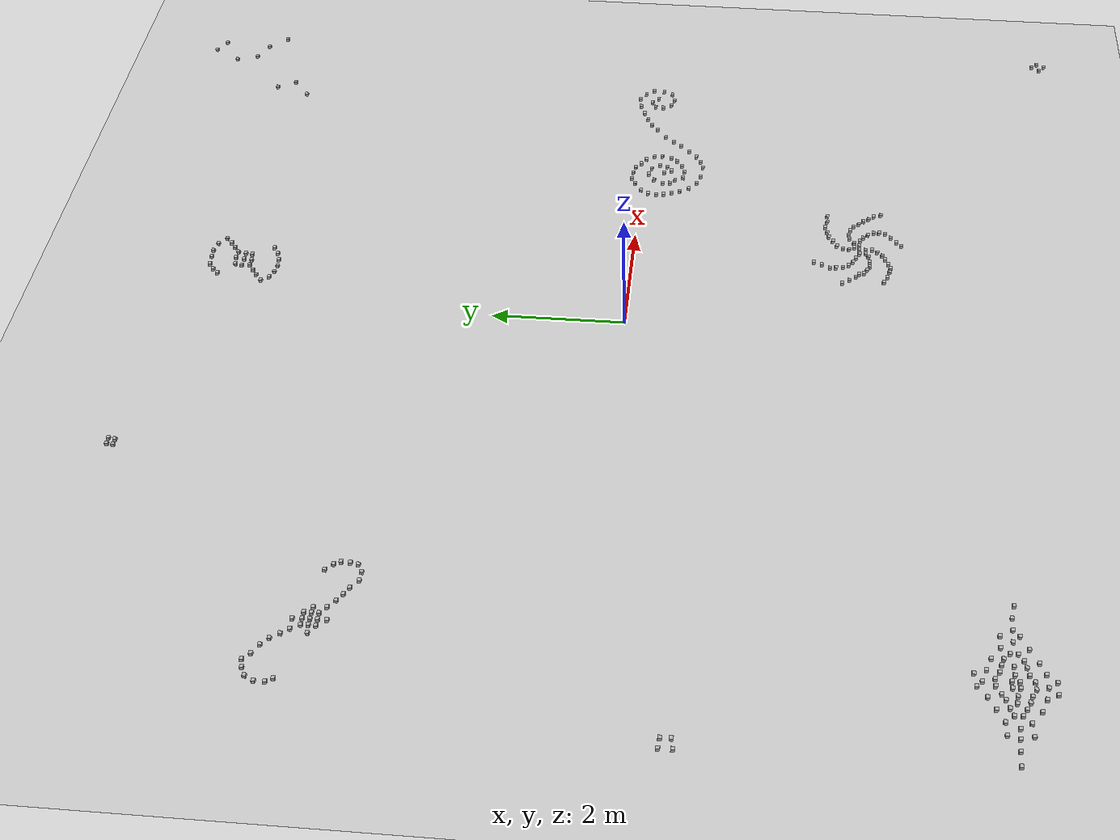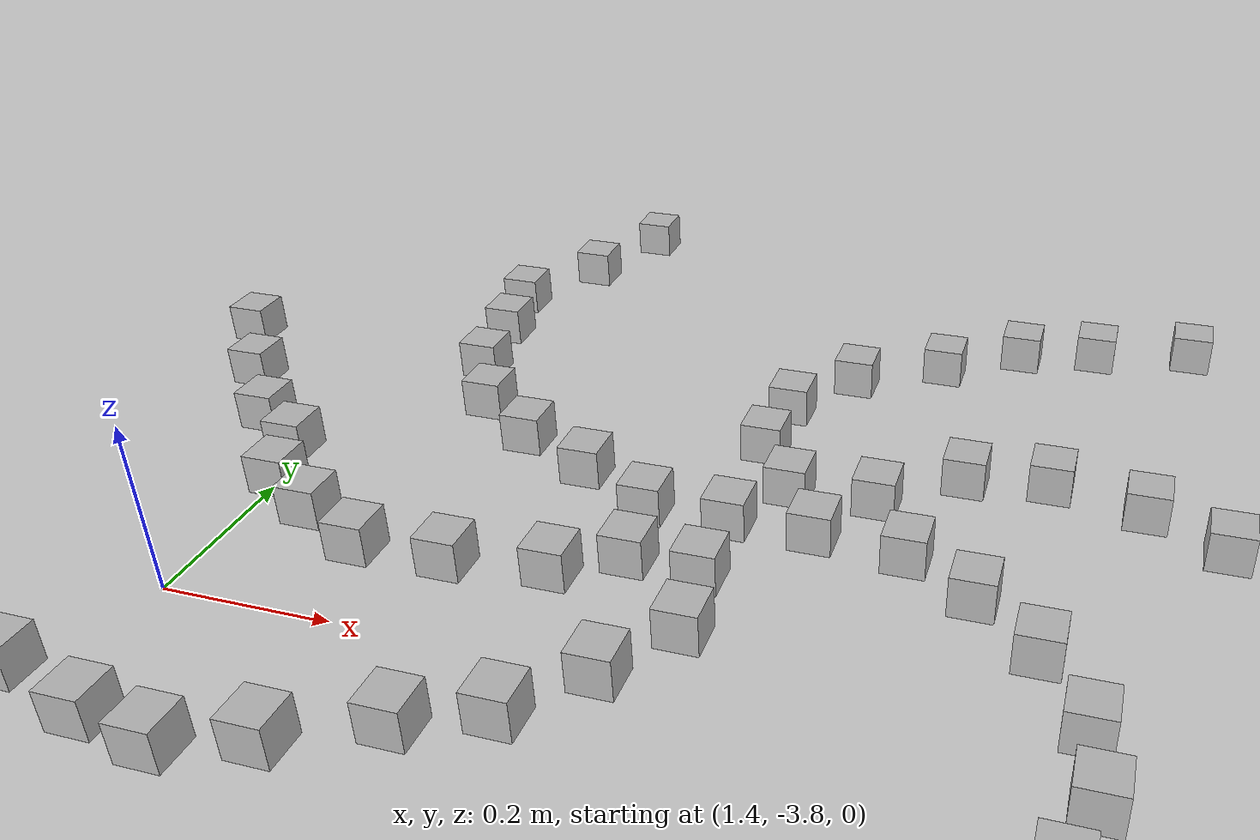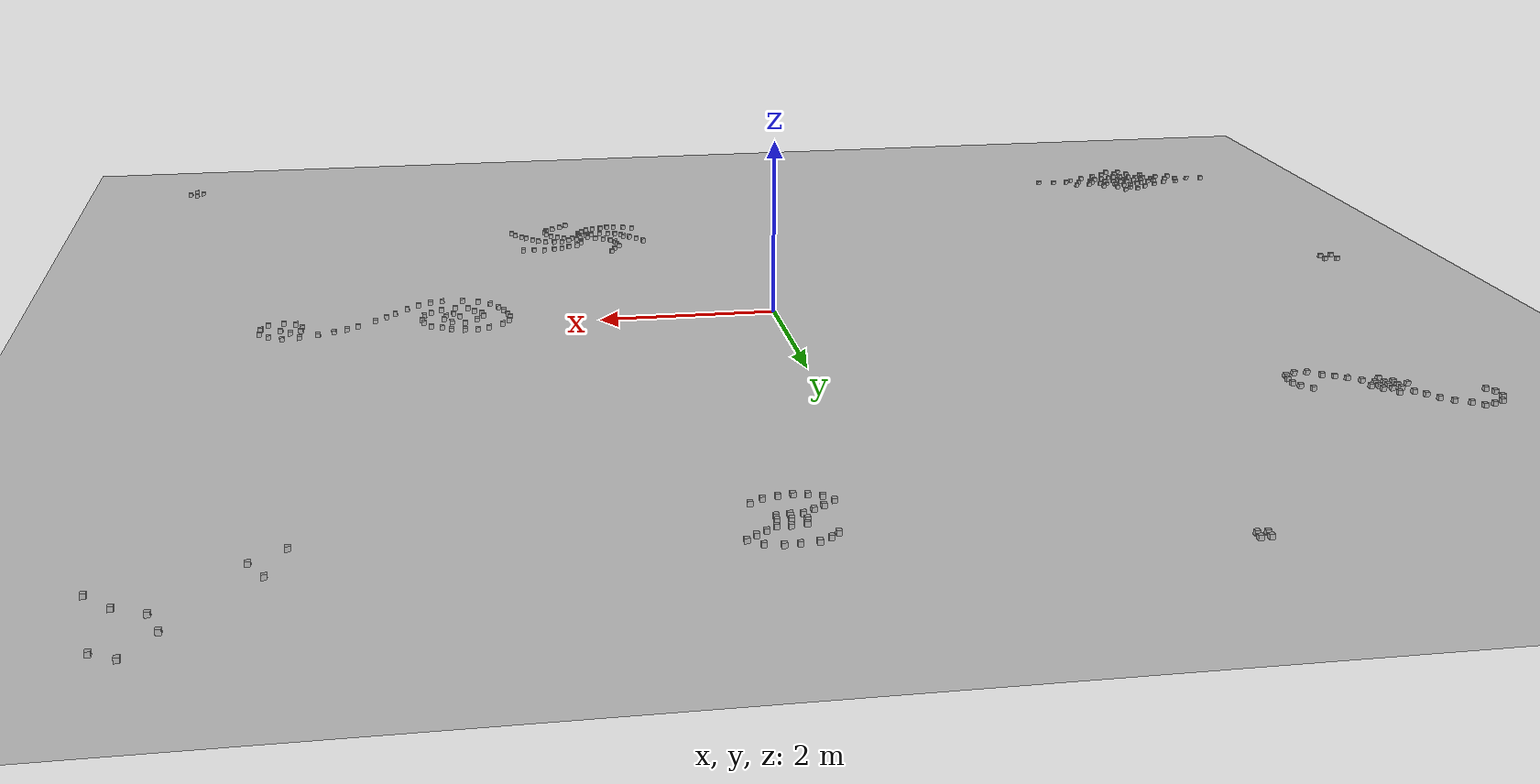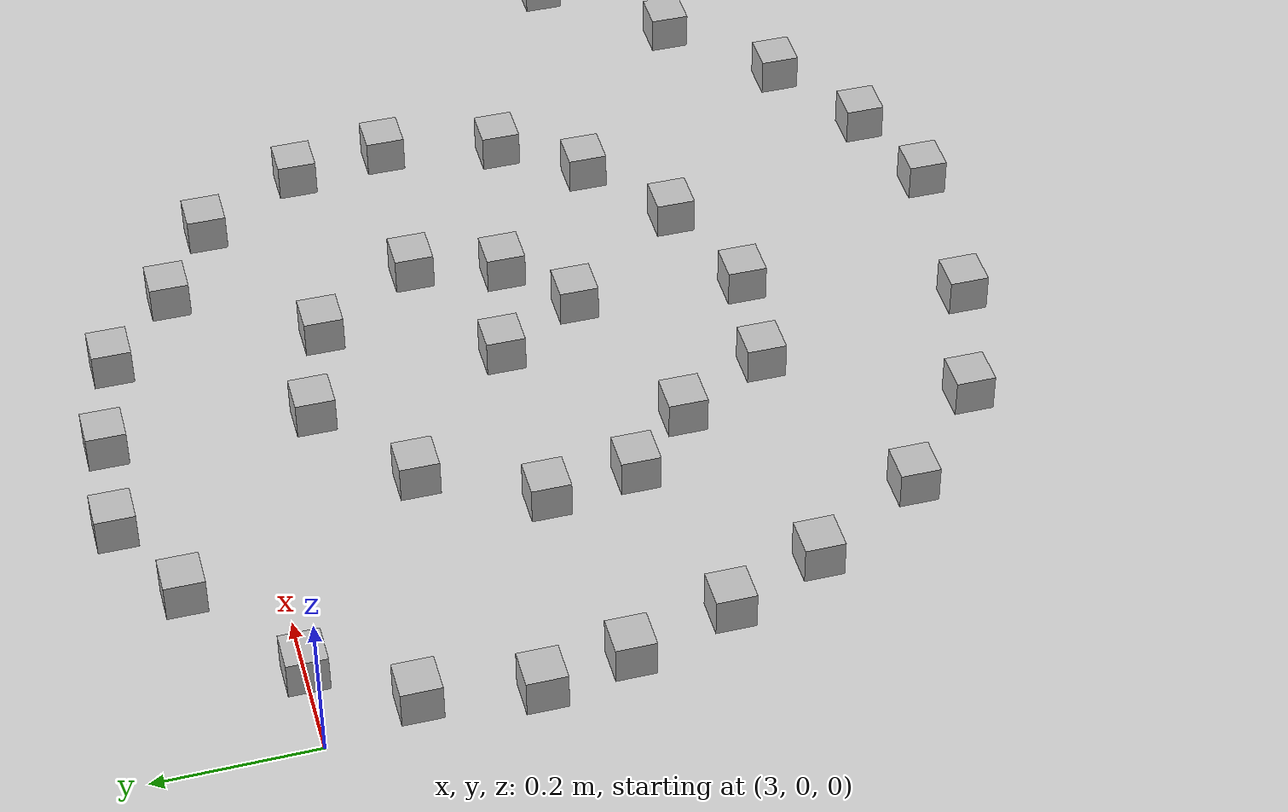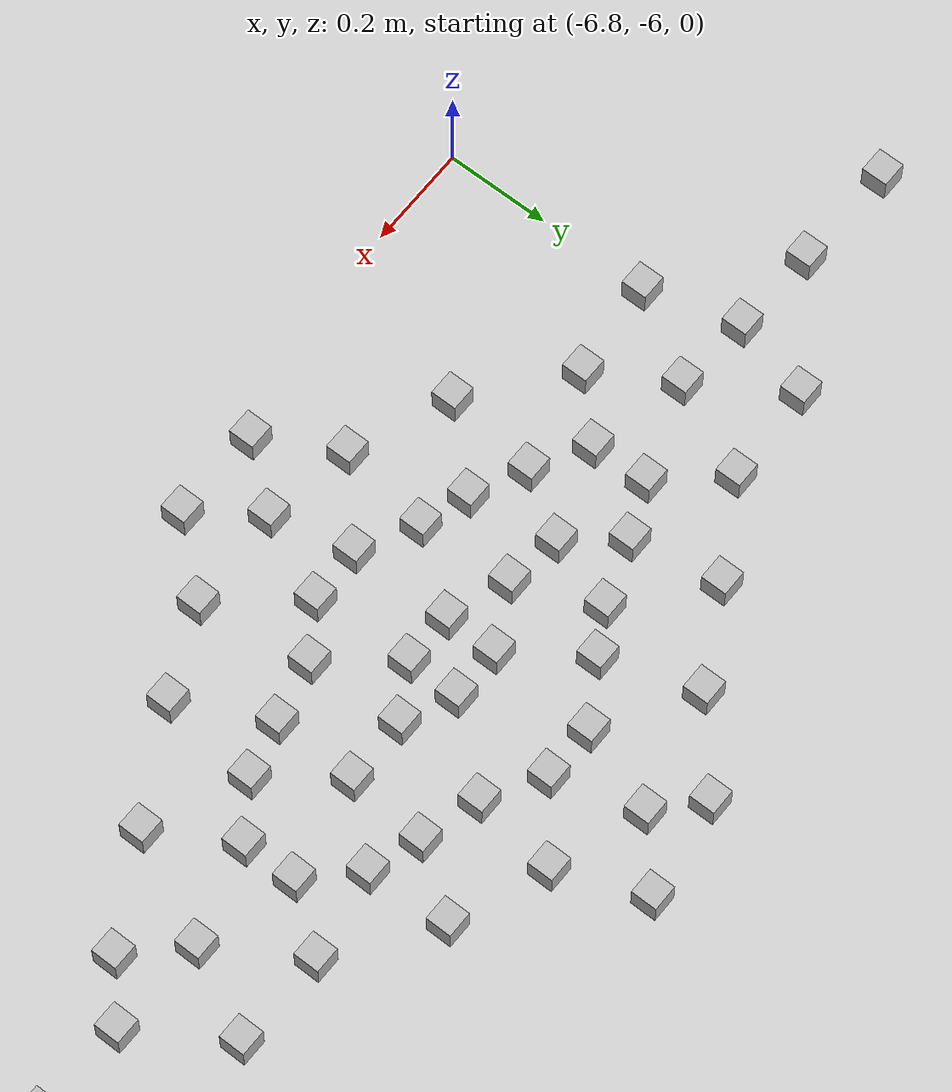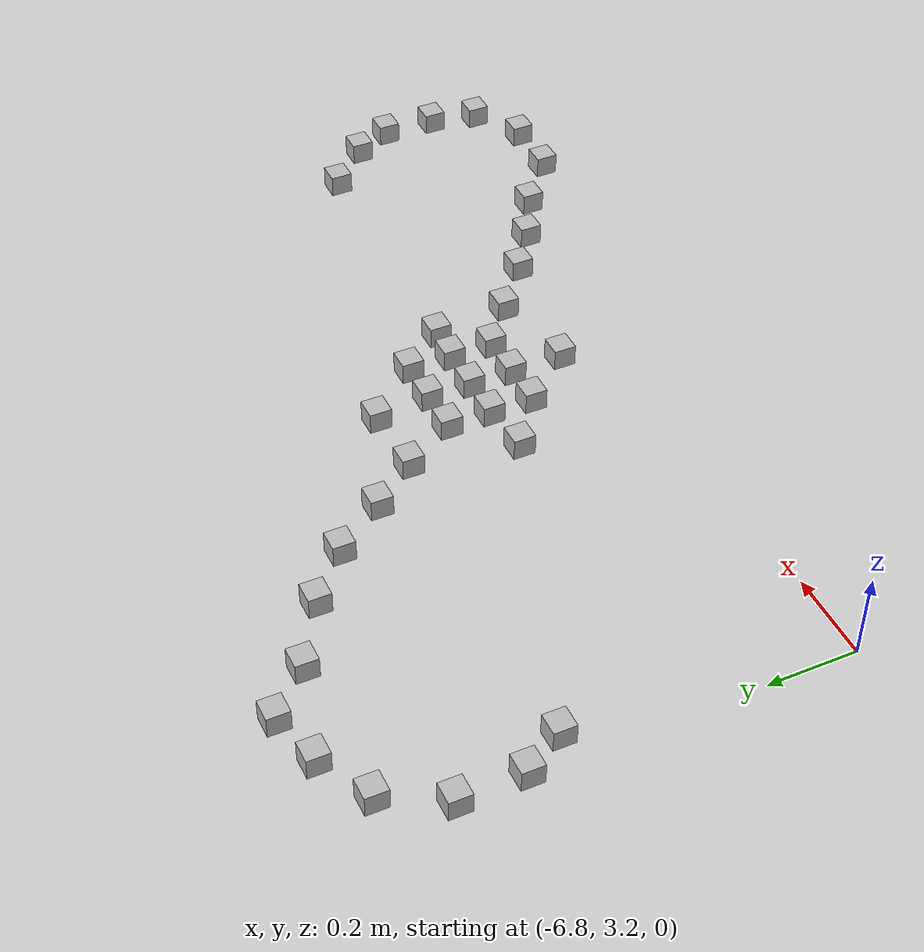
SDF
<sdf version="1.4">
 <world name="default">
  <model name="ground_plane">
   <static>1</static>
   <link name="link">
    <collision name="collision">
     <geometry><plane><normal>0 0 1</normal><size>100 100</size></plane></geometry>
     <surface><friction><ode><mu>100</mu><mu2>50</mu2></ode></friction></surface>
    </collision>
    <visual name="visual">
     <cast_shadows>0</cast_shadows>
     <geometry><plane><normal>0 0 1</normal><size>100 100</size></plane></geometry>
     <material>
      <script><uri>file://media/materials/scripts/gazebo.material</uri><name>Gazebo/Grey</name></script>
     </material>
    </visual>
    <velocity_decay><linear>0</linear><angular>0</angular></velocity_decay>
   </link>
  </model>
  <light name="sun" type="directional">
   <pose>0 0 10 0 -0 0</pose>
   <diffuse>0.8 0.8 0.8 1</diffuse>
   <specular>0.2 0.2 0.2 1</specular>
   <attenuation>
    <range>1000</range>
    <constant>0.9</constant>
    <linear>0.01</linear>
    <quadratic>0.001</quadratic>
   </attenuation>
   <direction>-0.5 0.1 -0.9</direction>
  </light>
  <plugin name="SetupWorld" filename="libgazebo_plugins.so"/>
  <physics type="ode">
   <max_step_size>0.001</max_step_size>
   <real_time_factor>1</real_time_factor>
   <real_time_update_rate>1000</real_time_update_rate>
   <gravity>0 0 -9.8</gravity>
  </physics>
  <scene><ambient>0.4 0.4 0.4 1</ambient><background>0.7 0.7 0.7 1</background><shadows>1</shadows></scene>
  <spherical_coordinates>
   <surface_model>EARTH_WGS84</surface_model>
   <latitude_deg>0</latitude_deg>
   <longitude_deg>0</longitude_deg>
   <elevation>0</elevation>
   <heading_deg>0</heading_deg>
  </spherical_coordinates>
  <model name="at0">
   <static>0</static>
   <link name="link">
    <inertial>
     <mass>0.01</mass>
     <inertia><ixx>4e-05</ixx><ixy>0</ixy><ixz>0</ixz><iyy>4e-05</iyy><iyz>0</iyz><izz>4e-05</izz></inertia>
    </inertial>
    <visual name="visual">
     <geometry><box><size>0.05 0.05 0.05</size></box></geometry>
     <material>
      <script>
       <uri>model://at0/materials/scripts</uri>
       <uri>model://at0/materials/textures</uri>
       <name>at0/Diffuse</name>
      </script>
     </material>
    </visual>
    <collision name="collision">
     <geometry><box><size>0.05 0.05 0.05</size></box></geometry>
     <surface><friction><ode><mu>0.8</mu><mu2>0.7</mu2></ode></friction></surface>
    </collision>
    <velocity_decay><linear>0</linear><angular>0</angular></velocity_decay>
   </link>
   <pose>-6.02182 3.53657 0.025 0 -0 0</pose>
  </model>
  <model name="at1">
   <static>0</static>
   <link name="link">
    <inertial>
     <mass>0.01</mass>
     <inertia><ixx>4e-05</ixx><ixy>0</ixy><ixz>0</ixz><iyy>4e-05</iyy><iyz>0</iyz><izz>4e-05</izz></inertia>
    </inertial>
    <visual name="visual">
     <geometry><box><size>0.05 0.05 0.05</size></box></geometry>
     <material>
      <script>
       <uri>model://at0/materials/scripts</uri>
       <uri>model://at0/materials/textures</uri>
       <name>at0/Diffuse</name>
      </script>
     </material>
    </visual>
    <collision name="collision">
     <geometry><box><size>0.05 0.05 0.05</size></box></geometry>
     <surface><friction><ode><mu>0.8</mu><mu2>0.7</mu2></ode></friction></surface>
    </collision>
    <velocity_decay><linear>0</linear><angular>0</angular></velocity_decay>
   </link>
   <pose>7.04443 -6.57904 0.025 0 -0 0</pose>
  </model>
  <model name="at2">
   <static>0</static>
   <link name="link">
    <inertial>
     <mass>0.01</mass>
     <inertia><ixx>4e-05</ixx><ixy>0</ixy><ixz>0</ixz><iyy>4e-05</iyy><iyz>0</iyz><izz>4e-05</izz></inertia>
    </inertial>
    <visual name="visual">
     <geometry><box><size>0.05 0.05 0.05</size></box></geometry>
     <material>
      <script>
       <uri>model://at0/materials/scripts</uri>
       <uri>model://at0/materials/textures</uri>
       <name>at0/Diffuse</name>
      </script>
     </material>
    </visual>
    <collision name="collision">
     <geometry><box><size>0.05 0.05 0.05</size></box></geometry>
     <surface><friction><ode><mu>0.8</mu><mu2>0.7</mu2></ode></friction></surface>
    </collision>
    <velocity_decay><linear>0</linear><angular>0</angular></velocity_decay>
   </link>
   <pose>-2.96769 6.94265 0.025 0 -0 0</pose>
  </model>
  <model name="at3">
   <static>0</static>
   <link name="link">
    <inertial>
     <mass>0.01</mass>
     <inertia><ixx>4e-05</ixx><ixy>0</ixy><ixz>0</ixz><iyy>4e-05</iyy><iyz>0</iyz><izz>4e-05</izz></inertia>
    </inertial>
    <visual name="visual">
     <geometry><box><size>0.05 0.05 0.05</size></box></geometry>
     <material>
      <script>
       <uri>model://at0/materials/scripts</uri>
       <uri>model://at0/materials/textures</uri>
       <name>at0/Diffuse</name>
      </script>
     </material>
    </visual>
    <collision name="collision">
     <geometry><box><size>0.05 0.05 0.05</size></box></geometry>
     <surface><friction><ode><mu>0.8</mu><mu2>0.7</mu2></ode></friction></surface>
    </collision>
    <velocity_decay><linear>0</linear><angular>0</angular></velocity_decay>
   </link>
   <pose>-6.80418 -5.25218 0.025 0 -0 0</pose>
  </model>
  <model name="at4">
   <static>0</static>
   <link name="link">
    <inertial>
     <mass>0.01</mass>
     <inertia><ixx>4e-05</ixx><ixy>0</ixy><ixz>0</ixz><iyy>4e-05</iyy><iyz>0</iyz><izz>4e-05</izz></inertia>
    </inertial>
    <visual name="visual">
     <geometry><box><size>0.05 0.05 0.05</size></box></geometry>
     <material>
      <script>
       <uri>model://at0/materials/scripts</uri>
       <uri>model://at0/materials/textures</uri>
       <name>at0/Diffuse</name>
      </script>
     </material>
    </visual>
    <collision name="collision">
     <geometry><box><size>0.05 0.05 0.05</size></box></geometry>
     <surface><friction><ode><mu>0.8</mu><mu2>0.7</mu2></ode></friction></surface>
    </collision>
    <velocity_decay><linear>0</linear><angular>0</angular></velocity_decay>
   </link>
   <pose>-3.06657 6.94342 0.025 0 -0 0</pose>
  </model>
  <model name="at5">
   <static>0</static>
   <link name="link">
    <inertial>
     <mass>0.01</mass>
     <inertia><ixx>4e-05</ixx><ixy>0</ixy><ixz>0</ixz><iyy>4e-05</iyy><iyz>0</iyz><izz>4e-05</izz></inertia>
    </inertial>
    <visual name="visual">
     <geometry><box><size>0.05 0.05 0.05</size></box></geometry>
     <material>
      <script>
       <uri>model://at0/materials/scripts</uri>
       <uri>model://at0/materials/textures</uri>
       <name>at0/Diffuse</name>
      </script>
     </material>
    </visual>
    <collision name="collision">
     <geometry><box><size>0.05 0.05 0.05</size></box></geometry>
     <surface><friction><ode><mu>0.8</mu><mu2>0.7</mu2></ode></friction></surface>
    </collision>
    <velocity_decay><linear>0</linear><angular>0</angular></velocity_decay>
   </link>
   <pose>-6.79493 -5.58281 0.025 0 -0 0</pose>
  </model>
  <model name="at6">
   <static>0</static>
   <link name="link">
    <inertial>
     <mass>0.01</mass>
     <inertia><ixx>4e-05</ixx><ixy>0</ixy><ixz>0</ixz><iyy>4e-05</iyy><iyz>0</iyz><izz>4e-05</izz></inertia>
    </inertial>
    <visual name="visual">
     <geometry><box><size>0.05 0.05 0.05</size></box></geometry>
     <material>
      <script>
       <uri>model://at0/materials/scripts</uri>
       <uri>model://at0/materials/textures</uri>
       <name>at0/Diffuse</name>
      </script>
     </material>
    </visual>
    <collision name="collision">
     <geometry><box><size>0.05 0.05 0.05</size></box></geometry>
     <surface><friction><ode><mu>0.8</mu><mu2>0.7</mu2></ode></friction></surface>
    </collision>
    <velocity_decay><linear>0</linear><angular>0</angular></velocity_decay>
   </link>
   <pose>-3.05734 7.03743 0.025 0 -0 0</pose>
  </model>
  <model name="at7">
   <static>0</static>
   <link name="link">
    <inertial>
     <mass>0.01</mass>
     <inertia><ixx>4e-05</ixx><ixy>0</ixy><ixz>0</ixz><iyy>4e-05</iyy><iyz>0</iyz><izz>4e-05</izz></inertia>
    </inertial>
    <visual name="visual">
     <geometry><box><size>0.05 0.05 0.05</size></box></geometry>
     <material>
      <script>
       <uri>model://at0/materials/scripts</uri>
       <uri>model://at0/materials/textures</uri>
       <name>at0/Diffuse</name>
      </script>
     </material>
    </visual>
    <collision name="collision">
     <geometry><box><size>0.05 0.05 0.05</size></box></geometry>
     <surface><friction><ode><mu>0.8</mu><mu2>0.7</mu2></ode></friction></surface>
    </collision>
    <velocity_decay><linear>0</linear><angular>0</angular></velocity_decay>
   </link>
   <pose>-5.92848 -4.89245 0.025 0 -0 0</pose>
  </model>
  <model name="at8">
   <static>0</static>
   <link name="link">
    <inertial>
     <mass>0.01</mass>
     <inertia><ixx>4e-05</ixx><ixy>0</ixy><ixz>0</ixz><iyy>4e-05</iyy><iyz>0</iyz><izz>4e-05</izz></inertia>
    </inertial>
    <visual name="visual">
     <geometry><box><size>0.05 0.05 0.05</size></box></geometry>
     <material>
      <script>
       <uri>model://at0/materials/scripts</uri>
       <uri>model://at0/materials/textures</uri>
       <name>at0/Diffuse</name>
      </script>
     </material>
    </visual>
    <collision name="collision">
     <geometry><box><size>0.05 0.05 0.05</size></box></geometry>
     <surface><friction><ode><mu>0.8</mu><mu2>0.7</mu2></ode></friction></surface>
    </collision>
    <velocity_decay><linear>0</linear><angular>0</angular></velocity_decay>
   </link>
   <pose>-5.62024 3.54547 0.025 0 -0 0</pose>
  </model>
  <model name="at9">
   <static>0</static>
   <link name="link">
    <inertial>
     <mass>0.01</mass>
     <inertia><ixx>4e-05</ixx><ixy>0</ixy><ixz>0</ixz><iyy>4e-05</iyy><iyz>0</iyz><izz>4e-05</izz></inertia>
    </inertial>
    <visual name="visual">
     <geometry><box><size>0.05 0.05 0.05</size></box></geometry>
     <material>
      <script>
       <uri>model://at0/materials/scripts</uri>
       <uri>model://at0/materials/textures</uri>
       <name>at0/Diffuse</name>
      </script>
     </material>
    </visual>
    <collision name="collision">
     <geometry><box><size>0.05 0.05 0.05</size></box></geometry>
     <surface><friction><ode><mu>0.8</mu><mu2>0.7</mu2></ode></friction></surface>
    </collision>
    <velocity_decay><linear>0</linear><angular>0</angular></velocity_decay>
   </link>
   <pose>-7.33876 -1.21655 0.025 0 -0 0</pose>
  </model>
  <model name="at10">
   <static>0</static>
   <link name="link">
    <inertial>
     <mass>0.01</mass>
     <inertia><ixx>4e-05</ixx><ixy>0</ixy><ixz>0</ixz><iyy>4e-05</iyy><iyz>0</iyz><izz>4e-05</izz></inertia>
    </inertial>
    <visual name="visual">
     <geometry><box><size>0.05 0.05 0.05</size></box></geometry>
     <material>
      <script>
       <uri>model://at0/materials/scripts</uri>
       <uri>model://at0/materials/textures</uri>
       <name>at0/Diffuse</name>
      </script>
     </material>
    </visual>
    <collision name="collision">
     <geometry><box><size>0.05 0.05 0.05</size></box></geometry>
     <surface><friction><ode><mu>0.8</mu><mu2>0.7</mu2></ode></friction></surface>
    </collision>
    <velocity_decay><linear>0</linear><angular>0</angular></velocity_decay>
   </link>
   <pose>-7.19254 -1.04912 0.025 0 -0 0</pose>
  </model>
  <model name="at11">
   <static>0</static>
   <link name="link">
    <inertial>
     <mass>0.01</mass>
     <inertia><ixx>4e-05</ixx><ixy>0</ixy><ixz>0</ixz><iyy>4e-05</iyy><iyz>0</iyz><izz>4e-05</izz></inertia>
    </inertial>
    <visual name="visual">
     <geometry><box><size>0.05 0.05 0.05</size></box></geometry>
     <material>
      <script>
       <uri>model://at0/materials/scripts</uri>
       <uri>model://at0/materials/textures</uri>
       <name>at0/Diffuse</name>
      </script>
     </material>
    </visual>
    <collision name="collision">
     <geometry><box><size>0.05 0.05 0.05</size></box></geometry>
     <surface><friction><ode><mu>0.8</mu><mu2>0.7</mu2></ode></friction></surface>
    </collision>
    <velocity_decay><linear>0</linear><angular>0</angular></velocity_decay>
   </link>
   <pose>4.53442 -0.307039 0.025 0 -0 0</pose>
  </model>
  <model name="at12">
   <static>0</static>
   <link name="link">
    <inertial>
     <mass>0.01</mass>
     <inertia><ixx>4e-05</ixx><ixy>0</ixy><ixz>0</ixz><iyy>4e-05</iyy><iyz>0</iyz><izz>4e-05</izz></inertia>
    </inertial>
    <visual name="visual">
     <geometry><box><size>0.05 0.05 0.05</size></box></geometry>
     <material>
      <script>
       <uri>model://at0/materials/scripts</uri>
       <uri>model://at0/materials/textures</uri>
       <name>at0/Diffuse</name>
      </script>
     </material>
    </visual>
    <collision name="collision">
     <geometry><box><size>0.05 0.05 0.05</size></box></geometry>
     <surface><friction><ode><mu>0.8</mu><mu2>0.7</mu2></ode></friction></surface>
    </collision>
    <velocity_decay><linear>0</linear><angular>0</angular></velocity_decay>
   </link>
   <pose>6.97231 -6.70275 0.025 0 -0 0</pose>
  </model>
  <model name="at13">
   <static>0</static>
   <link name="link">
    <inertial>
     <mass>0.01</mass>
     <inertia><ixx>4e-05</ixx><ixy>0</ixy><ixz>0</ixz><iyy>4e-05</iyy><iyz>0</iyz><izz>4e-05</izz></inertia>
    </inertial>
    <visual name="visual">
     <geometry><box><size>0.05 0.05 0.05</size></box></geometry>
     <material>
      <script>
       <uri>model://at0/materials/scripts</uri>
       <uri>model://at0/materials/textures</uri>
       <name>at0/Diffuse</name>
      </script>
     </material>
    </visual>
    <collision name="collision">
     <geometry><box><size>0.05 0.05 0.05</size></box></geometry>
     <surface><friction><ode><mu>0.8</mu><mu2>0.7</mu2></ode></friction></surface>
    </collision>
    <velocity_decay><linear>0</linear><angular>0</angular></velocity_decay>
   </link>
   <pose>4.72294 -0.152985 0.025 0 -0 0</pose>
  </model>
  <model name="at14">
   <static>0</static>
   <link name="link">
    <inertial>
     <mass>0.01</mass>
     <inertia><ixx>4e-05</ixx><ixy>0</ixy><ixz>0</ixz><iyy>4e-05</iyy><iyz>0</iyz><izz>4e-05</izz></inertia>
    </inertial>
    <visual name="visual">
     <geometry><box><size>0.05 0.05 0.05</size></box></geometry>
     <material>
      <script>
       <uri>model://at0/materials/scripts</uri>
       <uri>model://at0/materials/textures</uri>
       <name>at0/Diffuse</name>
      </script>
     </material>
    </visual>
    <collision name="collision">
     <geometry><box><size>0.05 0.05 0.05</size></box></geometry>
     <surface><friction><ode><mu>0.8</mu><mu2>0.7</mu2></ode></friction></surface>
    </collision>
    <velocity_decay><linear>0</linear><angular>0</angular></velocity_decay>
   </link>
   <pose>4.84507 -0.044757 0.025 0 -0 0</pose>
  </model>
  <model name="at15">
   <static>0</static>
   <link name="link">
    <inertial>
     <mass>0.01</mass>
     <inertia><ixx>4e-05</ixx><ixy>0</ixy><ixz>0</ixz><iyy>4e-05</iyy><iyz>0</iyz><izz>4e-05</izz></inertia>
    </inertial>
    <visual name="visual">
     <geometry><box><size>0.05 0.05 0.05</size></box></geometry>
     <material>
      <script>
       <uri>model://at0/materials/scripts</uri>
       <uri>model://at0/materials/textures</uri>
       <name>at0/Diffuse</name>
      </script>
     </material>
    </visual>
    <collision name="collision">
     <geometry><box><size>0.05 0.05 0.05</size></box></geometry>
     <surface><friction><ode><mu>0.8</mu><mu2>0.7</mu2></ode></friction></surface>
    </collision>
    <velocity_decay><linear>0</linear><angular>0</angular></velocity_decay>
   </link>
   <pose>-5.98274 -5.92643 0.025 0 -0 0</pose>
  </model>
  <model name="at16">
   <static>0</static>
   <link name="link">
    <inertial>
     <mass>0.01</mass>
     <inertia><ixx>4e-05</ixx><ixy>0</ixy><ixz>0</ixz><iyy>4e-05</iyy><iyz>0</iyz><izz>4e-05</izz></inertia>
    </inertial>
    <visual name="visual">
     <geometry><box><size>0.05 0.05 0.05</size></box></geometry>
     <material>
      <script>
       <uri>model://at0/materials/scripts</uri>
       <uri>model://at0/materials/textures</uri>
       <name>at0/Diffuse</name>
      </script>
     </material>
    </visual>
    <collision name="collision">
     <geometry><box><size>0.05 0.05 0.05</size></box></geometry>
     <surface><friction><ode><mu>0.8</mu><mu2>0.7</mu2></ode></friction></surface>
    </collision>
    <velocity_decay><linear>0</linear><angular>0</angular></velocity_decay>
   </link>
   <pose>-5.82072 3.77826 0.025 0 -0 0</pose>
  </model>
  <model name="at17">
   <static>0</static>
   <link name="link">
    <inertial>
     <mass>0.01</mass>
     <inertia><ixx>4e-05</ixx><ixy>0</ixy><ixz>0</ixz><iyy>4e-05</iyy><iyz>0</iyz><izz>4e-05</izz></inertia>
    </inertial>
    <visual name="visual">
     <geometry><box><size>0.05 0.05 0.05</size></box></geometry>
     <material>
      <script>
       <uri>model://at0/materials/scripts</uri>
       <uri>model://at0/materials/textures</uri>
       <name>at0/Diffuse</name>
      </script>
     </material>
    </visual>
    <collision name="collision">
     <geometry><box><size>0.05 0.05 0.05</size></box></geometry>
     <surface><friction><ode><mu>0.8</mu><mu2>0.7</mu2></ode></friction></surface>
    </collision>
    <velocity_decay><linear>0</linear><angular>0</angular></velocity_decay>
   </link>
   <pose>-7.18944 -1.19222 0.025 0 -0 0</pose>
  </model>
  <model name="at18">
   <static>0</static>
   <link name="link">
    <inertial>
     <mass>0.01</mass>
     <inertia><ixx>4e-05</ixx><ixy>0</ixy><ixz>0</ixz><iyy>4e-05</iyy><iyz>0</iyz><izz>4e-05</izz></inertia>
    </inertial>
    <visual name="visual">
     <geometry><box><size>0.05 0.05 0.05</size></box></geometry>
     <material>
      <script>
       <uri>model://at0/materials/scripts</uri>
       <uri>model://at0/materials/textures</uri>
       <name>at0/Diffuse</name>
      </script>
     </material>
    </visual>
    <collision name="collision">
     <geometry><box><size>0.05 0.05 0.05</size></box></geometry>
     <surface><friction><ode><mu>0.8</mu><mu2>0.7</mu2></ode></friction></surface>
    </collision>
    <velocity_decay><linear>0</linear><angular>0</angular></velocity_decay>
   </link>
   <pose>-7.34398 -1.03764 0.025 0 -0 0</pose>
  </model>
  <model name="at19">
   <static>0</static>
   <link name="link">
    <inertial>
     <mass>0.01</mass>
     <inertia><ixx>4e-05</ixx><ixy>0</ixy><ixz>0</ixz><iyy>4e-05</iyy><iyz>0</iyz><izz>4e-05</izz></inertia>
    </inertial>
    <visual name="visual">
     <geometry><box><size>0.05 0.05 0.05</size></box></geometry>
     <material>
      <script>
       <uri>model://at0/materials/scripts</uri>
       <uri>model://at0/materials/textures</uri>
       <name>at0/Diffuse</name>
      </script>
     </material>
    </visual>
    <collision name="collision">
     <geometry><box><size>0.05 0.05 0.05</size></box></geometry>
     <surface><friction><ode><mu>0.8</mu><mu2>0.7</mu2></ode></friction></surface>
    </collision>
    <velocity_decay><linear>0</linear><angular>0</angular></velocity_decay>
   </link>
   <pose>7.0648 -6.78613 0.025 0 -0 0</pose>
  </model>
  <model name="at20">
   <static>0</static>
   <link name="link">
    <inertial>
     <mass>0.01</mass>
     <inertia><ixx>4e-05</ixx><ixy>0</ixy><ixz>0</ixz><iyy>4e-05</iyy><iyz>0</iyz><izz>4e-05</izz></inertia>
    </inertial>
    <visual name="visual">
     <geometry><box><size>0.05 0.05 0.05</size></box></geometry>
     <material>
      <script>
       <uri>model://at0/materials/scripts</uri>
       <uri>model://at0/materials/textures</uri>
       <name>at0/Diffuse</name>
      </script>
     </material>
    </visual>
    <collision name="collision">
     <geometry><box><size>0.05 0.05 0.05</size></box></geometry>
     <surface><friction><ode><mu>0.8</mu><mu2>0.7</mu2></ode></friction></surface>
    </collision>
    <velocity_decay><linear>0</linear><angular>0</angular></velocity_decay>
   </link>
   <pose>-5.3259 -5.2549 0.025 0 -0 0</pose>
  </model>
  <model name="at21">
   <static>0</static>
   <link name="link">
    <inertial>
     <mass>0.01</mass>
     <inertia><ixx>4e-05</ixx><ixy>0</ixy><ixz>0</ixz><iyy>4e-05</iyy><iyz>0</iyz><izz>4e-05</izz></inertia>
    </inertial>
    <visual name="visual">
     <geometry><box><size>0.05 0.05 0.05</size></box></geometry>
     <material>
      <script>
       <uri>model://at0/materials/scripts</uri>
       <uri>model://at0/materials/textures</uri>
       <name>at0/Diffuse</name>
      </script>
     </material>
    </visual>
    <collision name="collision">
     <geometry><box><size>0.05 0.05 0.05</size></box></geometry>
     <surface><friction><ode><mu>0.8</mu><mu2>0.7</mu2></ode></friction></surface>
    </collision>
    <velocity_decay><linear>0</linear><angular>0</angular></velocity_decay>
   </link>
   <pose>-6.11866 -4.92044 0.025 0 -0 0</pose>
  </model>
  <model name="at22">
   <static>0</static>
   <link name="link">
    <inertial>
     <mass>0.01</mass>
     <inertia><ixx>4e-05</ixx><ixy>0</ixy><ixz>0</ixz><iyy>4e-05</iyy><iyz>0</iyz><izz>4e-05</izz></inertia>
    </inertial>
    <visual name="visual">
     <geometry><box><size>0.05 0.05 0.05</size></box></geometry>
     <material>
      <script>
       <uri>model://at0/materials/scripts</uri>
       <uri>model://at0/materials/textures</uri>
       <name>at0/Diffuse</name>
      </script>
     </material>
    </visual>
    <collision name="collision">
     <geometry><box><size>0.05 0.05 0.05</size></box></geometry>
     <surface><friction><ode><mu>0.8</mu><mu2>0.7</mu2></ode></friction></surface>
    </collision>
    <velocity_decay><linear>0</linear><angular>0</angular></velocity_decay>
   </link>
   <pose>-5.31034 -5.50775 0.025 0 -0 0</pose>
  </model>
  <model name="at23">
   <static>0</static>
   <link name="link">
    <inertial>
     <mass>0.01</mass>
     <inertia><ixx>4e-05</ixx><ixy>0</ixy><ixz>0</ixz><iyy>4e-05</iyy><iyz>0</iyz><izz>4e-05</izz></inertia>
    </inertial>
    <visual name="visual">
     <geometry><box><size>0.05 0.05 0.05</size></box></geometry>
     <material>
      <script>
       <uri>model://at0/materials/scripts</uri>
       <uri>model://at0/materials/textures</uri>
       <name>at0/Diffuse</name>
      </script>
     </material>
    </visual>
    <collision name="collision">
     <geometry><box><size>0.05 0.05 0.05</size></box></geometry>
     <surface><friction><ode><mu>0.8</mu><mu2>0.7</mu2></ode></friction></surface>
    </collision>
    <velocity_decay><linear>0</linear><angular>0</angular></velocity_decay>
   </link>
   <pose>-4.83066 -5.46618 0.025 0 -0 0</pose>
  </model>
  <model name="at24">
   <static>0</static>
   <link name="link">
    <inertial>
     <mass>0.01</mass>
     <inertia><ixx>4e-05</ixx><ixy>0</ixy><ixz>0</ixz><iyy>4e-05</iyy><iyz>0</iyz><izz>4e-05</izz></inertia>
    </inertial>
    <visual name="visual">
     <geometry><box><size>0.05 0.05 0.05</size></box></geometry>
     <material>
      <script>
       <uri>model://at0/materials/scripts</uri>
       <uri>model://at0/materials/textures</uri>
       <name>at0/Diffuse</name>
      </script>
     </material>
    </visual>
    <collision name="collision">
     <geometry><box><size>0.05 0.05 0.05</size></box></geometry>
     <surface><friction><ode><mu>0.8</mu><mu2>0.7</mu2></ode></friction></surface>
    </collision>
    <velocity_decay><linear>0</linear><angular>0</angular></velocity_decay>
   </link>
   <pose>-5.80271 3.32852 0.025 0 -0 0</pose>
  </model>
  <model name="at25">
   <static>0</static>
   <link name="link">
    <inertial>
     <mass>0.01</mass>
     <inertia><ixx>4e-05</ixx><ixy>0</ixy><ixz>0</ixz><iyy>4e-05</iyy><iyz>0</iyz><izz>4e-05</izz></inertia>
    </inertial>
    <visual name="visual">
     <geometry><box><size>0.05 0.05 0.05</size></box></geometry>
     <material>
      <script>
       <uri>model://at0/materials/scripts</uri>
       <uri>model://at0/materials/textures</uri>
       <name>at0/Diffuse</name>
      </script>
     </material>
    </visual>
    <collision name="collision">
     <geometry><box><size>0.05 0.05 0.05</size></box></geometry>
     <surface><friction><ode><mu>0.8</mu><mu2>0.7</mu2></ode></friction></surface>
    </collision>
    <velocity_decay><linear>0</linear><angular>0</angular></velocity_decay>
   </link>
   <pose>0.795828 6.14263 0.025 0 -0 0</pose>
  </model>
  <model name="at26">
   <static>0</static>
   <link name="link">
    <inertial>
     <mass>0.01</mass>
     <inertia><ixx>4e-05</ixx><ixy>0</ixy><ixz>0</ixz><iyy>4e-05</iyy><iyz>0</iyz><izz>4e-05</izz></inertia>
    </inertial>
    <visual name="visual">
     <geometry><box><size>0.05 0.05 0.05</size></box></geometry>
     <material>
      <script>
       <uri>model://at0/materials/scripts</uri>
       <uri>model://at0/materials/textures</uri>
       <name>at0/Diffuse</name>
      </script>
     </material>
    </visual>
    <collision name="collision">
     <geometry><box><size>0.05 0.05 0.05</size></box></geometry>
     <surface><friction><ode><mu>0.8</mu><mu2>0.7</mu2></ode></friction></surface>
    </collision>
    <velocity_decay><linear>0</linear><angular>0</angular></velocity_decay>
   </link>
   <pose>-2.95567 7.04077 0.025 0 -0 0</pose>
  </model>
  <model name="at27">
   <static>0</static>
   <link name="link">
    <inertial>
     <mass>0.01</mass>
     <inertia><ixx>4e-05</ixx><ixy>0</ixy><ixz>0</ixz><iyy>4e-05</iyy><iyz>0</iyz><izz>4e-05</izz></inertia>
    </inertial>
    <visual name="visual">
     <geometry><box><size>0.05 0.05 0.05</size></box></geometry>
     <material>
      <script>
       <uri>model://at0/materials/scripts</uri>
       <uri>model://at0/materials/textures</uri>
       <name>at0/Diffuse</name>
      </script>
     </material>
    </visual>
    <collision name="collision">
     <geometry><box><size>0.05 0.05 0.05</size></box></geometry>
     <surface><friction><ode><mu>0.8</mu><mu2>0.7</mu2></ode></friction></surface>
    </collision>
    <velocity_decay><linear>0</linear><angular>0</angular></velocity_decay>
   </link>
   <pose>4.40493 -0.446845 0.025 0 -0 0</pose>
  </model>
  <model name="at28">
   <static>0</static>
   <link name="link">
    <inertial>
     <mass>0.01</mass>
     <inertia><ixx>4e-05</ixx><ixy>0</ixy><ixz>0</ixz><iyy>4e-05</iyy><iyz>0</iyz><izz>4e-05</izz></inertia>
    </inertial>
    <visual name="visual">
     <geometry><box><size>0.05 0.05 0.05</size></box></geometry>
     <material>
      <script>
       <uri>model://at0/materials/scripts</uri>
       <uri>model://at0/materials/textures</uri>
       <name>at0/Diffuse</name>
      </script>
     </material>
    </visual>
    <collision name="collision">
     <geometry><box><size>0.05 0.05 0.05</size></box></geometry>
     <surface><friction><ode><mu>0.8</mu><mu2>0.7</mu2></ode></friction></surface>
    </collision>
    <velocity_decay><linear>0</linear><angular>0</angular></velocity_decay>
   </link>
   <pose>7.13963 -6.67128 0.025 0 -0 0</pose>
  </model>
  <model name="at29">
   <static>0</static>
   <link name="link">
    <inertial>
     <mass>0.01</mass>
     <inertia><ixx>4e-05</ixx><ixy>0</ixy><ixz>0</ixz><iyy>4e-05</iyy><iyz>0</iyz><izz>4e-05</izz></inertia>
    </inertial>
    <visual name="visual">
     <geometry><box><size>0.05 0.05 0.05</size></box></geometry>
     <material>
      <script>
       <uri>model://at0/materials/scripts</uri>
       <uri>model://at0/materials/textures</uri>
       <name>at0/Diffuse</name>
      </script>
     </material>
    </visual>
    <collision name="collision">
     <geometry><box><size>0.05 0.05 0.05</size></box></geometry>
     <surface><friction><ode><mu>0.8</mu><mu2>0.7</mu2></ode></friction></surface>
    </collision>
    <velocity_decay><linear>0</linear><angular>0</angular></velocity_decay>
   </link>
   <pose>-6.16116 -5.92584 0.025 0 -0 0</pose>
  </model>
  <model name="at30">
   <static>0</static>
   <link name="link">
    <inertial>
     <mass>0.01</mass>
     <inertia><ixx>4e-05</ixx><ixy>0</ixy><ixz>0</ixz><iyy>4e-05</iyy><iyz>0</iyz><izz>4e-05</izz></inertia>
    </inertial>
    <visual name="visual">
     <geometry><box><size>0.05 0.05 0.05</size></box></geometry>
     <material>
      <script>
       <uri>model://at0/materials/scripts</uri>
       <uri>model://at0/materials/textures</uri>
       <name>at0/Diffuse</name>
      </script>
     </material>
    </visual>
    <collision name="collision">
     <geometry><box><size>0.05 0.05 0.05</size></box></geometry>
     <surface><friction><ode><mu>0.8</mu><mu2>0.7</mu2></ode></friction></surface>
    </collision>
    <velocity_decay><linear>0</linear><angular>0</angular></velocity_decay>
   </link>
   <pose>1.03376 5.93127 0.025 0 -0 0</pose>
  </model>
  <model name="at31">
   <static>0</static>
   <link name="link">
    <inertial>
     <mass>0.01</mass>
     <inertia><ixx>4e-05</ixx><ixy>0</ixy><ixz>0</ixz><iyy>4e-05</iyy><iyz>0</iyz><izz>4e-05</izz></inertia>
    </inertial>
    <visual name="visual">
     <geometry><box><size>0.05 0.05 0.05</size></box></geometry>
     <material>
      <script>
       <uri>model://at0/materials/scripts</uri>
       <uri>model://at0/materials/textures</uri>
       <name>at0/Diffuse</name>
      </script>
     </material>
    </visual>
    <collision name="collision">
     <geometry><box><size>0.05 0.05 0.05</size></box></geometry>
     <surface><friction><ode><mu>0.8</mu><mu2>0.7</mu2></ode></friction></surface>
    </collision>
    <velocity_decay><linear>0</linear><angular>0</angular></velocity_decay>
   </link>
   <pose>-7.22552 -5.39313 0.025 0 -0 0</pose>
  </model>
  <model name="at32">
   <static>0</static>
   <link name="link">
    <inertial>
     <mass>0.01</mass>
     <inertia><ixx>4e-05</ixx><ixy>0</ixy><ixz>0</ixz><iyy>4e-05</iyy><iyz>0</iyz><izz>4e-05</izz></inertia>
    </inertial>
    <visual name="visual">
     <geometry><box><size>0.05 0.05 0.05</size></box></geometry>
     <material>
      <script>
       <uri>model://at0/materials/scripts</uri>
       <uri>model://at0/materials/textures</uri>
       <name>at0/Diffuse</name>
      </script>
     </material>
    </visual>
    <collision name="collision">
     <geometry><box><size>0.05 0.05 0.05</size></box></geometry>
     <surface><friction><ode><mu>0.8</mu><mu2>0.7</mu2></ode></friction></surface>
    </collision>
    <velocity_decay><linear>0</linear><angular>0</angular></velocity_decay>
   </link>
   <pose>-5.21728 -5.42339 0.025 0 -0 0</pose>
  </model>
  <model name="at33">
   <static>0</static>
   <link name="link">
    <inertial>
     <mass>0.01</mass>
     <inertia><ixx>4e-05</ixx><ixy>0</ixy><ixz>0</ixz><iyy>4e-05</iyy><iyz>0</iyz><izz>4e-05</izz></inertia>
    </inertial>
    <visual name="visual">
     <geometry><box><size>0.05 0.05 0.05</size></box></geometry>
     <material>
      <script>
       <uri>model://at0/materials/scripts</uri>
       <uri>model://at0/materials/textures</uri>
       <name>at0/Diffuse</name>
      </script>
     </material>
    </visual>
    <collision name="collision">
     <geometry><box><size>0.05 0.05 0.05</size></box></geometry>
     <surface><friction><ode><mu>0.8</mu><mu2>0.7</mu2></ode></friction></surface>
    </collision>
    <velocity_decay><linear>0</linear><angular>0</angular></velocity_decay>
   </link>
   <pose>2.80606 -3.87012 0.025 0 -0 0</pose>
  </model>
  <model name="at34">
   <static>0</static>
   <link name="link">
    <inertial>
     <mass>0.01</mass>
     <inertia><ixx>4e-05</ixx><ixy>0</ixy><ixz>0</ixz><iyy>4e-05</iyy><iyz>0</iyz><izz>4e-05</izz></inertia>
    </inertial>
    <visual name="visual">
     <geometry><box><size>0.05 0.05 0.05</size></box></geometry>
     <material>
      <script>
       <uri>model://at0/materials/scripts</uri>
       <uri>model://at0/materials/textures</uri>
       <name>at0/Diffuse</name>
      </script>
     </material>
    </visual>
    <collision name="collision">
     <geometry><box><size>0.05 0.05 0.05</size></box></geometry>
     <surface><friction><ode><mu>0.8</mu><mu2>0.7</mu2></ode></friction></surface>
    </collision>
    <velocity_decay><linear>0</linear><angular>0</angular></velocity_decay>
   </link>
   <pose>5.72105 -0.337039 0.025 0 -0 0</pose>
  </model>
  <model name="at35">
   <static>0</static>
   <link name="link">
    <inertial>
     <mass>0.01</mass>
     <inertia><ixx>4e-05</ixx><ixy>0</ixy><ixz>0</ixz><iyy>4e-05</iyy><iyz>0</iyz><izz>4e-05</izz></inertia>
    </inertial>
    <visual name="visual">
     <geometry><box><size>0.05 0.05 0.05</size></box></geometry>
     <material>
      <script>
       <uri>model://at0/materials/scripts</uri>
       <uri>model://at0/materials/textures</uri>
       <name>at0/Diffuse</name>
      </script>
     </material>
    </visual>
    <collision name="collision">
     <geometry><box><size>0.05 0.05 0.05</size></box></geometry>
     <surface><friction><ode><mu>0.8</mu><mu2>0.7</mu2></ode></friction></surface>
    </collision>
    <velocity_decay><linear>0</linear><angular>0</angular></velocity_decay>
   </link>
   <pose>2.7031 -3.01801 0.025 0 -0 0</pose>
  </model>
  <model name="at36">
   <static>0</static>
   <link name="link">
    <inertial>
     <mass>0.01</mass>
     <inertia><ixx>4e-05</ixx><ixy>0</ixy><ixz>0</ixz><iyy>4e-05</iyy><iyz>0</iyz><izz>4e-05</izz></inertia>
    </inertial>
    <visual name="visual">
     <geometry><box><size>0.05 0.05 0.05</size></box></geometry>
     <material>
      <script>
       <uri>model://at0/materials/scripts</uri>
       <uri>model://at0/materials/textures</uri>
       <name>at0/Diffuse</name>
      </script>
     </material>
    </visual>
    <collision name="collision">
     <geometry><box><size>0.05 0.05 0.05</size></box></geometry>
     <surface><friction><ode><mu>0.8</mu><mu2>0.7</mu2></ode></friction></surface>
    </collision>
    <velocity_decay><linear>0</linear><angular>0</angular></velocity_decay>
   </link>
   <pose>1.22503 -3.89633 0.025 0 -0 0</pose>
  </model>
  <model name="at37">
   <static>0</static>
   <link name="link">
    <inertial>
     <mass>0.01</mass>
     <inertia><ixx>4e-05</ixx><ixy>0</ixy><ixz>0</ixz><iyy>4e-05</iyy><iyz>0</iyz><izz>4e-05</izz></inertia>
    </inertial>
    <visual name="visual">
     <geometry><box><size>0.05 0.05 0.05</size></box></geometry>
     <material>
      <script>
       <uri>model://at0/materials/scripts</uri>
       <uri>model://at0/materials/textures</uri>
       <name>at0/Diffuse</name>
      </script>
     </material>
    </visual>
    <collision name="collision">
     <geometry><box><size>0.05 0.05 0.05</size></box></geometry>
     <surface><friction><ode><mu>0.8</mu><mu2>0.7</mu2></ode></friction></surface>
    </collision>
    <velocity_decay><linear>0</linear><angular>0</angular></velocity_decay>
   </link>
   <pose>2.08381 -4.17769 0.025 0 -0 0</pose>
  </model>
  <model name="at38">
   <static>0</static>
   <link name="link">
    <inertial>
     <mass>0.01</mass>
     <inertia><ixx>4e-05</ixx><ixy>0</ixy><ixz>0</ixz><iyy>4e-05</iyy><iyz>0</iyz><izz>4e-05</izz></inertia>
    </inertial>
    <visual name="visual">
     <geometry><box><size>0.05 0.05 0.05</size></box></geometry>
     <material>
      <script>
       <uri>model://at0/materials/scripts</uri>
       <uri>model://at0/materials/textures</uri>
       <name>at0/Diffuse</name>
      </script>
     </material>
    </visual>
    <collision name="collision">
     <geometry><box><size>0.05 0.05 0.05</size></box></geometry>
     <surface><friction><ode><mu>0.8</mu><mu2>0.7</mu2></ode></friction></surface>
    </collision>
    <velocity_decay><linear>0</linear><angular>0</angular></velocity_decay>
   </link>
   <pose>4.31081 -0.573998 0.025 0 -0 0</pose>
  </model>
  <model name="at39">
   <static>0</static>
   <link name="link">
    <inertial>
     <mass>0.01</mass>
     <inertia><ixx>4e-05</ixx><ixy>0</ixy><ixz>0</ixz><iyy>4e-05</iyy><iyz>0</iyz><izz>4e-05</izz></inertia>
    </inertial>
    <visual name="visual">
     <geometry><box><size>0.05 0.05 0.05</size></box></geometry>
     <material>
      <script>
       <uri>model://at0/materials/scripts</uri>
       <uri>model://at0/materials/textures</uri>
       <name>at0/Diffuse</name>
      </script>
     </material>
    </visual>
    <collision name="collision">
     <geometry><box><size>0.05 0.05 0.05</size></box></geometry>
     <surface><friction><ode><mu>0.8</mu><mu2>0.7</mu2></ode></friction></surface>
    </collision>
    <velocity_decay><linear>0</linear><angular>0</angular></velocity_decay>
   </link>
   <pose>3.77122 -0.966515 0.025 0 -0 0</pose>
  </model>
  <model name="at40">
   <static>0</static>
   <link name="link">
    <inertial>
     <mass>0.01</mass>
     <inertia><ixx>4e-05</ixx><ixy>0</ixy><ixz>0</ixz><iyy>4e-05</iyy><iyz>0</iyz><izz>4e-05</izz></inertia>
    </inertial>
    <visual name="visual">
     <geometry><box><size>0.05 0.05 0.05</size></box></geometry>
     <material>
      <script>
       <uri>model://at0/materials/scripts</uri>
       <uri>model://at0/materials/textures</uri>
       <name>at0/Diffuse</name>
      </script>
     </material>
    </visual>
    <collision name="collision">
     <geometry><box><size>0.05 0.05 0.05</size></box></geometry>
     <surface><friction><ode><mu>0.8</mu><mu2>0.7</mu2></ode></friction></surface>
    </collision>
    <velocity_decay><linear>0</linear><angular>0</angular></velocity_decay>
   </link>
   <pose>-6.84519 -5.4073 0.025 0 -0 0</pose>
  </model>
  <model name="at41">
   <static>0</static>
   <link name="link">
    <inertial>
     <mass>0.01</mass>
     <inertia><ixx>4e-05</ixx><ixy>0</ixy><ixz>0</ixz><iyy>4e-05</iyy><iyz>0</iyz><izz>4e-05</izz></inertia>
    </inertial>
    <visual name="visual">
     <geometry><box><size>0.05 0.05 0.05</size></box></geometry>
     <material>
      <script>
       <uri>model://at0/materials/scripts</uri>
       <uri>model://at0/materials/textures</uri>
       <name>at0/Diffuse</name>
      </script>
     </material>
    </visual>
    <collision name="collision">
     <geometry><box><size>0.05 0.05 0.05</size></box></geometry>
     <surface><friction><ode><mu>0.8</mu><mu2>0.7</mu2></ode></friction></surface>
    </collision>
    <velocity_decay><linear>0</linear><angular>0</angular></velocity_decay>
   </link>
   <pose>1.59544 -2.81458 0.025 0 -0 0</pose>
  </model>
  <model name="at42">
   <static>0</static>
   <link name="link">
    <inertial>
     <mass>0.01</mass>
     <inertia><ixx>4e-05</ixx><ixy>0</ixy><ixz>0</ixz><iyy>4e-05</iyy><iyz>0</iyz><izz>4e-05</izz></inertia>
    </inertial>
    <visual name="visual">
     <geometry><box><size>0.05 0.05 0.05</size></box></geometry>
     <material>
      <script>
       <uri>model://at0/materials/scripts</uri>
       <uri>model://at0/materials/textures</uri>
       <name>at0/Diffuse</name>
      </script>
     </material>
    </visual>
    <collision name="collision">
     <geometry><box><size>0.05 0.05 0.05</size></box></geometry>
     <surface><friction><ode><mu>0.8</mu><mu2>0.7</mu2></ode></friction></surface>
    </collision>
    <velocity_decay><linear>0</linear><angular>0</angular></velocity_decay>
   </link>
   <pose>5.33945 -0.204264 0.025 0 -0 0</pose>
  </model>
  <model name="at43">
   <static>0</static>
   <link name="link">
    <inertial>
     <mass>0.01</mass>
     <inertia><ixx>4e-05</ixx><ixy>0</ixy><ixz>0</ixz><iyy>4e-05</iyy><iyz>0</iyz><izz>4e-05</izz></inertia>
    </inertial>
    <visual name="visual">
     <geometry><box><size>0.05 0.05 0.05</size></box></geometry>
     <material>
      <script>
       <uri>model://at0/materials/scripts</uri>
       <uri>model://at0/materials/textures</uri>
       <name>at0/Diffuse</name>
      </script>
     </material>
    </visual>
    <collision name="collision">
     <geometry><box><size>0.05 0.05 0.05</size></box></geometry>
     <surface><friction><ode><mu>0.8</mu><mu2>0.7</mu2></ode></friction></surface>
    </collision>
    <velocity_decay><linear>0</linear><angular>0</angular></velocity_decay>
   </link>
   <pose>5.35028 -0.072924 0.025 0 -0 0</pose>
  </model>
  <model name="at44">
   <static>0</static>
   <link name="link">
    <inertial>
     <mass>0.01</mass>
     <inertia><ixx>4e-05</ixx><ixy>0</ixy><ixz>0</ixz><iyy>4e-05</iyy><iyz>0</iyz><izz>4e-05</izz></inertia>
    </inertial>
    <visual name="visual">
     <geometry><box><size>0.05 0.05 0.05</size></box></geometry>
     <material>
      <script>
       <uri>model://at0/materials/scripts</uri>
       <uri>model://at0/materials/textures</uri>
       <name>at0/Diffuse</name>
      </script>
     </material>
    </visual>
    <collision name="collision">
     <geometry><box><size>0.05 0.05 0.05</size></box></geometry>
     <surface><friction><ode><mu>0.8</mu><mu2>0.7</mu2></ode></friction></surface>
    </collision>
    <velocity_decay><linear>0</linear><angular>0</angular></velocity_decay>
   </link>
   <pose>1.14827 -3.25925 0.025 0 -0 0</pose>
  </model>
  <model name="at45">
   <static>0</static>
   <link name="link">
    <inertial>
     <mass>0.01</mass>
     <inertia><ixx>4e-05</ixx><ixy>0</ixy><ixz>0</ixz><iyy>4e-05</iyy><iyz>0</iyz><izz>4e-05</izz></inertia>
    </inertial>
    <visual name="visual">
     <geometry><box><size>0.05 0.05 0.05</size></box></geometry>
     <material>
      <script>
       <uri>model://at0/materials/scripts</uri>
       <uri>model://at0/materials/textures</uri>
       <name>at0/Diffuse</name>
      </script>
     </material>
    </visual>
    <collision name="collision">
     <geometry><box><size>0.05 0.05 0.05</size></box></geometry>
     <surface><friction><ode><mu>0.8</mu><mu2>0.7</mu2></ode></friction></surface>
    </collision>
    <velocity_decay><linear>0</linear><angular>0</angular></velocity_decay>
   </link>
   <pose>5.54514 0.198641 0.025 0 -0 0</pose>
  </model>
  <model name="at46">
   <static>0</static>
   <link name="link">
    <inertial>
     <mass>0.01</mass>
     <inertia><ixx>4e-05</ixx><ixy>0</ixy><ixz>0</ixz><iyy>4e-05</iyy><iyz>0</iyz><izz>4e-05</izz></inertia>
    </inertial>
    <visual name="visual">
     <geometry><box><size>0.05 0.05 0.05</size></box></geometry>
     <material>
      <script>
       <uri>model://at0/materials/scripts</uri>
       <uri>model://at0/materials/textures</uri>
       <name>at0/Diffuse</name>
      </script>
     </material>
    </visual>
    <collision name="collision">
     <geometry><box><size>0.05 0.05 0.05</size></box></geometry>
     <surface><friction><ode><mu>0.8</mu><mu2>0.7</mu2></ode></friction></surface>
    </collision>
    <velocity_decay><linear>0</linear><angular>0</angular></velocity_decay>
   </link>
   <pose>4.17487 -0.722575 0.025 0 -0 0</pose>
  </model>
  <model name="at47">
   <static>0</static>
   <link name="link">
    <inertial>
     <mass>0.01</mass>
     <inertia><ixx>4e-05</ixx><ixy>0</ixy><ixz>0</ixz><iyy>4e-05</iyy><iyz>0</iyz><izz>4e-05</izz></inertia>
    </inertial>
    <visual name="visual">
     <geometry><box><size>0.05 0.05 0.05</size></box></geometry>
     <material>
      <script>
       <uri>model://at0/materials/scripts</uri>
       <uri>model://at0/materials/textures</uri>
       <name>at0/Diffuse</name>
      </script>
     </material>
    </visual>
    <collision name="collision">
     <geometry><box><size>0.05 0.05 0.05</size></box></geometry>
     <surface><friction><ode><mu>0.8</mu><mu2>0.7</mu2></ode></friction></surface>
    </collision>
    <velocity_decay><linear>0</linear><angular>0</angular></velocity_decay>
   </link>
   <pose>3.53615 -0.942051 0.025 0 -0 0</pose>
  </model>
  <model name="at48">
   <static>0</static>
   <link name="link">
    <inertial>
     <mass>0.01</mass>
     <inertia><ixx>4e-05</ixx><ixy>0</ixy><ixz>0</ixz><iyy>4e-05</iyy><iyz>0</iyz><izz>4e-05</izz></inertia>
    </inertial>
    <visual name="visual">
     <geometry><box><size>0.05 0.05 0.05</size></box></geometry>
     <material>
      <script>
       <uri>model://at0/materials/scripts</uri>
       <uri>model://at0/materials/textures</uri>
       <name>at0/Diffuse</name>
      </script>
     </material>
    </visual>
    <collision name="collision">
     <geometry><box><size>0.05 0.05 0.05</size></box></geometry>
     <surface><friction><ode><mu>0.8</mu><mu2>0.7</mu2></ode></friction></surface>
    </collision>
    <velocity_decay><linear>0</linear><angular>0</angular></velocity_decay>
   </link>
   <pose>-7.0166 -5.3999 0.025 0 -0 0</pose>
  </model>
  <model name="at49">
   <static>0</static>
   <link name="link">
    <inertial>
     <mass>0.01</mass>
     <inertia><ixx>4e-05</ixx><ixy>0</ixy><ixz>0</ixz><iyy>4e-05</iyy><iyz>0</iyz><izz>4e-05</izz></inertia>
    </inertial>
    <visual name="visual">
     <geometry><box><size>0.05 0.05 0.05</size></box></geometry>
     <material>
      <script>
       <uri>model://at0/materials/scripts</uri>
       <uri>model://at0/materials/textures</uri>
       <name>at0/Diffuse</name>
      </script>
     </material>
    </visual>
    <collision name="collision">
     <geometry><box><size>0.05 0.05 0.05</size></box></geometry>
     <surface><friction><ode><mu>0.8</mu><mu2>0.7</mu2></ode></friction></surface>
    </collision>
    <velocity_decay><linear>0</linear><angular>0</angular></velocity_decay>
   </link>
   <pose>5.79718 -0.191975 0.025 0 -0 0</pose>
  </model>
  <model name="at50">
   <static>0</static>
   <link name="link">
    <inertial>
     <mass>0.01</mass>
     <inertia><ixx>4e-05</ixx><ixy>0</ixy><ixz>0</ixz><iyy>4e-05</iyy><iyz>0</iyz><izz>4e-05</izz></inertia>
    </inertial>
    <visual name="visual">
     <geometry><box><size>0.05 0.05 0.05</size></box></geometry>
     <material>
      <script>
       <uri>model://at0/materials/scripts</uri>
       <uri>model://at0/materials/textures</uri>
       <name>at0/Diffuse</name>
      </script>
     </material>
    </visual>
    <collision name="collision">
     <geometry><box><size>0.05 0.05 0.05</size></box></geometry>
     <surface><friction><ode><mu>0.8</mu><mu2>0.7</mu2></ode></friction></surface>
    </collision>
    <velocity_decay><linear>0</linear><angular>0</angular></velocity_decay>
   </link>
   <pose>5.46339 -0.009429 0.025 0 -0 0</pose>
  </model>
  <model name="at51">
   <static>0</static>
   <link name="link">
    <inertial>
     <mass>0.01</mass>
     <inertia><ixx>4e-05</ixx><ixy>0</ixy><ixz>0</ixz><iyy>4e-05</iyy><iyz>0</iyz><izz>4e-05</izz></inertia>
    </inertial>
    <visual name="visual">
     <geometry><box><size>0.05 0.05 0.05</size></box></geometry>
     <material>
      <script>
       <uri>model://at0/materials/scripts</uri>
       <uri>model://at0/materials/textures</uri>
       <name>at0/Diffuse</name>
      </script>
     </material>
    </visual>
    <collision name="collision">
     <geometry><box><size>0.05 0.05 0.05</size></box></geometry>
     <surface><friction><ode><mu>0.8</mu><mu2>0.7</mu2></ode></friction></surface>
    </collision>
    <velocity_decay><linear>0</linear><angular>0</angular></velocity_decay>
   </link>
   <pose>5.57399 -0.112157 0.025 0 -0 0</pose>
  </model>
  <model name="at52">
   <static>0</static>
   <link name="link">
    <inertial>
     <mass>0.01</mass>
     <inertia><ixx>4e-05</ixx><ixy>0</ixy><ixz>0</ixz><iyy>4e-05</iyy><iyz>0</iyz><izz>4e-05</izz></inertia>
    </inertial>
    <visual name="visual">
     <geometry><box><size>0.05 0.05 0.05</size></box></geometry>
     <material>
      <script>
       <uri>model://at0/materials/scripts</uri>
       <uri>model://at0/materials/textures</uri>
       <name>at0/Diffuse</name>
      </script>
     </material>
    </visual>
    <collision name="collision">
     <geometry><box><size>0.05 0.05 0.05</size></box></geometry>
     <surface><friction><ode><mu>0.8</mu><mu2>0.7</mu2></ode></friction></surface>
    </collision>
    <velocity_decay><linear>0</linear><angular>0</angular></velocity_decay>
   </link>
   <pose>5.41615 -0.334873 0.025 0 -0 0</pose>
  </model>
  <model name="at53">
   <static>0</static>
   <link name="link">
    <inertial>
     <mass>0.01</mass>
     <inertia><ixx>4e-05</ixx><ixy>0</ixy><ixz>0</ixz><iyy>4e-05</iyy><iyz>0</iyz><izz>4e-05</izz></inertia>
    </inertial>
    <visual name="visual">
     <geometry><box><size>0.05 0.05 0.05</size></box></geometry>
     <material>
      <script>
       <uri>model://at0/materials/scripts</uri>
       <uri>model://at0/materials/textures</uri>
       <name>at0/Diffuse</name>
      </script>
     </material>
    </visual>
    <collision name="collision">
     <geometry><box><size>0.05 0.05 0.05</size></box></geometry>
     <surface><friction><ode><mu>0.8</mu><mu2>0.7</mu2></ode></friction></surface>
    </collision>
    <velocity_decay><linear>0</linear><angular>0</angular></velocity_decay>
   </link>
   <pose>5.54955 -0.381223 0.025 0 -0 0</pose>
  </model>
  <model name="at54">
   <static>0</static>
   <link name="link">
    <inertial>
     <mass>0.01</mass>
     <inertia><ixx>4e-05</ixx><ixy>0</ixy><ixz>0</ixz><iyy>4e-05</iyy><iyz>0</iyz><izz>4e-05</izz></inertia>
    </inertial>
    <visual name="visual">
     <geometry><box><size>0.05 0.05 0.05</size></box></geometry>
     <material>
      <script>
       <uri>model://at0/materials/scripts</uri>
       <uri>model://at0/materials/textures</uri>
       <name>at0/Diffuse</name>
      </script>
     </material>
    </visual>
    <collision name="collision">
     <geometry><box><size>0.05 0.05 0.05</size></box></geometry>
     <surface><friction><ode><mu>0.8</mu><mu2>0.7</mu2></ode></friction></surface>
    </collision>
    <velocity_decay><linear>0</linear><angular>0</angular></velocity_decay>
   </link>
   <pose>4.0427 -0.843472 0.025 0 -0 0</pose>
  </model>
  <model name="at55">
   <static>0</static>
   <link name="link">
    <inertial>
     <mass>0.01</mass>
     <inertia><ixx>4e-05</ixx><ixy>0</ixy><ixz>0</ixz><iyy>4e-05</iyy><iyz>0</iyz><izz>4e-05</izz></inertia>
    </inertial>
    <visual name="visual">
     <geometry><box><size>0.05 0.05 0.05</size></box></geometry>
     <material>
      <script>
       <uri>model://at0/materials/scripts</uri>
       <uri>model://at0/materials/textures</uri>
       <name>at0/Diffuse</name>
      </script>
     </material>
    </visual>
    <collision name="collision">
     <geometry><box><size>0.05 0.05 0.05</size></box></geometry>
     <surface><friction><ode><mu>0.8</mu><mu2>0.7</mu2></ode></friction></surface>
    </collision>
    <velocity_decay><linear>0</linear><angular>0</angular></velocity_decay>
   </link>
   <pose>3.35583 -0.887326 0.025 0 -0 0</pose>
  </model>
  <model name="at56">
   <static>0</static>
   <link name="link">
    <inertial>
     <mass>0.01</mass>
     <inertia><ixx>4e-05</ixx><ixy>0</ixy><ixz>0</ixz><iyy>4e-05</iyy><iyz>0</iyz><izz>4e-05</izz></inertia>
    </inertial>
    <visual name="visual">
     <geometry><box><size>0.05 0.05 0.05</size></box></geometry>
     <material>
      <script>
       <uri>model://at0/materials/scripts</uri>
       <uri>model://at0/materials/textures</uri>
       <name>at0/Diffuse</name>
      </script>
     </material>
    </visual>
    <collision name="collision">
     <geometry><box><size>0.05 0.05 0.05</size></box></geometry>
     <surface><friction><ode><mu>0.8</mu><mu2>0.7</mu2></ode></friction></surface>
    </collision>
    <velocity_decay><linear>0</linear><angular>0</angular></velocity_decay>
   </link>
   <pose>-5.03376 -5.42871 0.025 0 -0 0</pose>
  </model>
  <model name="at57">
   <static>0</static>
   <link name="link">
    <inertial>
     <mass>0.01</mass>
     <inertia><ixx>4e-05</ixx><ixy>0</ixy><ixz>0</ixz><iyy>4e-05</iyy><iyz>0</iyz><izz>4e-05</izz></inertia>
    </inertial>
    <visual name="visual">
     <geometry><box><size>0.05 0.05 0.05</size></box></geometry>
     <material>
      <script>
       <uri>model://at0/materials/scripts</uri>
       <uri>model://at0/materials/textures</uri>
       <name>at0/Diffuse</name>
      </script>
     </material>
    </visual>
    <collision name="collision">
     <geometry><box><size>0.05 0.05 0.05</size></box></geometry>
     <surface><friction><ode><mu>0.8</mu><mu2>0.7</mu2></ode></friction></surface>
    </collision>
    <velocity_decay><linear>0</linear><angular>0</angular></velocity_decay>
   </link>
   <pose>5.35323 0.170197 0.025 0 -0 0</pose>
  </model>
  <model name="at58">
   <static>0</static>
   <link name="link">
    <inertial>
     <mass>0.01</mass>
     <inertia><ixx>4e-05</ixx><ixy>0</ixy><ixz>0</ixz><iyy>4e-05</iyy><iyz>0</iyz><izz>4e-05</izz></inertia>
    </inertial>
    <visual name="visual">
     <geometry><box><size>0.05 0.05 0.05</size></box></geometry>
     <material>
      <script>
       <uri>model://at0/materials/scripts</uri>
       <uri>model://at0/materials/textures</uri>
       <name>at0/Diffuse</name>
      </script>
     </material>
    </visual>
    <collision name="collision">
     <geometry><box><size>0.05 0.05 0.05</size></box></geometry>
     <surface><friction><ode><mu>0.8</mu><mu2>0.7</mu2></ode></friction></surface>
    </collision>
    <velocity_decay><linear>0</linear><angular>0</angular></velocity_decay>
   </link>
   <pose>5.69586 0.109315 0.025 0 -0 0</pose>
  </model>
  <model name="at59">
   <static>0</static>
   <link name="link">
    <inertial>
     <mass>0.01</mass>
     <inertia><ixx>4e-05</ixx><ixy>0</ixy><ixz>0</ixz><iyy>4e-05</iyy><iyz>0</iyz><izz>4e-05</izz></inertia>
    </inertial>
    <visual name="visual">
     <geometry><box><size>0.05 0.05 0.05</size></box></geometry>
     <material>
      <script>
       <uri>model://at0/materials/scripts</uri>
       <uri>model://at0/materials/textures</uri>
       <name>at0/Diffuse</name>
      </script>
     </material>
    </visual>
    <collision name="collision">
     <geometry><box><size>0.05 0.05 0.05</size></box></geometry>
     <surface><friction><ode><mu>0.8</mu><mu2>0.7</mu2></ode></friction></surface>
    </collision>
    <velocity_decay><linear>0</linear><angular>0</angular></velocity_decay>
   </link>
   <pose>5.8009 -0.017523 0.025 0 -0 0</pose>
  </model>
  <model name="at60">
   <static>0</static>
   <link name="link">
    <inertial>
     <mass>0.01</mass>
     <inertia><ixx>4e-05</ixx><ixy>0</ixy><ixz>0</ixz><iyy>4e-05</iyy><iyz>0</iyz><izz>4e-05</izz></inertia>
    </inertial>
    <visual name="visual">
     <geometry><box><size>0.05 0.05 0.05</size></box></geometry>
     <material>
      <script>
       <uri>model://at0/materials/scripts</uri>
       <uri>model://at0/materials/textures</uri>
       <name>at0/Diffuse</name>
      </script>
     </material>
    </visual>
    <collision name="collision">
     <geometry><box><size>0.05 0.05 0.05</size></box></geometry>
     <surface><friction><ode><mu>0.8</mu><mu2>0.7</mu2></ode></friction></surface>
    </collision>
    <velocity_decay><linear>0</linear><angular>0</angular></velocity_decay>
   </link>
   <pose>5.15512 0.101307 0.025 0 -0 0</pose>
  </model>
  <model name="at61">
   <static>0</static>
   <link name="link">
    <inertial>
     <mass>0.01</mass>
     <inertia><ixx>4e-05</ixx><ixy>0</ixy><ixz>0</ixz><iyy>4e-05</iyy><iyz>0</iyz><izz>4e-05</izz></inertia>
    </inertial>
    <visual name="visual">
     <geometry><box><size>0.05 0.05 0.05</size></box></geometry>
     <material>
      <script>
       <uri>model://at0/materials/scripts</uri>
       <uri>model://at0/materials/textures</uri>
       <name>at0/Diffuse</name>
      </script>
     </material>
    </visual>
    <collision name="collision">
     <geometry><box><size>0.05 0.05 0.05</size></box></geometry>
     <surface><friction><ode><mu>0.8</mu><mu2>0.7</mu2></ode></friction></surface>
    </collision>
    <velocity_decay><linear>0</linear><angular>0</angular></velocity_decay>
   </link>
   <pose>4.9852 0.026511 0.025 0 -0 0</pose>
  </model>
  <model name="at62">
   <static>0</static>
   <link name="link">
    <inertial>
     <mass>0.01</mass>
     <inertia><ixx>4e-05</ixx><ixy>0</ixy><ixz>0</ixz><iyy>4e-05</iyy><iyz>0</iyz><izz>4e-05</izz></inertia>
    </inertial>
    <visual name="visual">
     <geometry><box><size>0.05 0.05 0.05</size></box></geometry>
     <material>
      <script>
       <uri>model://at0/materials/scripts</uri>
       <uri>model://at0/materials/textures</uri>
       <name>at0/Diffuse</name>
      </script>
     </material>
    </visual>
    <collision name="collision">
     <geometry><box><size>0.05 0.05 0.05</size></box></geometry>
     <surface><friction><ode><mu>0.8</mu><mu2>0.7</mu2></ode></friction></surface>
    </collision>
    <velocity_decay><linear>0</linear><angular>0</angular></velocity_decay>
   </link>
   <pose>3.90688 -0.92268 0.025 0 -0 0</pose>
  </model>
  <model name="at63">
   <static>0</static>
   <link name="link">
    <inertial>
     <mass>0.01</mass>
     <inertia><ixx>4e-05</ixx><ixy>0</ixy><ixz>0</ixz><iyy>4e-05</iyy><iyz>0</iyz><izz>4e-05</izz></inertia>
    </inertial>
    <visual name="visual">
     <geometry><box><size>0.05 0.05 0.05</size></box></geometry>
     <material>
      <script>
       <uri>model://at0/materials/scripts</uri>
       <uri>model://at0/materials/textures</uri>
       <name>at0/Diffuse</name>
      </script>
     </material>
    </visual>
    <collision name="collision">
     <geometry><box><size>0.05 0.05 0.05</size></box></geometry>
     <surface><friction><ode><mu>0.8</mu><mu2>0.7</mu2></ode></friction></surface>
    </collision>
    <velocity_decay><linear>0</linear><angular>0</angular></velocity_decay>
   </link>
   <pose>3.21964 -0.769312 0.025 0 -0 0</pose>
  </model>
  <model name="at64">
   <static>0</static>
   <link name="link">
    <inertial>
     <mass>0.01</mass>
     <inertia><ixx>4e-05</ixx><ixy>0</ixy><ixz>0</ixz><iyy>4e-05</iyy><iyz>0</iyz><izz>4e-05</izz></inertia>
    </inertial>
    <visual name="visual">
     <geometry><box><size>0.05 0.05 0.05</size></box></geometry>
     <material>
      <script>
       <uri>model://at0/materials/scripts</uri>
       <uri>model://at0/materials/textures</uri>
       <name>at0/Diffuse</name>
      </script>
     </material>
    </visual>
    <collision name="collision">
     <geometry><box><size>0.05 0.05 0.05</size></box></geometry>
     <surface><friction><ode><mu>0.8</mu><mu2>0.7</mu2></ode></friction></surface>
    </collision>
    <velocity_decay><linear>0</linear><angular>0</angular></velocity_decay>
   </link>
   <pose>-5.97854 3.773 0.025 0 -0 0</pose>
  </model>
  <model name="at65">
   <static>0</static>
   <link name="link">
    <inertial>
     <mass>0.01</mass>
     <inertia><ixx>4e-05</ixx><ixy>0</ixy><ixz>0</ixz><iyy>4e-05</iyy><iyz>0</iyz><izz>4e-05</izz></inertia>
    </inertial>
    <visual name="visual">
     <geometry><box><size>0.05 0.05 0.05</size></box></geometry>
     <material>
      <script>
       <uri>model://at0/materials/scripts</uri>
       <uri>model://at0/materials/textures</uri>
       <name>at0/Diffuse</name>
      </script>
     </material>
    </visual>
    <collision name="collision">
     <geometry><box><size>0.05 0.05 0.05</size></box></geometry>
     <surface><friction><ode><mu>0.8</mu><mu2>0.7</mu2></ode></friction></surface>
    </collision>
    <velocity_decay><linear>0</linear><angular>0</angular></velocity_decay>
   </link>
   <pose>-6.0613 3.87997 0.025 0 -0 0</pose>
  </model>
  <model name="at66">
   <static>0</static>
   <link name="link">
    <inertial>
     <mass>0.01</mass>
     <inertia><ixx>4e-05</ixx><ixy>0</ixy><ixz>0</ixz><iyy>4e-05</iyy><iyz>0</iyz><izz>4e-05</izz></inertia>
    </inertial>
    <visual name="visual">
     <geometry><box><size>0.05 0.05 0.05</size></box></geometry>
     <material>
      <script>
       <uri>model://at0/materials/scripts</uri>
       <uri>model://at0/materials/textures</uri>
       <name>at0/Diffuse</name>
      </script>
     </material>
    </visual>
    <collision name="collision">
     <geometry><box><size>0.05 0.05 0.05</size></box></geometry>
     <surface><friction><ode><mu>0.8</mu><mu2>0.7</mu2></ode></friction></surface>
    </collision>
    <velocity_decay><linear>0</linear><angular>0</angular></velocity_decay>
   </link>
   <pose>-6.14632 3.99918 0.025 0 -0 0</pose>
  </model>
  <model name="at67">
   <static>0</static>
   <link name="link">
    <inertial>
     <mass>0.01</mass>
     <inertia><ixx>4e-05</ixx><ixy>0</ixy><ixz>0</ixz><iyy>4e-05</iyy><iyz>0</iyz><izz>4e-05</izz></inertia>
    </inertial>
    <visual name="visual">
     <geometry><box><size>0.05 0.05 0.05</size></box></geometry>
     <material>
      <script>
       <uri>model://at0/materials/scripts</uri>
       <uri>model://at0/materials/textures</uri>
       <name>at0/Diffuse</name>
      </script>
     </material>
    </visual>
    <collision name="collision">
     <geometry><box><size>0.05 0.05 0.05</size></box></geometry>
     <surface><friction><ode><mu>0.8</mu><mu2>0.7</mu2></ode></friction></surface>
    </collision>
    <velocity_decay><linear>0</linear><angular>0</angular></velocity_decay>
   </link>
   <pose>-6.2549 4.09558 0.025 0 -0 0</pose>
  </model>
  <model name="at68">
   <static>0</static>
   <link name="link">
    <inertial>
     <mass>0.01</mass>
     <inertia><ixx>4e-05</ixx><ixy>0</ixy><ixz>0</ixz><iyy>4e-05</iyy><iyz>0</iyz><izz>4e-05</izz></inertia>
    </inertial>
    <visual name="visual">
     <geometry><box><size>0.05 0.05 0.05</size></box></geometry>
     <material>
      <script>
       <uri>model://at0/materials/scripts</uri>
       <uri>model://at0/materials/textures</uri>
       <name>at0/Diffuse</name>
      </script>
     </material>
    </visual>
    <collision name="collision">
     <geometry><box><size>0.05 0.05 0.05</size></box></geometry>
     <surface><friction><ode><mu>0.8</mu><mu2>0.7</mu2></ode></friction></surface>
    </collision>
    <velocity_decay><linear>0</linear><angular>0</angular></velocity_decay>
   </link>
   <pose>-6.79826 3.90611 0.025 0 -0 0</pose>
  </model>
  <model name="at69">
   <static>0</static>
   <link name="link">
    <inertial>
     <mass>0.01</mass>
     <inertia><ixx>4e-05</ixx><ixy>0</ixy><ixz>0</ixz><iyy>4e-05</iyy><iyz>0</iyz><izz>4e-05</izz></inertia>
    </inertial>
    <visual name="visual">
     <geometry><box><size>0.05 0.05 0.05</size></box></geometry>
     <material>
      <script>
       <uri>model://at0/materials/scripts</uri>
       <uri>model://at0/materials/textures</uri>
       <name>at0/Diffuse</name>
      </script>
     </material>
    </visual>
    <collision name="collision">
     <geometry><box><size>0.05 0.05 0.05</size></box></geometry>
     <surface><friction><ode><mu>0.8</mu><mu2>0.7</mu2></ode></friction></surface>
    </collision>
    <velocity_decay><linear>0</linear><angular>0</angular></velocity_decay>
   </link>
   <pose>-5.6008 3.36807 0.025 0 -0 0</pose>
  </model>
  <model name="at70">
   <static>0</static>
   <link name="link">
    <inertial>
     <mass>0.01</mass>
     <inertia><ixx>4e-05</ixx><ixy>0</ixy><ixz>0</ixz><iyy>4e-05</iyy><iyz>0</iyz><izz>4e-05</izz></inertia>
    </inertial>
    <visual name="visual">
     <geometry><box><size>0.05 0.05 0.05</size></box></geometry>
     <material>
      <script>
       <uri>model://at0/materials/scripts</uri>
       <uri>model://at0/materials/textures</uri>
       <name>at0/Diffuse</name>
      </script>
     </material>
    </visual>
    <collision name="collision">
     <geometry><box><size>0.05 0.05 0.05</size></box></geometry>
     <surface><friction><ode><mu>0.8</mu><mu2>0.7</mu2></ode></friction></surface>
    </collision>
    <velocity_decay><linear>0</linear><angular>0</angular></velocity_decay>
   </link>
   <pose>-5.48521 3.2741 0.025 0 -0 0</pose>
  </model>
  <model name="at71">
   <static>0</static>
   <link name="link">
    <inertial>
     <mass>0.01</mass>
     <inertia><ixx>4e-05</ixx><ixy>0</ixy><ixz>0</ixz><iyy>4e-05</iyy><iyz>0</iyz><izz>4e-05</izz></inertia>
    </inertial>
    <visual name="visual">
     <geometry><box><size>0.05 0.05 0.05</size></box></geometry>
     <material>
      <script>
       <uri>model://at0/materials/scripts</uri>
       <uri>model://at0/materials/textures</uri>
       <name>at0/Diffuse</name>
      </script>
     </material>
    </visual>
    <collision name="collision">
     <geometry><box><size>0.05 0.05 0.05</size></box></geometry>
     <surface><friction><ode><mu>0.8</mu><mu2>0.7</mu2></ode></friction></surface>
    </collision>
    <velocity_decay><linear>0</linear><angular>0</angular></velocity_decay>
   </link>
   <pose>-5.37944 3.20038 0.025 0 -0 0</pose>
  </model>
  <model name="at72">
   <static>0</static>
   <link name="link">
    <inertial>
     <mass>0.01</mass>
     <inertia><ixx>4e-05</ixx><ixy>0</ixy><ixz>0</ixz><iyy>4e-05</iyy><iyz>0</iyz><izz>4e-05</izz></inertia>
    </inertial>
    <visual name="visual">
     <geometry><box><size>0.05 0.05 0.05</size></box></geometry>
     <material>
      <script>
       <uri>model://at0/materials/scripts</uri>
       <uri>model://at0/materials/textures</uri>
       <name>at0/Diffuse</name>
      </script>
     </material>
    </visual>
    <collision name="collision">
     <geometry><box><size>0.05 0.05 0.05</size></box></geometry>
     <surface><friction><ode><mu>0.8</mu><mu2>0.7</mu2></ode></friction></surface>
    </collision>
    <velocity_decay><linear>0</linear><angular>0</angular></velocity_decay>
   </link>
   <pose>-5.90443 3.45036 0.025 0 -0 0</pose>
  </model>
  <model name="at73">
   <static>0</static>
   <link name="link">
    <inertial>
     <mass>0.01</mass>
     <inertia><ixx>4e-05</ixx><ixy>0</ixy><ixz>0</ixz><iyy>4e-05</iyy><iyz>0</iyz><izz>4e-05</izz></inertia>
    </inertial>
    <visual name="visual">
     <geometry><box><size>0.05 0.05 0.05</size></box></geometry>
     <material>
      <script>
       <uri>model://at0/materials/scripts</uri>
       <uri>model://at0/materials/textures</uri>
       <name>at0/Diffuse</name>
      </script>
     </material>
    </visual>
    <collision name="collision">
     <geometry><box><size>0.05 0.05 0.05</size></box></geometry>
     <surface><friction><ode><mu>0.8</mu><mu2>0.7</mu2></ode></friction></surface>
    </collision>
    <velocity_decay><linear>0</linear><angular>0</angular></velocity_decay>
   </link>
   <pose>-5.80443 3.45036 0.025 0 -0 0</pose>
  </model>
  <model name="at74">
   <static>0</static>
   <link name="link">
    <inertial>
     <mass>0.01</mass>
     <inertia><ixx>4e-05</ixx><ixy>0</ixy><ixz>0</ixz><iyy>4e-05</iyy><iyz>0</iyz><izz>4e-05</izz></inertia>
    </inertial>
    <visual name="visual">
     <geometry><box><size>0.05 0.05 0.05</size></box></geometry>
     <material>
      <script>
       <uri>model://at0/materials/scripts</uri>
       <uri>model://at0/materials/textures</uri>
       <name>at0/Diffuse</name>
      </script>
     </material>
    </visual>
    <collision name="collision">
     <geometry><box><size>0.05 0.05 0.05</size></box></geometry>
     <surface><friction><ode><mu>0.8</mu><mu2>0.7</mu2></ode></friction></surface>
    </collision>
    <velocity_decay><linear>0</linear><angular>0</angular></velocity_decay>
   </link>
   <pose>-5.70443 3.45036 0.025 0 -0 0</pose>
  </model>
  <model name="at75">
   <static>0</static>
   <link name="link">
    <inertial>
     <mass>0.01</mass>
     <inertia><ixx>4e-05</ixx><ixy>0</ixy><ixz>0</ixz><iyy>4e-05</iyy><iyz>0</iyz><izz>4e-05</izz></inertia>
    </inertial>
    <visual name="visual">
     <geometry><box><size>0.05 0.05 0.05</size></box></geometry>
     <material>
      <script>
       <uri>model://at0/materials/scripts</uri>
       <uri>model://at0/materials/textures</uri>
       <name>at0/Diffuse</name>
      </script>
     </material>
    </visual>
    <collision name="collision">
     <geometry><box><size>0.05 0.05 0.05</size></box></geometry>
     <surface><friction><ode><mu>0.8</mu><mu2>0.7</mu2></ode></friction></surface>
    </collision>
    <velocity_decay><linear>0</linear><angular>0</angular></velocity_decay>
   </link>
   <pose>-6.39744 4.18031 0.025 0 -0 0</pose>
  </model>
  <model name="at76">
   <static>0</static>
   <link name="link">
    <inertial>
     <mass>0.01</mass>
     <inertia><ixx>4e-05</ixx><ixy>0</ixy><ixz>0</ixz><iyy>4e-05</iyy><iyz>0</iyz><izz>4e-05</izz></inertia>
    </inertial>
    <visual name="visual">
     <geometry><box><size>0.05 0.05 0.05</size></box></geometry>
     <material>
      <script>
       <uri>model://at0/materials/scripts</uri>
       <uri>model://at0/materials/textures</uri>
       <name>at0/Diffuse</name>
      </script>
     </material>
    </visual>
    <collision name="collision">
     <geometry><box><size>0.05 0.05 0.05</size></box></geometry>
     <surface><friction><ode><mu>0.8</mu><mu2>0.7</mu2></ode></friction></surface>
    </collision>
    <velocity_decay><linear>0</linear><angular>0</angular></velocity_decay>
   </link>
   <pose>-6.74215 3.81331 0.025 0 -0 0</pose>
  </model>
  <model name="at77">
   <static>0</static>
   <link name="link">
    <inertial>
     <mass>0.01</mass>
     <inertia><ixx>4e-05</ixx><ixy>0</ixy><ixz>0</ixz><iyy>4e-05</iyy><iyz>0</iyz><izz>4e-05</izz></inertia>
    </inertial>
    <visual name="visual">
     <geometry><box><size>0.05 0.05 0.05</size></box></geometry>
     <material>
      <script>
       <uri>model://at0/materials/scripts</uri>
       <uri>model://at0/materials/textures</uri>
       <name>at0/Diffuse</name>
      </script>
     </material>
    </visual>
    <collision name="collision">
     <geometry><box><size>0.05 0.05 0.05</size></box></geometry>
     <surface><friction><ode><mu>0.8</mu><mu2>0.7</mu2></ode></friction></surface>
    </collision>
    <velocity_decay><linear>0</linear><angular>0</angular></velocity_decay>
   </link>
   <pose>-5.00141 3.03282 0.025 0 -0 0</pose>
  </model>
  <model name="at78">
   <static>0</static>
   <link name="link">
    <inertial>
     <mass>0.01</mass>
     <inertia><ixx>4e-05</ixx><ixy>0</ixy><ixz>0</ixz><iyy>4e-05</iyy><iyz>0</iyz><izz>4e-05</izz></inertia>
    </inertial>
    <visual name="visual">
     <geometry><box><size>0.05 0.05 0.05</size></box></geometry>
     <material>
      <script>
       <uri>model://at0/materials/scripts</uri>
       <uri>model://at0/materials/textures</uri>
       <name>at0/Diffuse</name>
      </script>
     </material>
    </visual>
    <collision name="collision">
     <geometry><box><size>0.05 0.05 0.05</size></box></geometry>
     <surface><friction><ode><mu>0.8</mu><mu2>0.7</mu2></ode></friction></surface>
    </collision>
    <velocity_decay><linear>0</linear><angular>0</angular></velocity_decay>
   </link>
   <pose>-5.14244 3.03784 0.025 0 -0 0</pose>
  </model>
  <model name="at79">
   <static>0</static>
   <link name="link">
    <inertial>
     <mass>0.01</mass>
     <inertia><ixx>4e-05</ixx><ixy>0</ixy><ixz>0</ixz><iyy>4e-05</iyy><iyz>0</iyz><izz>4e-05</izz></inertia>
    </inertial>
    <visual name="visual">
     <geometry><box><size>0.05 0.05 0.05</size></box></geometry>
     <material>
      <script>
       <uri>model://at0/materials/scripts</uri>
       <uri>model://at0/materials/textures</uri>
       <name>at0/Diffuse</name>
      </script>
     </material>
    </visual>
    <collision name="collision">
     <geometry><box><size>0.05 0.05 0.05</size></box></geometry>
     <surface><friction><ode><mu>0.8</mu><mu2>0.7</mu2></ode></friction></surface>
    </collision>
    <velocity_decay><linear>0</linear><angular>0</angular></velocity_decay>
   </link>
   <pose>-5.26563 3.13721 0.025 0 -0 0</pose>
  </model>
  <model name="at80">
   <static>0</static>
   <link name="link">
    <inertial>
     <mass>0.01</mass>
     <inertia><ixx>4e-05</ixx><ixy>0</ixy><ixz>0</ixz><iyy>4e-05</iyy><iyz>0</iyz><izz>4e-05</izz></inertia>
    </inertial>
    <visual name="visual">
     <geometry><box><size>0.05 0.05 0.05</size></box></geometry>
     <material>
      <script>
       <uri>model://at0/materials/scripts</uri>
       <uri>model://at0/materials/textures</uri>
       <name>at0/Diffuse</name>
      </script>
     </material>
    </visual>
    <collision name="collision">
     <geometry><box><size>0.05 0.05 0.05</size></box></geometry>
     <surface><friction><ode><mu>0.8</mu><mu2>0.7</mu2></ode></friction></surface>
    </collision>
    <velocity_decay><linear>0</linear><angular>0</angular></velocity_decay>
   </link>
   <pose>-5.90443 3.55036 0.025 0 -0 0</pose>
  </model>
  <model name="at81">
   <static>0</static>
   <link name="link">
    <inertial>
     <mass>0.01</mass>
     <inertia><ixx>4e-05</ixx><ixy>0</ixy><ixz>0</ixz><iyy>4e-05</iyy><iyz>0</iyz><izz>4e-05</izz></inertia>
    </inertial>
    <visual name="visual">
     <geometry><box><size>0.05 0.05 0.05</size></box></geometry>
     <material>
      <script>
       <uri>model://at0/materials/scripts</uri>
       <uri>model://at0/materials/textures</uri>
       <name>at0/Diffuse</name>
      </script>
     </material>
    </visual>
    <collision name="collision">
     <geometry><box><size>0.05 0.05 0.05</size></box></geometry>
     <surface><friction><ode><mu>0.8</mu><mu2>0.7</mu2></ode></friction></surface>
    </collision>
    <velocity_decay><linear>0</linear><angular>0</angular></velocity_decay>
   </link>
   <pose>-5.80443 3.55036 0.025 0 -0 0</pose>
  </model>
  <model name="at82">
   <static>0</static>
   <link name="link">
    <inertial>
     <mass>0.01</mass>
     <inertia><ixx>4e-05</ixx><ixy>0</ixy><ixz>0</ixz><iyy>4e-05</iyy><iyz>0</iyz><izz>4e-05</izz></inertia>
    </inertial>
    <visual name="visual">
     <geometry><box><size>0.05 0.05 0.05</size></box></geometry>
     <material>
      <script>
       <uri>model://at0/materials/scripts</uri>
       <uri>model://at0/materials/textures</uri>
       <name>at0/Diffuse</name>
      </script>
     </material>
    </visual>
    <collision name="collision">
     <geometry><box><size>0.05 0.05 0.05</size></box></geometry>
     <surface><friction><ode><mu>0.8</mu><mu2>0.7</mu2></ode></friction></surface>
    </collision>
    <velocity_decay><linear>0</linear><angular>0</angular></velocity_decay>
   </link>
   <pose>-5.70443 3.55036 0.025 0 -0 0</pose>
  </model>
  <model name="at83">
   <static>0</static>
   <link name="link">
    <inertial>
     <mass>0.01</mass>
     <inertia><ixx>4e-05</ixx><ixy>0</ixy><ixz>0</ixz><iyy>4e-05</iyy><iyz>0</iyz><izz>4e-05</izz></inertia>
    </inertial>
    <visual name="visual">
     <geometry><box><size>0.05 0.05 0.05</size></box></geometry>
     <material>
      <script>
       <uri>model://at0/materials/scripts</uri>
       <uri>model://at0/materials/textures</uri>
       <name>at0/Diffuse</name>
      </script>
     </material>
    </visual>
    <collision name="collision">
     <geometry><box><size>0.05 0.05 0.05</size></box></geometry>
     <surface><friction><ode><mu>0.8</mu><mu2>0.7</mu2></ode></friction></surface>
    </collision>
    <velocity_decay><linear>0</linear><angular>0</angular></velocity_decay>
   </link>
   <pose>-6.49209 4.2752 0.025 0 -0 0</pose>
  </model>
  <model name="at84">
   <static>0</static>
   <link name="link">
    <inertial>
     <mass>0.01</mass>
     <inertia><ixx>4e-05</ixx><ixy>0</ixy><ixz>0</ixz><iyy>4e-05</iyy><iyz>0</iyz><izz>4e-05</izz></inertia>
    </inertial>
    <visual name="visual">
     <geometry><box><size>0.05 0.05 0.05</size></box></geometry>
     <material>
      <script>
       <uri>model://at0/materials/scripts</uri>
       <uri>model://at0/materials/textures</uri>
       <name>at0/Diffuse</name>
      </script>
     </material>
    </visual>
    <collision name="collision">
     <geometry><box><size>0.05 0.05 0.05</size></box></geometry>
     <surface><friction><ode><mu>0.8</mu><mu2>0.7</mu2></ode></friction></surface>
    </collision>
    <velocity_decay><linear>0</linear><angular>0</angular></velocity_decay>
   </link>
   <pose>-6.80163 4.05143 0.025 0 -0 0</pose>
  </model>
  <model name="at85">
   <static>0</static>
   <link name="link">
    <inertial>
     <mass>0.01</mass>
     <inertia><ixx>4e-05</ixx><ixy>0</ixy><ixz>0</ixz><iyy>4e-05</iyy><iyz>0</iyz><izz>4e-05</izz></inertia>
    </inertial>
    <visual name="visual">
     <geometry><box><size>0.05 0.05 0.05</size></box></geometry>
     <material>
      <script>
       <uri>model://at0/materials/scripts</uri>
       <uri>model://at0/materials/textures</uri>
       <name>at0/Diffuse</name>
      </script>
     </material>
    </visual>
    <collision name="collision">
     <geometry><box><size>0.05 0.05 0.05</size></box></geometry>
     <surface><friction><ode><mu>0.8</mu><mu2>0.7</mu2></ode></friction></surface>
    </collision>
    <velocity_decay><linear>0</linear><angular>0</angular></velocity_decay>
   </link>
   <pose>-4.88179 3.0993 0.025 0 -0 0</pose>
  </model>
  <model name="at86">
   <static>0</static>
   <link name="link">
    <inertial>
     <mass>0.01</mass>
     <inertia><ixx>4e-05</ixx><ixy>0</ixy><ixz>0</ixz><iyy>4e-05</iyy><iyz>0</iyz><izz>4e-05</izz></inertia>
    </inertial>
    <visual name="visual">
     <geometry><box><size>0.05 0.05 0.05</size></box></geometry>
     <material>
      <script>
       <uri>model://at0/materials/scripts</uri>
       <uri>model://at0/materials/textures</uri>
       <name>at0/Diffuse</name>
      </script>
     </material>
    </visual>
    <collision name="collision">
     <geometry><box><size>0.05 0.05 0.05</size></box></geometry>
     <surface><friction><ode><mu>0.8</mu><mu2>0.7</mu2></ode></friction></surface>
    </collision>
    <velocity_decay><linear>0</linear><angular>0</angular></velocity_decay>
   </link>
   <pose>-4.85679 3.33492 0.025 0 -0 0</pose>
  </model>
  <model name="at87">
   <static>0</static>
   <link name="link">
    <inertial>
     <mass>0.01</mass>
     <inertia><ixx>4e-05</ixx><ixy>0</ixy><ixz>0</ixz><iyy>4e-05</iyy><iyz>0</iyz><izz>4e-05</izz></inertia>
    </inertial>
    <visual name="visual">
     <geometry><box><size>0.05 0.05 0.05</size></box></geometry>
     <material>
      <script>
       <uri>model://at0/materials/scripts</uri>
       <uri>model://at0/materials/textures</uri>
       <name>at0/Diffuse</name>
      </script>
     </material>
    </visual>
    <collision name="collision">
     <geometry><box><size>0.05 0.05 0.05</size></box></geometry>
     <surface><friction><ode><mu>0.8</mu><mu2>0.7</mu2></ode></friction></surface>
    </collision>
    <velocity_decay><linear>0</linear><angular>0</angular></velocity_decay>
   </link>
   <pose>-4.85854 3.21014 0.025 0 -0 0</pose>
  </model>
  <model name="at88">
   <static>0</static>
   <link name="link">
    <inertial>
     <mass>0.01</mass>
     <inertia><ixx>4e-05</ixx><ixy>0</ixy><ixz>0</ixz><iyy>4e-05</iyy><iyz>0</iyz><izz>4e-05</izz></inertia>
    </inertial>
    <visual name="visual">
     <geometry><box><size>0.05 0.05 0.05</size></box></geometry>
     <material>
      <script>
       <uri>model://at0/materials/scripts</uri>
       <uri>model://at0/materials/textures</uri>
       <name>at0/Diffuse</name>
      </script>
     </material>
    </visual>
    <collision name="collision">
     <geometry><box><size>0.05 0.05 0.05</size></box></geometry>
     <surface><friction><ode><mu>0.8</mu><mu2>0.7</mu2></ode></friction></surface>
    </collision>
    <velocity_decay><linear>0</linear><angular>0</angular></velocity_decay>
   </link>
   <pose>-5.90443 3.65036 0.025 0 -0 0</pose>
  </model>
  <model name="at89">
   <static>0</static>
   <link name="link">
    <inertial>
     <mass>0.01</mass>
     <inertia><ixx>4e-05</ixx><ixy>0</ixy><ixz>0</ixz><iyy>4e-05</iyy><iyz>0</iyz><izz>4e-05</izz></inertia>
    </inertial>
    <visual name="visual">
     <geometry><box><size>0.05 0.05 0.05</size></box></geometry>
     <material>
      <script>
       <uri>model://at0/materials/scripts</uri>
       <uri>model://at0/materials/textures</uri>
       <name>at0/Diffuse</name>
      </script>
     </material>
    </visual>
    <collision name="collision">
     <geometry><box><size>0.05 0.05 0.05</size></box></geometry>
     <surface><friction><ode><mu>0.8</mu><mu2>0.7</mu2></ode></friction></surface>
    </collision>
    <velocity_decay><linear>0</linear><angular>0</angular></velocity_decay>
   </link>
   <pose>-5.80443 3.65036 0.025 0 -0 0</pose>
  </model>
  <model name="at90">
   <static>0</static>
   <link name="link">
    <inertial>
     <mass>0.01</mass>
     <inertia><ixx>4e-05</ixx><ixy>0</ixy><ixz>0</ixz><iyy>4e-05</iyy><iyz>0</iyz><izz>4e-05</izz></inertia>
    </inertial>
    <visual name="visual">
     <geometry><box><size>0.05 0.05 0.05</size></box></geometry>
     <material>
      <script>
       <uri>model://at0/materials/scripts</uri>
       <uri>model://at0/materials/textures</uri>
       <name>at0/Diffuse</name>
      </script>
     </material>
    </visual>
    <collision name="collision">
     <geometry><box><size>0.05 0.05 0.05</size></box></geometry>
     <surface><friction><ode><mu>0.8</mu><mu2>0.7</mu2></ode></friction></surface>
    </collision>
    <velocity_decay><linear>0</linear><angular>0</angular></velocity_decay>
   </link>
   <pose>-5.70443 3.65036 0.025 0 -0 0</pose>
  </model>
  <model name="at91">
   <static>0</static>
   <link name="link">
    <inertial>
     <mass>0.01</mass>
     <inertia><ixx>4e-05</ixx><ixy>0</ixy><ixz>0</ixz><iyy>4e-05</iyy><iyz>0</iyz><izz>4e-05</izz></inertia>
    </inertial>
    <visual name="visual">
     <geometry><box><size>0.05 0.05 0.05</size></box></geometry>
     <material>
      <script>
       <uri>model://at0/materials/scripts</uri>
       <uri>model://at0/materials/textures</uri>
       <name>at0/Diffuse</name>
      </script>
     </material>
    </visual>
    <collision name="collision">
     <geometry><box><size>0.05 0.05 0.05</size></box></geometry>
     <surface><friction><ode><mu>0.8</mu><mu2>0.7</mu2></ode></friction></surface>
    </collision>
    <velocity_decay><linear>0</linear><angular>0</angular></velocity_decay>
   </link>
   <pose>-6.61118 4.24467 0.025 0 -0 0</pose>
  </model>
  <model name="at92">
   <static>0</static>
   <link name="link">
    <inertial>
     <mass>0.01</mass>
     <inertia><ixx>4e-05</ixx><ixy>0</ixy><ixz>0</ixz><iyy>4e-05</iyy><iyz>0</iyz><izz>4e-05</izz></inertia>
    </inertial>
    <visual name="visual">
     <geometry><box><size>0.05 0.05 0.05</size></box></geometry>
     <material>
      <script>
       <uri>model://at0/materials/scripts</uri>
       <uri>model://at0/materials/textures</uri>
       <name>at0/Diffuse</name>
      </script>
     </material>
    </visual>
    <collision name="collision">
     <geometry><box><size>0.05 0.05 0.05</size></box></geometry>
     <surface><friction><ode><mu>0.8</mu><mu2>0.7</mu2></ode></friction></surface>
    </collision>
    <velocity_decay><linear>0</linear><angular>0</angular></velocity_decay>
   </link>
   <pose>-6.73055 4.18218 0.025 0 -0 0</pose>
  </model>
  <model name="at93">
   <static>0</static>
   <link name="link">
    <inertial>
     <mass>0.01</mass>
     <inertia><ixx>4e-05</ixx><ixy>0</ixy><ixz>0</ixz><iyy>4e-05</iyy><iyz>0</iyz><izz>4e-05</izz></inertia>
    </inertial>
    <visual name="visual">
     <geometry><box><size>0.05 0.05 0.05</size></box></geometry>
     <material>
      <script>
       <uri>model://at0/materials/scripts</uri>
       <uri>model://at0/materials/textures</uri>
       <name>at0/Diffuse</name>
      </script>
     </material>
    </visual>
    <collision name="collision">
     <geometry><box><size>0.05 0.05 0.05</size></box></geometry>
     <surface><friction><ode><mu>0.8</mu><mu2>0.7</mu2></ode></friction></surface>
    </collision>
    <velocity_decay><linear>0</linear><angular>0</angular></velocity_decay>
   </link>
   <pose>3.07795 -0.496907 0.025 0 -0 0</pose>
  </model>
  <model name="at94">
   <static>0</static>
   <link name="link">
    <inertial>
     <mass>0.01</mass>
     <inertia><ixx>4e-05</ixx><ixy>0</ixy><ixz>0</ixz><iyy>4e-05</iyy><iyz>0</iyz><izz>4e-05</izz></inertia>
    </inertial>
    <visual name="visual">
     <geometry><box><size>0.05 0.05 0.05</size></box></geometry>
     <material>
      <script>
       <uri>model://at0/materials/scripts</uri>
       <uri>model://at0/materials/textures</uri>
       <name>at0/Diffuse</name>
      </script>
     </material>
    </visual>
    <collision name="collision">
     <geometry><box><size>0.05 0.05 0.05</size></box></geometry>
     <surface><friction><ode><mu>0.8</mu><mu2>0.7</mu2></ode></friction></surface>
    </collision>
    <velocity_decay><linear>0</linear><angular>0</angular></velocity_decay>
   </link>
   <pose>-5.00245 3.5255 0.025 0 -0 0</pose>
  </model>
  <model name="at95">
   <static>0</static>
   <link name="link">
    <inertial>
     <mass>0.01</mass>
     <inertia><ixx>4e-05</ixx><ixy>0</ixy><ixz>0</ixz><iyy>4e-05</iyy><iyz>0</iyz><izz>4e-05</izz></inertia>
    </inertial>
    <visual name="visual">
     <geometry><box><size>0.05 0.05 0.05</size></box></geometry>
     <material>
      <script>
       <uri>model://at0/materials/scripts</uri>
       <uri>model://at0/materials/textures</uri>
       <name>at0/Diffuse</name>
      </script>
     </material>
    </visual>
    <collision name="collision">
     <geometry><box><size>0.05 0.05 0.05</size></box></geometry>
     <surface><friction><ode><mu>0.8</mu><mu2>0.7</mu2></ode></friction></surface>
    </collision>
    <velocity_decay><linear>0</linear><angular>0</angular></velocity_decay>
   </link>
   <pose>-4.90151 3.42619 0.025 0 -0 0</pose>
  </model>
  <model name="at96">
   <static>0</static>
   <link name="link">
    <inertial>
     <mass>0.01</mass>
     <inertia><ixx>4e-05</ixx><ixy>0</ixy><ixz>0</ixz><iyy>4e-05</iyy><iyz>0</iyz><izz>4e-05</izz></inertia>
    </inertial>
    <visual name="visual">
     <geometry><box><size>0.05 0.05 0.05</size></box></geometry>
     <material>
      <script>
       <uri>model://at0/materials/scripts</uri>
       <uri>model://at0/materials/textures</uri>
       <name>at0/Diffuse</name>
      </script>
     </material>
    </visual>
    <collision name="collision">
     <geometry><box><size>0.05 0.05 0.05</size></box></geometry>
     <surface><friction><ode><mu>0.8</mu><mu2>0.7</mu2></ode></friction></surface>
    </collision>
    <velocity_decay><linear>0</linear><angular>0</angular></velocity_decay>
   </link>
   <pose>2.26655 -4.0172 0.025 0 -0 0</pose>
  </model>
  <model name="at97">
   <static>0</static>
   <link name="link">
    <inertial>
     <mass>0.01</mass>
     <inertia><ixx>4e-05</ixx><ixy>0</ixy><ixz>0</ixz><iyy>4e-05</iyy><iyz>0</iyz><izz>4e-05</izz></inertia>
    </inertial>
    <visual name="visual">
     <geometry><box><size>0.05 0.05 0.05</size></box></geometry>
     <material>
      <script>
       <uri>model://at0/materials/scripts</uri>
       <uri>model://at0/materials/textures</uri>
       <name>at0/Diffuse</name>
      </script>
     </material>
    </visual>
    <collision name="collision">
     <geometry><box><size>0.05 0.05 0.05</size></box></geometry>
     <surface><friction><ode><mu>0.8</mu><mu2>0.7</mu2></ode></friction></surface>
    </collision>
    <velocity_decay><linear>0</linear><angular>0</angular></velocity_decay>
   </link>
   <pose>2.35376 -3.92995 0.025 0 -0 0</pose>
  </model>
  <model name="at98">
   <static>0</static>
   <link name="link">
    <inertial>
     <mass>0.01</mass>
     <inertia><ixx>4e-05</ixx><ixy>0</ixy><ixz>0</ixz><iyy>4e-05</iyy><iyz>0</iyz><izz>4e-05</izz></inertia>
    </inertial>
    <visual name="visual">
     <geometry><box><size>0.05 0.05 0.05</size></box></geometry>
     <material>
      <script>
       <uri>model://at0/materials/scripts</uri>
       <uri>model://at0/materials/textures</uri>
       <name>at0/Diffuse</name>
      </script>
     </material>
    </visual>
    <collision name="collision">
     <geometry><box><size>0.05 0.05 0.05</size></box></geometry>
     <surface><friction><ode><mu>0.8</mu><mu2>0.7</mu2></ode></friction></surface>
    </collision>
    <velocity_decay><linear>0</linear><angular>0</angular></velocity_decay>
   </link>
   <pose>2.37677 -3.83871 0.025 0 -0 0</pose>
  </model>
  <model name="at99">
   <static>0</static>
   <link name="link">
    <inertial>
     <mass>0.01</mass>
     <inertia><ixx>4e-05</ixx><ixy>0</ixy><ixz>0</ixz><iyy>4e-05</iyy><iyz>0</iyz><izz>4e-05</izz></inertia>
    </inertial>
    <visual name="visual">
     <geometry><box><size>0.05 0.05 0.05</size></box></geometry>
     <material>
      <script>
       <uri>model://at0/materials/scripts</uri>
       <uri>model://at0/materials/textures</uri>
       <name>at0/Diffuse</name>
      </script>
     </material>
    </visual>
    <collision name="collision">
     <geometry><box><size>0.05 0.05 0.05</size></box></geometry>
     <surface><friction><ode><mu>0.8</mu><mu2>0.7</mu2></ode></friction></surface>
    </collision>
    <velocity_decay><linear>0</linear><angular>0</angular></velocity_decay>
   </link>
   <pose>2.36143 -3.75119 0.025 0 -0 0</pose>
  </model>
  <model name="at100">
   <static>0</static>
   <link name="link">
    <inertial>
     <mass>0.01</mass>
     <inertia><ixx>4e-05</ixx><ixy>0</ixy><ixz>0</ixz><iyy>4e-05</iyy><iyz>0</iyz><izz>4e-05</izz></inertia>
    </inertial>
    <visual name="visual">
     <geometry><box><size>0.05 0.05 0.05</size></box></geometry>
     <material>
      <script>
       <uri>model://at0/materials/scripts</uri>
       <uri>model://at0/materials/textures</uri>
       <name>at0/Diffuse</name>
      </script>
     </material>
    </visual>
    <collision name="collision">
     <geometry><box><size>0.05 0.05 0.05</size></box></geometry>
     <surface><friction><ode><mu>0.8</mu><mu2>0.7</mu2></ode></friction></surface>
    </collision>
    <velocity_decay><linear>0</linear><angular>0</angular></velocity_decay>
   </link>
   <pose>2.30568 -3.6587 0.025 0 -0 0</pose>
  </model>
  <model name="at101">
   <static>0</static>
   <link name="link">
    <inertial>
     <mass>0.01</mass>
     <inertia><ixx>4e-05</ixx><ixy>0</ixy><ixz>0</ixz><iyy>4e-05</iyy><iyz>0</iyz><izz>4e-05</izz></inertia>
    </inertial>
    <visual name="visual">
     <geometry><box><size>0.05 0.05 0.05</size></box></geometry>
     <material>
      <script>
       <uri>model://at0/materials/scripts</uri>
       <uri>model://at0/materials/textures</uri>
       <name>at0/Diffuse</name>
      </script>
     </material>
    </visual>
    <collision name="collision">
     <geometry><box><size>0.05 0.05 0.05</size></box></geometry>
     <surface><friction><ode><mu>0.8</mu><mu2>0.7</mu2></ode></friction></surface>
    </collision>
    <velocity_decay><linear>0</linear><angular>0</angular></velocity_decay>
   </link>
   <pose>2.23086 -3.59002 0.025 0 -0 0</pose>
  </model>
  <model name="at102">
   <static>0</static>
   <link name="link">
    <inertial>
     <mass>0.01</mass>
     <inertia><ixx>4e-05</ixx><ixy>0</ixy><ixz>0</ixz><iyy>4e-05</iyy><iyz>0</iyz><izz>4e-05</izz></inertia>
    </inertial>
    <visual name="visual">
     <geometry><box><size>0.05 0.05 0.05</size></box></geometry>
     <material>
      <script>
       <uri>model://at0/materials/scripts</uri>
       <uri>model://at0/materials/textures</uri>
       <name>at0/Diffuse</name>
      </script>
     </material>
    </visual>
    <collision name="collision">
     <geometry><box><size>0.05 0.05 0.05</size></box></geometry>
     <surface><friction><ode><mu>0.8</mu><mu2>0.7</mu2></ode></friction></surface>
    </collision>
    <velocity_decay><linear>0</linear><angular>0</angular></velocity_decay>
   </link>
   <pose>2.14936 -3.53821 0.025 0 -0 0</pose>
  </model>
  <model name="at103">
   <static>0</static>
   <link name="link">
    <inertial>
     <mass>0.01</mass>
     <inertia><ixx>4e-05</ixx><ixy>0</ixy><ixz>0</ixz><iyy>4e-05</iyy><iyz>0</iyz><izz>4e-05</izz></inertia>
    </inertial>
    <visual name="visual">
     <geometry><box><size>0.05 0.05 0.05</size></box></geometry>
     <material>
      <script>
       <uri>model://at0/materials/scripts</uri>
       <uri>model://at0/materials/textures</uri>
       <name>at0/Diffuse</name>
      </script>
     </material>
    </visual>
    <collision name="collision">
     <geometry><box><size>0.05 0.05 0.05</size></box></geometry>
     <surface><friction><ode><mu>0.8</mu><mu2>0.7</mu2></ode></friction></surface>
    </collision>
    <velocity_decay><linear>0</linear><angular>0</angular></velocity_decay>
   </link>
   <pose>2.04215 -3.52623 0.025 0 -0 0</pose>
  </model>
  <model name="at104">
   <static>0</static>
   <link name="link">
    <inertial>
     <mass>0.01</mass>
     <inertia><ixx>4e-05</ixx><ixy>0</ixy><ixz>0</ixz><iyy>4e-05</iyy><iyz>0</iyz><izz>4e-05</izz></inertia>
    </inertial>
    <visual name="visual">
     <geometry><box><size>0.05 0.05 0.05</size></box></geometry>
     <material>
      <script>
       <uri>model://at0/materials/scripts</uri>
       <uri>model://at0/materials/textures</uri>
       <name>at0/Diffuse</name>
      </script>
     </material>
    </visual>
    <collision name="collision">
     <geometry><box><size>0.05 0.05 0.05</size></box></geometry>
     <surface><friction><ode><mu>0.8</mu><mu2>0.7</mu2></ode></friction></surface>
    </collision>
    <velocity_decay><linear>0</linear><angular>0</angular></velocity_decay>
   </link>
   <pose>1.45931 -3.98601 0.025 0 -0 0</pose>
  </model>
  <model name="at105">
   <static>0</static>
   <link name="link">
    <inertial>
     <mass>0.01</mass>
     <inertia><ixx>4e-05</ixx><ixy>0</ixy><ixz>0</ixz><iyy>4e-05</iyy><iyz>0</iyz><izz>4e-05</izz></inertia>
    </inertial>
    <visual name="visual">
     <geometry><box><size>0.05 0.05 0.05</size></box></geometry>
     <material>
      <script>
       <uri>model://at0/materials/scripts</uri>
       <uri>model://at0/materials/textures</uri>
       <name>at0/Diffuse</name>
      </script>
     </material>
    </visual>
    <collision name="collision">
     <geometry><box><size>0.05 0.05 0.05</size></box></geometry>
     <surface><friction><ode><mu>0.8</mu><mu2>0.7</mu2></ode></friction></surface>
    </collision>
    <velocity_decay><linear>0</linear><angular>0</angular></velocity_decay>
   </link>
   <pose>1.54802 -4.00223 0.025 0 -0 0</pose>
  </model>
  <model name="at106">
   <static>0</static>
   <link name="link">
    <inertial>
     <mass>0.01</mass>
     <inertia><ixx>4e-05</ixx><ixy>0</ixy><ixz>0</ixz><iyy>4e-05</iyy><iyz>0</iyz><izz>4e-05</izz></inertia>
    </inertial>
    <visual name="visual">
     <geometry><box><size>0.05 0.05 0.05</size></box></geometry>
     <material>
      <script>
       <uri>model://at0/materials/scripts</uri>
       <uri>model://at0/materials/textures</uri>
       <name>at0/Diffuse</name>
      </script>
     </material>
    </visual>
    <collision name="collision">
     <geometry><box><size>0.05 0.05 0.05</size></box></geometry>
     <surface><friction><ode><mu>0.8</mu><mu2>0.7</mu2></ode></friction></surface>
    </collision>
    <velocity_decay><linear>0</linear><angular>0</angular></velocity_decay>
   </link>
   <pose>1.63888 -3.97059 0.025 0 -0 0</pose>
  </model>
  <model name="at107">
   <static>0</static>
   <link name="link">
    <inertial>
     <mass>0.01</mass>
     <inertia><ixx>4e-05</ixx><ixy>0</ixy><ixz>0</ixz><iyy>4e-05</iyy><iyz>0</iyz><izz>4e-05</izz></inertia>
    </inertial>
    <visual name="visual">
     <geometry><box><size>0.05 0.05 0.05</size></box></geometry>
     <material>
      <script>
       <uri>model://at0/materials/scripts</uri>
       <uri>model://at0/materials/textures</uri>
       <name>at0/Diffuse</name>
      </script>
     </material>
    </visual>
    <collision name="collision">
     <geometry><box><size>0.05 0.05 0.05</size></box></geometry>
     <surface><friction><ode><mu>0.8</mu><mu2>0.7</mu2></ode></friction></surface>
    </collision>
    <velocity_decay><linear>0</linear><angular>0</angular></velocity_decay>
   </link>
   <pose>1.74404 -3.91857 0.025 0 -0 0</pose>
  </model>
  <model name="at108">
   <static>0</static>
   <link name="link">
    <inertial>
     <mass>0.01</mass>
     <inertia><ixx>4e-05</ixx><ixy>0</ixy><ixz>0</ixz><iyy>4e-05</iyy><iyz>0</iyz><izz>4e-05</izz></inertia>
    </inertial>
    <visual name="visual">
     <geometry><box><size>0.05 0.05 0.05</size></box></geometry>
     <material>
      <script>
       <uri>model://at0/materials/scripts</uri>
       <uri>model://at0/materials/textures</uri>
       <name>at0/Diffuse</name>
      </script>
     </material>
    </visual>
    <collision name="collision">
     <geometry><box><size>0.05 0.05 0.05</size></box></geometry>
     <surface><friction><ode><mu>0.8</mu><mu2>0.7</mu2></ode></friction></surface>
    </collision>
    <velocity_decay><linear>0</linear><angular>0</angular></velocity_decay>
   </link>
   <pose>1.83178 -3.87999 0.025 0 -0 0</pose>
  </model>
  <model name="at109">
   <static>0</static>
   <link name="link">
    <inertial>
     <mass>0.01</mass>
     <inertia><ixx>4e-05</ixx><ixy>0</ixy><ixz>0</ixz><iyy>4e-05</iyy><iyz>0</iyz><izz>4e-05</izz></inertia>
    </inertial>
    <visual name="visual">
     <geometry><box><size>0.05 0.05 0.05</size></box></geometry>
     <material>
      <script>
       <uri>model://at0/materials/scripts</uri>
       <uri>model://at0/materials/textures</uri>
       <name>at0/Diffuse</name>
      </script>
     </material>
    </visual>
    <collision name="collision">
     <geometry><box><size>0.05 0.05 0.05</size></box></geometry>
     <surface><friction><ode><mu>0.8</mu><mu2>0.7</mu2></ode></friction></surface>
    </collision>
    <velocity_decay><linear>0</linear><angular>0</angular></velocity_decay>
   </link>
   <pose>1.90017 -3.80346 0.025 0 -0 0</pose>
  </model>
  <model name="at110">
   <static>0</static>
   <link name="link">
    <inertial>
     <mass>0.01</mass>
     <inertia><ixx>4e-05</ixx><ixy>0</ixy><ixz>0</ixz><iyy>4e-05</iyy><iyz>0</iyz><izz>4e-05</izz></inertia>
    </inertial>
    <visual name="visual">
     <geometry><box><size>0.05 0.05 0.05</size></box></geometry>
     <material>
      <script>
       <uri>model://at0/materials/scripts</uri>
       <uri>model://at0/materials/textures</uri>
       <name>at0/Diffuse</name>
      </script>
     </material>
    </visual>
    <collision name="collision">
     <geometry><box><size>0.05 0.05 0.05</size></box></geometry>
     <surface><friction><ode><mu>0.8</mu><mu2>0.7</mu2></ode></friction></surface>
    </collision>
    <velocity_decay><linear>0</linear><angular>0</angular></velocity_decay>
   </link>
   <pose>1.95741 -3.72062 0.025 0 -0 0</pose>
  </model>
  <model name="at111">
   <static>0</static>
   <link name="link">
    <inertial>
     <mass>0.01</mass>
     <inertia><ixx>4e-05</ixx><ixy>0</ixy><ixz>0</ixz><iyy>4e-05</iyy><iyz>0</iyz><izz>4e-05</izz></inertia>
    </inertial>
    <visual name="visual">
     <geometry><box><size>0.05 0.05 0.05</size></box></geometry>
     <material>
      <script>
       <uri>model://at0/materials/scripts</uri>
       <uri>model://at0/materials/textures</uri>
       <name>at0/Diffuse</name>
      </script>
     </material>
    </visual>
    <collision name="collision">
     <geometry><box><size>0.05 0.05 0.05</size></box></geometry>
     <surface><friction><ode><mu>0.8</mu><mu2>0.7</mu2></ode></friction></surface>
    </collision>
    <velocity_decay><linear>0</linear><angular>0</angular></velocity_decay>
   </link>
   <pose>1.94324 -3.62605 0.025 0 -0 0</pose>
  </model>
  <model name="at112">
   <static>0</static>
   <link name="link">
    <inertial>
     <mass>0.01</mass>
     <inertia><ixx>4e-05</ixx><ixy>0</ixy><ixz>0</ixz><iyy>4e-05</iyy><iyz>0</iyz><izz>4e-05</izz></inertia>
    </inertial>
    <visual name="visual">
     <geometry><box><size>0.05 0.05 0.05</size></box></geometry>
     <material>
      <script>
       <uri>model://at0/materials/scripts</uri>
       <uri>model://at0/materials/textures</uri>
       <name>at0/Diffuse</name>
      </script>
     </material>
    </visual>
    <collision name="collision">
     <geometry><box><size>0.05 0.05 0.05</size></box></geometry>
     <surface><friction><ode><mu>0.8</mu><mu2>0.7</mu2></ode></friction></surface>
    </collision>
    <velocity_decay><linear>0</linear><angular>0</angular></velocity_decay>
   </link>
   <pose>1.47893 -3.06524 0.025 0 -0 0</pose>
  </model>
  <model name="at113">
   <static>0</static>
   <link name="link">
    <inertial>
     <mass>0.01</mass>
     <inertia><ixx>4e-05</ixx><ixy>0</ixy><ixz>0</ixz><iyy>4e-05</iyy><iyz>0</iyz><izz>4e-05</izz></inertia>
    </inertial>
    <visual name="visual">
     <geometry><box><size>0.05 0.05 0.05</size></box></geometry>
     <material>
      <script>
       <uri>model://at0/materials/scripts</uri>
       <uri>model://at0/materials/textures</uri>
       <name>at0/Diffuse</name>
      </script>
     </material>
    </visual>
    <collision name="collision">
     <geometry><box><size>0.05 0.05 0.05</size></box></geometry>
     <surface><friction><ode><mu>0.8</mu><mu2>0.7</mu2></ode></friction></surface>
    </collision>
    <velocity_decay><linear>0</linear><angular>0</angular></velocity_decay>
   </link>
   <pose>1.49712 -3.16125 0.025 0 -0 0</pose>
  </model>
  <model name="at114">
   <static>0</static>
   <link name="link">
    <inertial>
     <mass>0.01</mass>
     <inertia><ixx>4e-05</ixx><ixy>0</ixy><ixz>0</ixz><iyy>4e-05</iyy><iyz>0</iyz><izz>4e-05</izz></inertia>
    </inertial>
    <visual name="visual">
     <geometry><box><size>0.05 0.05 0.05</size></box></geometry>
     <material>
      <script>
       <uri>model://at0/materials/scripts</uri>
       <uri>model://at0/materials/textures</uri>
       <name>at0/Diffuse</name>
      </script>
     </material>
    </visual>
    <collision name="collision">
     <geometry><box><size>0.05 0.05 0.05</size></box></geometry>
     <surface><friction><ode><mu>0.8</mu><mu2>0.7</mu2></ode></friction></surface>
    </collision>
    <velocity_decay><linear>0</linear><angular>0</angular></velocity_decay>
   </link>
   <pose>1.51244 -3.26748 0.025 0 -0 0</pose>
  </model>
  <model name="at115">
   <static>0</static>
   <link name="link">
    <inertial>
     <mass>0.01</mass>
     <inertia><ixx>4e-05</ixx><ixy>0</ixy><ixz>0</ixz><iyy>4e-05</iyy><iyz>0</iyz><izz>4e-05</izz></inertia>
    </inertial>
    <visual name="visual">
     <geometry><box><size>0.05 0.05 0.05</size></box></geometry>
     <material>
      <script>
       <uri>model://at0/materials/scripts</uri>
       <uri>model://at0/materials/textures</uri>
       <name>at0/Diffuse</name>
      </script>
     </material>
    </visual>
    <collision name="collision">
     <geometry><box><size>0.05 0.05 0.05</size></box></geometry>
     <surface><friction><ode><mu>0.8</mu><mu2>0.7</mu2></ode></friction></surface>
    </collision>
    <velocity_decay><linear>0</linear><angular>0</angular></velocity_decay>
   </link>
   <pose>1.56467 -3.36045 0.025 0 -0 0</pose>
  </model>
  <model name="at116">
   <static>0</static>
   <link name="link">
    <inertial>
     <mass>0.01</mass>
     <inertia><ixx>4e-05</ixx><ixy>0</ixy><ixz>0</ixz><iyy>4e-05</iyy><iyz>0</iyz><izz>4e-05</izz></inertia>
    </inertial>
    <visual name="visual">
     <geometry><box><size>0.05 0.05 0.05</size></box></geometry>
     <material>
      <script>
       <uri>model://at0/materials/scripts</uri>
       <uri>model://at0/materials/textures</uri>
       <name>at0/Diffuse</name>
      </script>
     </material>
    </visual>
    <collision name="collision">
     <geometry><box><size>0.05 0.05 0.05</size></box></geometry>
     <surface><friction><ode><mu>0.8</mu><mu2>0.7</mu2></ode></friction></surface>
    </collision>
    <velocity_decay><linear>0</linear><angular>0</angular></velocity_decay>
   </link>
   <pose>1.64891 -3.42445 0.025 0 -0 0</pose>
  </model>
  <model name="at117">
   <static>0</static>
   <link name="link">
    <inertial>
     <mass>0.01</mass>
     <inertia><ixx>4e-05</ixx><ixy>0</ixy><ixz>0</ixz><iyy>4e-05</iyy><iyz>0</iyz><izz>4e-05</izz></inertia>
    </inertial>
    <visual name="visual">
     <geometry><box><size>0.05 0.05 0.05</size></box></geometry>
     <material>
      <script>
       <uri>model://at0/materials/scripts</uri>
       <uri>model://at0/materials/textures</uri>
       <name>at0/Diffuse</name>
      </script>
     </material>
    </visual>
    <collision name="collision">
     <geometry><box><size>0.05 0.05 0.05</size></box></geometry>
     <surface><friction><ode><mu>0.8</mu><mu2>0.7</mu2></ode></friction></surface>
    </collision>
    <velocity_decay><linear>0</linear><angular>0</angular></velocity_decay>
   </link>
   <pose>1.74729 -3.47322 0.025 0 -0 0</pose>
  </model>
  <model name="at118">
   <static>0</static>
   <link name="link">
    <inertial>
     <mass>0.01</mass>
     <inertia><ixx>4e-05</ixx><ixy>0</ixy><ixz>0</ixz><iyy>4e-05</iyy><iyz>0</iyz><izz>4e-05</izz></inertia>
    </inertial>
    <visual name="visual">
     <geometry><box><size>0.05 0.05 0.05</size></box></geometry>
     <material>
      <script>
       <uri>model://at0/materials/scripts</uri>
       <uri>model://at0/materials/textures</uri>
       <name>at0/Diffuse</name>
      </script>
     </material>
    </visual>
    <collision name="collision">
     <geometry><box><size>0.05 0.05 0.05</size></box></geometry>
     <surface><friction><ode><mu>0.8</mu><mu2>0.7</mu2></ode></friction></surface>
    </collision>
    <velocity_decay><linear>0</linear><angular>0</angular></velocity_decay>
   </link>
   <pose>1.84324 -3.52605 0.025 0 -0 0</pose>
  </model>
  <model name="at119">
   <static>0</static>
   <link name="link">
    <inertial>
     <mass>0.01</mass>
     <inertia><ixx>4e-05</ixx><ixy>0</ixy><ixz>0</ixz><iyy>4e-05</iyy><iyz>0</iyz><izz>4e-05</izz></inertia>
    </inertial>
    <visual name="visual">
     <geometry><box><size>0.05 0.05 0.05</size></box></geometry>
     <material>
      <script>
       <uri>model://at0/materials/scripts</uri>
       <uri>model://at0/materials/textures</uri>
       <name>at0/Diffuse</name>
      </script>
     </material>
    </visual>
    <collision name="collision">
     <geometry><box><size>0.05 0.05 0.05</size></box></geometry>
     <surface><friction><ode><mu>0.8</mu><mu2>0.7</mu2></ode></friction></surface>
    </collision>
    <velocity_decay><linear>0</linear><angular>0</angular></velocity_decay>
   </link>
   <pose>1.94324 -3.52605 0.025 0 -0 0</pose>
  </model>
  <model name="at120">
   <static>0</static>
   <link name="link">
    <inertial>
     <mass>0.01</mass>
     <inertia><ixx>4e-05</ixx><ixy>0</ixy><ixz>0</ixz><iyy>4e-05</iyy><iyz>0</iyz><izz>4e-05</izz></inertia>
    </inertial>
    <visual name="visual">
     <geometry><box><size>0.05 0.05 0.05</size></box></geometry>
     <material>
      <script>
       <uri>model://at0/materials/scripts</uri>
       <uri>model://at0/materials/textures</uri>
       <name>at0/Diffuse</name>
      </script>
     </material>
    </visual>
    <collision name="collision">
     <geometry><box><size>0.05 0.05 0.05</size></box></geometry>
     <surface><friction><ode><mu>0.8</mu><mu2>0.7</mu2></ode></friction></surface>
    </collision>
    <velocity_decay><linear>0</linear><angular>0</angular></velocity_decay>
   </link>
   <pose>2.31037 -3.01977 0.024993 3.1e-05 1.2e-05 -0.001281</pose>
  </model>
  <model name="at121">
   <static>0</static>
   <link name="link">
    <inertial>
     <mass>0.01</mass>
     <inertia><ixx>4e-05</ixx><ixy>0</ixy><ixz>0</ixz><iyy>4e-05</iyy><iyz>0</iyz><izz>4e-05</izz></inertia>
    </inertial>
    <visual name="visual">
     <geometry><box><size>0.05 0.05 0.05</size></box></geometry>
     <material>
      <script>
       <uri>model://at0/materials/scripts</uri>
       <uri>model://at0/materials/textures</uri>
       <name>at0/Diffuse</name>
      </script>
     </material>
    </visual>
    <collision name="collision">
     <geometry><box><size>0.05 0.05 0.05</size></box></geometry>
     <surface><friction><ode><mu>0.8</mu><mu2>0.7</mu2></ode></friction></surface>
    </collision>
    <velocity_decay><linear>0</linear><angular>0</angular></velocity_decay>
   </link>
   <pose>2.4358 -2.98546 0.025 0 -0 0</pose>
  </model>
  <model name="at122">
   <static>0</static>
   <link name="link">
    <inertial>
     <mass>0.01</mass>
     <inertia><ixx>4e-05</ixx><ixy>0</ixy><ixz>0</ixz><iyy>4e-05</iyy><iyz>0</iyz><izz>4e-05</izz></inertia>
    </inertial>
    <visual name="visual">
     <geometry><box><size>0.05 0.05 0.05</size></box></geometry>
     <material>
      <script>
       <uri>model://at0/materials/scripts</uri>
       <uri>model://at0/materials/textures</uri>
       <name>at0/Diffuse</name>
      </script>
     </material>
    </visual>
    <collision name="collision">
     <geometry><box><size>0.05 0.05 0.05</size></box></geometry>
     <surface><friction><ode><mu>0.8</mu><mu2>0.7</mu2></ode></friction></surface>
    </collision>
    <velocity_decay><linear>0</linear><angular>0</angular></velocity_decay>
   </link>
   <pose>2.21251 -3.04547 0.024999 1.7e-05 2.8e-05 -0.001219</pose>
  </model>
  <model name="at123">
   <static>0</static>
   <link name="link">
    <inertial>
     <mass>0.01</mass>
     <inertia><ixx>4e-05</ixx><ixy>0</ixy><ixz>0</ixz><iyy>4e-05</iyy><iyz>0</iyz><izz>4e-05</izz></inertia>
    </inertial>
    <visual name="visual">
     <geometry><box><size>0.05 0.05 0.05</size></box></geometry>
     <material>
      <script>
       <uri>model://at0/materials/scripts</uri>
       <uri>model://at0/materials/textures</uri>
       <name>at0/Diffuse</name>
      </script>
     </material>
    </visual>
    <collision name="collision">
     <geometry><box><size>0.05 0.05 0.05</size></box></geometry>
     <surface><friction><ode><mu>0.8</mu><mu2>0.7</mu2></ode></friction></surface>
    </collision>
    <velocity_decay><linear>0</linear><angular>0</angular></velocity_decay>
   </link>
   <pose>2.11692 -3.11196 0.025 0 -0 0</pose>
  </model>
  <model name="at124">
   <static>0</static>
   <link name="link">
    <inertial>
     <mass>0.01</mass>
     <inertia><ixx>4e-05</ixx><ixy>0</ixy><ixz>0</ixz><iyy>4e-05</iyy><iyz>0</iyz><izz>4e-05</izz></inertia>
    </inertial>
    <visual name="visual">
     <geometry><box><size>0.05 0.05 0.05</size></box></geometry>
     <material>
      <script>
       <uri>model://at0/materials/scripts</uri>
       <uri>model://at0/materials/textures</uri>
       <name>at0/Diffuse</name>
      </script>
     </material>
    </visual>
    <collision name="collision">
     <geometry><box><size>0.05 0.05 0.05</size></box></geometry>
     <surface><friction><ode><mu>0.8</mu><mu2>0.7</mu2></ode></friction></surface>
    </collision>
    <velocity_decay><linear>0</linear><angular>0</angular></velocity_decay>
   </link>
   <pose>2.00952 -3.17454 0.025 0 -0 0</pose>
  </model>
  <model name="at125">
   <static>0</static>
   <link name="link">
    <inertial>
     <mass>0.01</mass>
     <inertia><ixx>4e-05</ixx><ixy>0</ixy><ixz>0</ixz><iyy>4e-05</iyy><iyz>0</iyz><izz>4e-05</izz></inertia>
    </inertial>
    <visual name="visual">
     <geometry><box><size>0.05 0.05 0.05</size></box></geometry>
     <material>
      <script>
       <uri>model://at0/materials/scripts</uri>
       <uri>model://at0/materials/textures</uri>
       <name>at0/Diffuse</name>
      </script>
     </material>
    </visual>
    <collision name="collision">
     <geometry><box><size>0.05 0.05 0.05</size></box></geometry>
     <surface><friction><ode><mu>0.8</mu><mu2>0.7</mu2></ode></friction></surface>
    </collision>
    <velocity_decay><linear>0</linear><angular>0</angular></velocity_decay>
   </link>
   <pose>1.94577 -3.26623 0.025 0 -0 0</pose>
  </model>
  <model name="at126">
   <static>0</static>
   <link name="link">
    <inertial>
     <mass>0.01</mass>
     <inertia><ixx>4e-05</ixx><ixy>0</ixy><ixz>0</ixz><iyy>4e-05</iyy><iyz>0</iyz><izz>4e-05</izz></inertia>
    </inertial>
    <visual name="visual">
     <geometry><box><size>0.05 0.05 0.05</size></box></geometry>
     <material>
      <script>
       <uri>model://at0/materials/scripts</uri>
       <uri>model://at0/materials/textures</uri>
       <name>at0/Diffuse</name>
      </script>
     </material>
    </visual>
    <collision name="collision">
     <geometry><box><size>0.05 0.05 0.05</size></box></geometry>
     <surface><friction><ode><mu>0.8</mu><mu2>0.7</mu2></ode></friction></surface>
    </collision>
    <velocity_decay><linear>0</linear><angular>0</angular></velocity_decay>
   </link>
   <pose>1.93897 -3.36443 0.025 0 -0 0</pose>
  </model>
  <model name="at127">
   <static>0</static>
   <link name="link">
    <inertial>
     <mass>0.01</mass>
     <inertia><ixx>4e-05</ixx><ixy>0</ixy><ixz>0</ixz><iyy>4e-05</iyy><iyz>0</iyz><izz>4e-05</izz></inertia>
    </inertial>
    <visual name="visual">
     <geometry><box><size>0.05 0.05 0.05</size></box></geometry>
     <material>
      <script>
       <uri>model://at0/materials/scripts</uri>
       <uri>model://at0/materials/textures</uri>
       <name>at0/Diffuse</name>
      </script>
     </material>
    </visual>
    <collision name="collision">
     <geometry><box><size>0.05 0.05 0.05</size></box></geometry>
     <surface><friction><ode><mu>0.8</mu><mu2>0.7</mu2></ode></friction></surface>
    </collision>
    <velocity_decay><linear>0</linear><angular>0</angular></velocity_decay>
   </link>
   <pose>1.99159 -3.44584 0.025 0 -0 0</pose>
  </model>
  <model name="at128">
   <static>0</static>
   <link name="link">
    <inertial>
     <mass>0.01</mass>
     <inertia><ixx>4e-05</ixx><ixy>0</ixy><ixz>0</ixz><iyy>4e-05</iyy><iyz>0</iyz><izz>4e-05</izz></inertia>
    </inertial>
    <visual name="visual">
     <geometry><box><size>0.05 0.05 0.05</size></box></geometry>
     <material>
      <script>
       <uri>model://at0/materials/scripts</uri>
       <uri>model://at0/materials/textures</uri>
       <name>at0/Diffuse</name>
      </script>
     </material>
    </visual>
    <collision name="collision">
     <geometry><box><size>0.05 0.05 0.05</size></box></geometry>
     <surface><friction><ode><mu>0.8</mu><mu2>0.7</mu2></ode></friction></surface>
    </collision>
    <velocity_decay><linear>0</linear><angular>0</angular></velocity_decay>
   </link>
   <pose>2.09526 -3.44208 0.025 0 -0 0</pose>
  </model>
  <model name="at129">
   <static>0</static>
   <link name="link">
    <inertial>
     <mass>0.01</mass>
     <inertia><ixx>4e-05</ixx><ixy>0</ixy><ixz>0</ixz><iyy>4e-05</iyy><iyz>0</iyz><izz>4e-05</izz></inertia>
    </inertial>
    <visual name="visual">
     <geometry><box><size>0.05 0.05 0.05</size></box></geometry>
     <material>
      <script>
       <uri>model://at0/materials/scripts</uri>
       <uri>model://at0/materials/textures</uri>
       <name>at0/Diffuse</name>
      </script>
     </material>
    </visual>
    <collision name="collision">
     <geometry><box><size>0.05 0.05 0.05</size></box></geometry>
     <surface><friction><ode><mu>0.8</mu><mu2>0.7</mu2></ode></friction></surface>
    </collision>
    <velocity_decay><linear>0</linear><angular>0</angular></velocity_decay>
   </link>
   <pose>2.18692 -3.37161 0.025 0 -0 0</pose>
  </model>
  <model name="at130">
   <static>0</static>
   <link name="link">
    <inertial>
     <mass>0.01</mass>
     <inertia><ixx>4e-05</ixx><ixy>0</ixy><ixz>0</ixz><iyy>4e-05</iyy><iyz>0</iyz><izz>4e-05</izz></inertia>
    </inertial>
    <visual name="visual">
     <geometry><box><size>0.05 0.05 0.05</size></box></geometry>
     <material>
      <script>
       <uri>model://at0/materials/scripts</uri>
       <uri>model://at0/materials/textures</uri>
       <name>at0/Diffuse</name>
      </script>
     </material>
    </visual>
    <collision name="collision">
     <geometry><box><size>0.05 0.05 0.05</size></box></geometry>
     <surface><friction><ode><mu>0.8</mu><mu2>0.7</mu2></ode></friction></surface>
    </collision>
    <velocity_decay><linear>0</linear><angular>0</angular></velocity_decay>
   </link>
   <pose>2.28564 -3.35682 0.025 0 -0 0</pose>
  </model>
  <model name="at131">
   <static>0</static>
   <link name="link">
    <inertial>
     <mass>0.01</mass>
     <inertia><ixx>4e-05</ixx><ixy>0</ixy><ixz>0</ixz><iyy>4e-05</iyy><iyz>0</iyz><izz>4e-05</izz></inertia>
    </inertial>
    <visual name="visual">
     <geometry><box><size>0.05 0.05 0.05</size></box></geometry>
     <material>
      <script>
       <uri>model://at0/materials/scripts</uri>
       <uri>model://at0/materials/textures</uri>
       <name>at0/Diffuse</name>
      </script>
     </material>
    </visual>
    <collision name="collision">
     <geometry><box><size>0.05 0.05 0.05</size></box></geometry>
     <surface><friction><ode><mu>0.8</mu><mu2>0.7</mu2></ode></friction></surface>
    </collision>
    <velocity_decay><linear>0</linear><angular>0</angular></velocity_decay>
   </link>
   <pose>2.39591 -3.38451 0.025 0 -0 0</pose>
  </model>
  <model name="at132">
   <static>0</static>
   <link name="link">
    <inertial>
     <mass>0.01</mass>
     <inertia><ixx>4e-05</ixx><ixy>0</ixy><ixz>0</ixz><iyy>4e-05</iyy><iyz>0</iyz><izz>4e-05</izz></inertia>
    </inertial>
    <visual name="visual">
     <geometry><box><size>0.05 0.05 0.05</size></box></geometry>
     <material>
      <script>
       <uri>model://at0/materials/scripts</uri>
       <uri>model://at0/materials/textures</uri>
       <name>at0/Diffuse</name>
      </script>
     </material>
    </visual>
    <collision name="collision">
     <geometry><box><size>0.05 0.05 0.05</size></box></geometry>
     <surface><friction><ode><mu>0.8</mu><mu2>0.7</mu2></ode></friction></surface>
    </collision>
    <velocity_decay><linear>0</linear><angular>0</angular></velocity_decay>
   </link>
   <pose>2.48562 -3.43619 0.025 0 -0 0</pose>
  </model>
  <model name="at133">
   <static>0</static>
   <link name="link">
    <inertial>
     <mass>0.01</mass>
     <inertia><ixx>4e-05</ixx><ixy>0</ixy><ixz>0</ixz><iyy>4e-05</iyy><iyz>0</iyz><izz>4e-05</izz></inertia>
    </inertial>
    <visual name="visual">
     <geometry><box><size>0.05 0.05 0.05</size></box></geometry>
     <material>
      <script>
       <uri>model://at0/materials/scripts</uri>
       <uri>model://at0/materials/textures</uri>
       <name>at0/Diffuse</name>
      </script>
     </material>
    </visual>
    <collision name="collision">
     <geometry><box><size>0.05 0.05 0.05</size></box></geometry>
     <surface><friction><ode><mu>0.8</mu><mu2>0.7</mu2></ode></friction></surface>
    </collision>
    <velocity_decay><linear>0</linear><angular>0</angular></velocity_decay>
   </link>
   <pose>2.55658 -3.51879 0.025 0 -0 0</pose>
  </model>
  <model name="at134">
   <static>0</static>
   <link name="link">
    <inertial>
     <mass>0.01</mass>
     <inertia><ixx>4e-05</ixx><ixy>0</ixy><ixz>0</ixz><iyy>4e-05</iyy><iyz>0</iyz><izz>4e-05</izz></inertia>
    </inertial>
    <visual name="visual">
     <geometry><box><size>0.05 0.05 0.05</size></box></geometry>
     <material>
      <script>
       <uri>model://at0/materials/scripts</uri>
       <uri>model://at0/materials/textures</uri>
       <name>at0/Diffuse</name>
      </script>
     </material>
    </visual>
    <collision name="collision">
     <geometry><box><size>0.05 0.05 0.05</size></box></geometry>
     <surface><friction><ode><mu>0.8</mu><mu2>0.7</mu2></ode></friction></surface>
    </collision>
    <velocity_decay><linear>0</linear><angular>0</angular></velocity_decay>
   </link>
   <pose>2.63287 -3.59458 0.025 0 -0 0</pose>
  </model>
  <model name="at135">
   <static>0</static>
   <link name="link">
    <inertial>
     <mass>0.01</mass>
     <inertia><ixx>4e-05</ixx><ixy>0</ixy><ixz>0</ixz><iyy>4e-05</iyy><iyz>0</iyz><izz>4e-05</izz></inertia>
    </inertial>
    <visual name="visual">
     <geometry><box><size>0.05 0.05 0.05</size></box></geometry>
     <material>
      <script>
       <uri>model://at0/materials/scripts</uri>
       <uri>model://at0/materials/textures</uri>
       <name>at0/Diffuse</name>
      </script>
     </material>
    </visual>
    <collision name="collision">
     <geometry><box><size>0.05 0.05 0.05</size></box></geometry>
     <surface><friction><ode><mu>0.8</mu><mu2>0.7</mu2></ode></friction></surface>
    </collision>
    <velocity_decay><linear>0</linear><angular>0</angular></velocity_decay>
   </link>
   <pose>2.68988 -3.67543 0.025 0 -0 0</pose>
  </model>
  <model name="at136">
   <static>0</static>
   <link name="link">
    <inertial>
     <mass>0.01</mass>
     <inertia><ixx>4e-05</ixx><ixy>0</ixy><ixz>0</ixz><iyy>4e-05</iyy><iyz>0</iyz><izz>4e-05</izz></inertia>
    </inertial>
    <visual name="visual">
     <geometry><box><size>0.05 0.05 0.05</size></box></geometry>
     <material>
      <script>
       <uri>model://at0/materials/scripts</uri>
       <uri>model://at0/materials/textures</uri>
       <name>at0/Diffuse</name>
      </script>
     </material>
    </visual>
    <collision name="collision">
     <geometry><box><size>0.05 0.05 0.05</size></box></geometry>
     <surface><friction><ode><mu>0.8</mu><mu2>0.7</mu2></ode></friction></surface>
    </collision>
    <velocity_decay><linear>0</linear><angular>0</angular></velocity_decay>
   </link>
   <pose>1.85957 -3.62123 0.025 0 -0 0</pose>
  </model>
  <model name="at137">
   <static>0</static>
   <link name="link">
    <inertial>
     <mass>0.01</mass>
     <inertia><ixx>4e-05</ixx><ixy>0</ixy><ixz>0</ixz><iyy>4e-05</iyy><iyz>0</iyz><izz>4e-05</izz></inertia>
    </inertial>
    <visual name="visual">
     <geometry><box><size>0.05 0.05 0.05</size></box></geometry>
     <material>
      <script>
       <uri>model://at0/materials/scripts</uri>
       <uri>model://at0/materials/textures</uri>
       <name>at0/Diffuse</name>
      </script>
     </material>
    </visual>
    <collision name="collision">
     <geometry><box><size>0.05 0.05 0.05</size></box></geometry>
     <surface><friction><ode><mu>0.8</mu><mu2>0.7</mu2></ode></friction></surface>
    </collision>
    <velocity_decay><linear>0</linear><angular>0</angular></velocity_decay>
   </link>
   <pose>1.78844 -3.66532 0.025 0 -0 0</pose>
  </model>
  <model name="at138">
   <static>0</static>
   <link name="link">
    <inertial>
     <mass>0.01</mass>
     <inertia><ixx>4e-05</ixx><ixy>0</ixy><ixz>0</ixz><iyy>4e-05</iyy><iyz>0</iyz><izz>4e-05</izz></inertia>
    </inertial>
    <visual name="visual">
     <geometry><box><size>0.05 0.05 0.05</size></box></geometry>
     <material>
      <script>
       <uri>model://at0/materials/scripts</uri>
       <uri>model://at0/materials/textures</uri>
       <name>at0/Diffuse</name>
      </script>
     </material>
    </visual>
    <collision name="collision">
     <geometry><box><size>0.05 0.05 0.05</size></box></geometry>
     <surface><friction><ode><mu>0.8</mu><mu2>0.7</mu2></ode></friction></surface>
    </collision>
    <velocity_decay><linear>0</linear><angular>0</angular></velocity_decay>
   </link>
   <pose>1.67226 -3.68101 0.025 0 -0 0</pose>
  </model>
  <model name="at139">
   <static>0</static>
   <link name="link">
    <inertial>
     <mass>0.01</mass>
     <inertia><ixx>4e-05</ixx><ixy>0</ixy><ixz>0</ixz><iyy>4e-05</iyy><iyz>0</iyz><izz>4e-05</izz></inertia>
    </inertial>
    <visual name="visual">
     <geometry><box><size>0.05 0.05 0.05</size></box></geometry>
     <material>
      <script>
       <uri>model://at0/materials/scripts</uri>
       <uri>model://at0/materials/textures</uri>
       <name>at0/Diffuse</name>
      </script>
     </material>
    </visual>
    <collision name="collision">
     <geometry><box><size>0.05 0.05 0.05</size></box></geometry>
     <surface><friction><ode><mu>0.8</mu><mu2>0.7</mu2></ode></friction></surface>
    </collision>
    <velocity_decay><linear>0</linear><angular>0</angular></velocity_decay>
   </link>
   <pose>1.56279 -3.68327 0.025 0 -0 0</pose>
  </model>
  <model name="at140">
   <static>0</static>
   <link name="link">
    <inertial>
     <mass>0.01</mass>
     <inertia><ixx>4e-05</ixx><ixy>0</ixy><ixz>0</ixz><iyy>4e-05</iyy><iyz>0</iyz><izz>4e-05</izz></inertia>
    </inertial>
    <visual name="visual">
     <geometry><box><size>0.05 0.05 0.05</size></box></geometry>
     <material>
      <script>
       <uri>model://at0/materials/scripts</uri>
       <uri>model://at0/materials/textures</uri>
       <name>at0/Diffuse</name>
      </script>
     </material>
    </visual>
    <collision name="collision">
     <geometry><box><size>0.05 0.05 0.05</size></box></geometry>
     <surface><friction><ode><mu>0.8</mu><mu2>0.7</mu2></ode></friction></surface>
    </collision>
    <velocity_decay><linear>0</linear><angular>0</angular></velocity_decay>
   </link>
   <pose>1.47492 -3.63787 0.025 0 -0 0</pose>
  </model>
  <model name="at141">
   <static>0</static>
   <link name="link">
    <inertial>
     <mass>0.01</mass>
     <inertia><ixx>4e-05</ixx><ixy>0</ixy><ixz>0</ixz><iyy>4e-05</iyy><iyz>0</iyz><izz>4e-05</izz></inertia>
    </inertial>
    <visual name="visual">
     <geometry><box><size>0.05 0.05 0.05</size></box></geometry>
     <material>
      <script>
       <uri>model://at0/materials/scripts</uri>
       <uri>model://at0/materials/textures</uri>
       <name>at0/Diffuse</name>
      </script>
     </material>
    </visual>
    <collision name="collision">
     <geometry><box><size>0.05 0.05 0.05</size></box></geometry>
     <surface><friction><ode><mu>0.8</mu><mu2>0.7</mu2></ode></friction></surface>
    </collision>
    <velocity_decay><linear>0</linear><angular>0</angular></velocity_decay>
   </link>
   <pose>1.40303 -3.59299 0.025 0 -0 0</pose>
  </model>
  <model name="at142">
   <static>0</static>
   <link name="link">
    <inertial>
     <mass>0.01</mass>
     <inertia><ixx>4e-05</ixx><ixy>0</ixy><ixz>0</ixz><iyy>4e-05</iyy><iyz>0</iyz><izz>4e-05</izz></inertia>
    </inertial>
    <visual name="visual">
     <geometry><box><size>0.05 0.05 0.05</size></box></geometry>
     <material>
      <script>
       <uri>model://at0/materials/scripts</uri>
       <uri>model://at0/materials/textures</uri>
       <name>at0/Diffuse</name>
      </script>
     </material>
    </visual>
    <collision name="collision">
     <geometry><box><size>0.05 0.05 0.05</size></box></geometry>
     <surface><friction><ode><mu>0.8</mu><mu2>0.7</mu2></ode></friction></surface>
    </collision>
    <velocity_decay><linear>0</linear><angular>0</angular></velocity_decay>
   </link>
   <pose>1.37676 -3.51785 0.025 0 -0 0</pose>
  </model>
  <model name="at143">
   <static>0</static>
   <link name="link">
    <inertial>
     <mass>0.01</mass>
     <inertia><ixx>4e-05</ixx><ixy>0</ixy><ixz>0</ixz><iyy>4e-05</iyy><iyz>0</iyz><izz>4e-05</izz></inertia>
    </inertial>
    <visual name="visual">
     <geometry><box><size>0.05 0.05 0.05</size></box></geometry>
     <material>
      <script>
       <uri>model://at0/materials/scripts</uri>
       <uri>model://at0/materials/textures</uri>
       <name>at0/Diffuse</name>
      </script>
     </material>
    </visual>
    <collision name="collision">
     <geometry><box><size>0.05 0.05 0.05</size></box></geometry>
     <surface><friction><ode><mu>0.8</mu><mu2>0.7</mu2></ode></friction></surface>
    </collision>
    <velocity_decay><linear>0</linear><angular>0</angular></velocity_decay>
   </link>
   <pose>1.30466 -3.4682 0.025 0 -0 0</pose>
  </model>
  <model name="at144">
   <static>0</static>
   <link name="link">
    <inertial>
     <mass>0.01</mass>
     <inertia><ixx>4e-05</ixx><ixy>0</ixy><ixz>0</ixz><iyy>4e-05</iyy><iyz>0</iyz><izz>4e-05</izz></inertia>
    </inertial>
    <visual name="visual">
     <geometry><box><size>0.05 0.05 0.05</size></box></geometry>
     <material>
      <script>
       <uri>model://at0/materials/scripts</uri>
       <uri>model://at0/materials/textures</uri>
       <name>at0/Diffuse</name>
      </script>
     </material>
    </visual>
    <collision name="collision">
     <geometry><box><size>0.05 0.05 0.05</size></box></geometry>
     <surface><friction><ode><mu>0.8</mu><mu2>0.7</mu2></ode></friction></surface>
    </collision>
    <velocity_decay><linear>0</linear><angular>0</angular></velocity_decay>
   </link>
   <pose>-5.70601 -5.72583 0.025 0 -0 0</pose>
  </model>
  <model name="at145">
   <static>0</static>
   <link name="link">
    <inertial>
     <mass>0.01</mass>
     <inertia><ixx>4e-05</ixx><ixy>0</ixy><ixz>0</ixz><iyy>4e-05</iyy><iyz>0</iyz><izz>4e-05</izz></inertia>
    </inertial>
    <visual name="visual">
     <geometry><box><size>0.05 0.05 0.05</size></box></geometry>
     <material>
      <script>
       <uri>model://at0/materials/scripts</uri>
       <uri>model://at0/materials/textures</uri>
       <name>at0/Diffuse</name>
      </script>
     </material>
    </visual>
    <collision name="collision">
     <geometry><box><size>0.05 0.05 0.05</size></box></geometry>
     <surface><friction><ode><mu>0.8</mu><mu2>0.7</mu2></ode></friction></surface>
    </collision>
    <velocity_decay><linear>0</linear><angular>0</angular></velocity_decay>
   </link>
   <pose>-6.44071 -5.14201 0.025 0 -0 0</pose>
  </model>
  <model name="at146">
   <static>0</static>
   <link name="link">
    <inertial>
     <mass>0.01</mass>
     <inertia><ixx>4e-05</ixx><ixy>0</ixy><ixz>0</ixz><iyy>4e-05</iyy><iyz>0</iyz><izz>4e-05</izz></inertia>
    </inertial>
    <visual name="visual">
     <geometry><box><size>0.05 0.05 0.05</size></box></geometry>
     <material>
      <script>
       <uri>model://at0/materials/scripts</uri>
       <uri>model://at0/materials/textures</uri>
       <name>at0/Diffuse</name>
      </script>
     </material>
    </visual>
    <collision name="collision">
     <geometry><box><size>0.05 0.05 0.05</size></box></geometry>
     <surface><friction><ode><mu>0.8</mu><mu2>0.7</mu2></ode></friction></surface>
    </collision>
    <velocity_decay><linear>0</linear><angular>0</angular></velocity_decay>
   </link>
   <pose>-5.86345 -5.05395 0.025 0 -0 0</pose>
  </model>
  <model name="at147">
   <static>0</static>
   <link name="link">
    <inertial>
     <mass>0.01</mass>
     <inertia><ixx>4e-05</ixx><ixy>0</ixy><ixz>0</ixz><iyy>4e-05</iyy><iyz>0</iyz><izz>4e-05</izz></inertia>
    </inertial>
    <visual name="visual">
     <geometry><box><size>0.05 0.05 0.05</size></box></geometry>
     <material>
      <script>
       <uri>model://at0/materials/scripts</uri>
       <uri>model://at0/materials/textures</uri>
       <name>at0/Diffuse</name>
      </script>
     </material>
    </visual>
    <collision name="collision">
     <geometry><box><size>0.05 0.05 0.05</size></box></geometry>
     <surface><friction><ode><mu>0.8</mu><mu2>0.7</mu2></ode></friction></surface>
    </collision>
    <velocity_decay><linear>0</linear><angular>0</angular></velocity_decay>
   </link>
   <pose>-6.24065 -5.78046 0.025 0 -0 0</pose>
  </model>
  <model name="at148">
   <static>0</static>
   <link name="link">
    <inertial>
     <mass>0.01</mass>
     <inertia><ixx>4e-05</ixx><ixy>0</ixy><ixz>0</ixz><iyy>4e-05</iyy><iyz>0</iyz><izz>4e-05</izz></inertia>
    </inertial>
    <visual name="visual">
     <geometry><box><size>0.05 0.05 0.05</size></box></geometry>
     <material>
      <script>
       <uri>model://at0/materials/scripts</uri>
       <uri>model://at0/materials/textures</uri>
       <name>at0/Diffuse</name>
      </script>
     </material>
    </visual>
    <collision name="collision">
     <geometry><box><size>0.05 0.05 0.05</size></box></geometry>
     <surface><friction><ode><mu>0.8</mu><mu2>0.7</mu2></ode></friction></surface>
    </collision>
    <velocity_decay><linear>0</linear><angular>0</angular></velocity_decay>
   </link>
   <pose>-6.60714 -5.56484 0.025 0 -0 0</pose>
  </model>
  <model name="at149">
   <static>0</static>
   <link name="link">
    <inertial>
     <mass>0.01</mass>
     <inertia><ixx>4e-05</ixx><ixy>0</ixy><ixz>0</ixz><iyy>4e-05</iyy><iyz>0</iyz><izz>4e-05</izz></inertia>
    </inertial>
    <visual name="visual">
     <geometry><box><size>0.05 0.05 0.05</size></box></geometry>
     <material>
      <script>
       <uri>model://at0/materials/scripts</uri>
       <uri>model://at0/materials/textures</uri>
       <name>at0/Diffuse</name>
      </script>
     </material>
    </visual>
    <collision name="collision">
     <geometry><box><size>0.05 0.05 0.05</size></box></geometry>
     <surface><friction><ode><mu>0.8</mu><mu2>0.7</mu2></ode></friction></surface>
    </collision>
    <velocity_decay><linear>0</linear><angular>0</angular></velocity_decay>
   </link>
   <pose>-5.50295 -5.61328 0.025 0 -0 0</pose>
  </model>
  <model name="at150">
   <static>0</static>
   <link name="link">
    <inertial>
     <mass>0.01</mass>
     <inertia><ixx>4e-05</ixx><ixy>0</ixy><ixz>0</ixz><iyy>4e-05</iyy><iyz>0</iyz><izz>4e-05</izz></inertia>
    </inertial>
    <visual name="visual">
     <geometry><box><size>0.05 0.05 0.05</size></box></geometry>
     <material>
      <script>
       <uri>model://at0/materials/scripts</uri>
       <uri>model://at0/materials/textures</uri>
       <name>at0/Diffuse</name>
      </script>
     </material>
    </visual>
    <collision name="collision">
     <geometry><box><size>0.05 0.05 0.05</size></box></geometry>
     <surface><friction><ode><mu>0.8</mu><mu2>0.7</mu2></ode></friction></surface>
    </collision>
    <velocity_decay><linear>0</linear><angular>0</angular></velocity_decay>
   </link>
   <pose>3.79298 0.046648 0.025 0 -0 0</pose>
  </model>
  <model name="at151">
   <static>0</static>
   <link name="link">
    <inertial>
     <mass>0.01</mass>
     <inertia><ixx>4e-05</ixx><ixy>0</ixy><ixz>0</ixz><iyy>4e-05</iyy><iyz>0</iyz><izz>4e-05</izz></inertia>
    </inertial>
    <visual name="visual">
     <geometry><box><size>0.05 0.05 0.05</size></box></geometry>
     <material>
      <script>
       <uri>model://at0/materials/scripts</uri>
       <uri>model://at0/materials/textures</uri>
       <name>at0/Diffuse</name>
      </script>
     </material>
    </visual>
    <collision name="collision">
     <geometry><box><size>0.05 0.05 0.05</size></box></geometry>
     <surface><friction><ode><mu>0.8</mu><mu2>0.7</mu2></ode></friction></surface>
    </collision>
    <velocity_decay><linear>0</linear><angular>0</angular></velocity_decay>
   </link>
   <pose>4.01057 -0.280774 0.025 0 -0 0</pose>
  </model>
  <model name="at152">
   <static>0</static>
   <link name="link">
    <inertial>
     <mass>0.01</mass>
     <inertia><ixx>4e-05</ixx><ixy>0</ixy><ixz>0</ixz><iyy>4e-05</iyy><iyz>0</iyz><izz>4e-05</izz></inertia>
    </inertial>
    <visual name="visual">
     <geometry><box><size>0.05 0.05 0.05</size></box></geometry>
     <material>
      <script>
       <uri>model://at0/materials/scripts</uri>
       <uri>model://at0/materials/textures</uri>
       <name>at0/Diffuse</name>
      </script>
     </material>
    </visual>
    <collision name="collision">
     <geometry><box><size>0.05 0.05 0.05</size></box></geometry>
     <surface><friction><ode><mu>0.8</mu><mu2>0.7</mu2></ode></friction></surface>
    </collision>
    <velocity_decay><linear>0</linear><angular>0</angular></velocity_decay>
   </link>
   <pose>-5.68712 -5.12281 0.025 0 -0 0</pose>
  </model>
  <model name="at153">
   <static>0</static>
   <link name="link">
    <inertial>
     <mass>0.01</mass>
     <inertia><ixx>4e-05</ixx><ixy>0</ixy><ixz>0</ixz><iyy>4e-05</iyy><iyz>0</iyz><izz>4e-05</izz></inertia>
    </inertial>
    <visual name="visual">
     <geometry><box><size>0.05 0.05 0.05</size></box></geometry>
     <material>
      <script>
       <uri>model://at0/materials/scripts</uri>
       <uri>model://at0/materials/textures</uri>
       <name>at0/Diffuse</name>
      </script>
     </material>
    </visual>
    <collision name="collision">
     <geometry><box><size>0.05 0.05 0.05</size></box></geometry>
     <surface><friction><ode><mu>0.8</mu><mu2>0.7</mu2></ode></friction></surface>
    </collision>
    <velocity_decay><linear>0</linear><angular>0</angular></velocity_decay>
   </link>
   <pose>-6.42925 -5.70537 0.025 0 -0 0</pose>
  </model>
  <model name="at154">
   <static>0</static>
   <link name="link">
    <inertial>
     <mass>0.01</mass>
     <inertia><ixx>4e-05</ixx><ixy>0</ixy><ixz>0</ixz><iyy>4e-05</iyy><iyz>0</iyz><izz>4e-05</izz></inertia>
    </inertial>
    <visual name="visual">
     <geometry><box><size>0.05 0.05 0.05</size></box></geometry>
     <material>
      <script>
       <uri>model://at0/materials/scripts</uri>
       <uri>model://at0/materials/textures</uri>
       <name>at0/Diffuse</name>
      </script>
     </material>
    </visual>
    <collision name="collision">
     <geometry><box><size>0.05 0.05 0.05</size></box></geometry>
     <surface><friction><ode><mu>0.8</mu><mu2>0.7</mu2></ode></friction></surface>
    </collision>
    <velocity_decay><linear>0</linear><angular>0</angular></velocity_decay>
   </link>
   <pose>-5.872 -5.79985 0.025 0 -0 0</pose>
  </model>
  <model name="at155">
   <static>0</static>
   <link name="link">
    <inertial>
     <mass>0.01</mass>
     <inertia><ixx>4e-05</ixx><ixy>0</ixy><ixz>0</ixz><iyy>4e-05</iyy><iyz>0</iyz><izz>4e-05</izz></inertia>
    </inertial>
    <visual name="visual">
     <geometry><box><size>0.05 0.05 0.05</size></box></geometry>
     <material>
      <script>
       <uri>model://at0/materials/scripts</uri>
       <uri>model://at0/materials/textures</uri>
       <name>at0/Diffuse</name>
      </script>
     </material>
    </visual>
    <collision name="collision">
     <geometry><box><size>0.05 0.05 0.05</size></box></geometry>
     <surface><friction><ode><mu>0.8</mu><mu2>0.7</mu2></ode></friction></surface>
    </collision>
    <velocity_decay><linear>0</linear><angular>0</angular></velocity_decay>
   </link>
   <pose>-6.61315 -5.24357 0.025 0 -0 0</pose>
  </model>
  <model name="at156">
   <static>0</static>
   <link name="link">
    <inertial>
     <mass>0.01</mass>
     <inertia><ixx>4e-05</ixx><ixy>0</ixy><ixz>0</ixz><iyy>4e-05</iyy><iyz>0</iyz><izz>4e-05</izz></inertia>
    </inertial>
    <visual name="visual">
     <geometry><box><size>0.05 0.05 0.05</size></box></geometry>
     <material>
      <script>
       <uri>model://at0/materials/scripts</uri>
       <uri>model://at0/materials/textures</uri>
       <name>at0/Diffuse</name>
      </script>
     </material>
    </visual>
    <collision name="collision">
     <geometry><box><size>0.05 0.05 0.05</size></box></geometry>
     <surface><friction><ode><mu>0.8</mu><mu2>0.7</mu2></ode></friction></surface>
    </collision>
    <velocity_decay><linear>0</linear><angular>0</angular></velocity_decay>
   </link>
   <pose>-6.26593 -5.04609 0.025 0 -0 0</pose>
  </model>
  <model name="at157">
   <static>0</static>
   <link name="link">
    <inertial>
     <mass>0.01</mass>
     <inertia><ixx>4e-05</ixx><ixy>0</ixy><ixz>0</ixz><iyy>4e-05</iyy><iyz>0</iyz><izz>4e-05</izz></inertia>
    </inertial>
    <visual name="visual">
     <geometry><box><size>0.05 0.05 0.05</size></box></geometry>
     <material>
      <script>
       <uri>model://at0/materials/scripts</uri>
       <uri>model://at0/materials/textures</uri>
       <name>at0/Diffuse</name>
      </script>
     </material>
    </visual>
    <collision name="collision">
     <geometry><box><size>0.05 0.05 0.05</size></box></geometry>
     <surface><friction><ode><mu>0.8</mu><mu2>0.7</mu2></ode></friction></surface>
    </collision>
    <velocity_decay><linear>0</linear><angular>0</angular></velocity_decay>
   </link>
   <pose>-5.50773 -5.25072 0.025 0 -0 0</pose>
  </model>
  <model name="at158">
   <static>0</static>
   <link name="link">
    <inertial>
     <mass>0.01</mass>
     <inertia><ixx>4e-05</ixx><ixy>0</ixy><ixz>0</ixz><iyy>4e-05</iyy><iyz>0</iyz><izz>4e-05</izz></inertia>
    </inertial>
    <visual name="visual">
     <geometry><box><size>0.05 0.05 0.05</size></box></geometry>
     <material>
      <script>
       <uri>model://at0/materials/scripts</uri>
       <uri>model://at0/materials/textures</uri>
       <name>at0/Diffuse</name>
      </script>
     </material>
    </visual>
    <collision name="collision">
     <geometry><box><size>0.05 0.05 0.05</size></box></geometry>
     <surface><friction><ode><mu>0.8</mu><mu2>0.7</mu2></ode></friction></surface>
    </collision>
    <velocity_decay><linear>0</linear><angular>0</angular></velocity_decay>
   </link>
   <pose>3.99208 -0.157008 0.025 0 -0 0</pose>
  </model>
  <model name="at159">
   <static>0</static>
   <link name="link">
    <inertial>
     <mass>0.01</mass>
     <inertia><ixx>4e-05</ixx><ixy>0</ixy><ixz>0</ixz><iyy>4e-05</iyy><iyz>0</iyz><izz>4e-05</izz></inertia>
    </inertial>
    <visual name="visual">
     <geometry><box><size>0.05 0.05 0.05</size></box></geometry>
     <material>
      <script>
       <uri>model://at0/materials/scripts</uri>
       <uri>model://at0/materials/textures</uri>
       <name>at0/Diffuse</name>
      </script>
     </material>
    </visual>
    <collision name="collision">
     <geometry><box><size>0.05 0.05 0.05</size></box></geometry>
     <surface><friction><ode><mu>0.8</mu><mu2>0.7</mu2></ode></friction></surface>
    </collision>
    <velocity_decay><linear>0</linear><angular>0</angular></velocity_decay>
   </link>
   <pose>3.78361 -0.621807 0.025 0 -0 0</pose>
  </model>
  <model name="at160">
   <static>0</static>
   <link name="link">
    <inertial>
     <mass>0.01</mass>
     <inertia><ixx>4e-05</ixx><ixy>0</ixy><ixz>0</ixz><iyy>4e-05</iyy><iyz>0</iyz><izz>4e-05</izz></inertia>
    </inertial>
    <visual name="visual">
     <geometry><box><size>0.05 0.05 0.05</size></box></geometry>
     <material>
      <script>
       <uri>model://at0/materials/scripts</uri>
       <uri>model://at0/materials/textures</uri>
       <name>at0/Diffuse</name>
      </script>
     </material>
    </visual>
    <collision name="collision">
     <geometry><box><size>0.05 0.05 0.05</size></box></geometry>
     <surface><friction><ode><mu>0.8</mu><mu2>0.7</mu2></ode></friction></surface>
    </collision>
    <velocity_decay><linear>0</linear><angular>0</angular></velocity_decay>
   </link>
   <pose>3.68582 0.136919 0.025 0 -0 0</pose>
  </model>
  <model name="at161">
   <static>0</static>
   <link name="link">
    <inertial>
     <mass>0.01</mass>
     <inertia><ixx>4e-05</ixx><ixy>0</ixy><ixz>0</ixz><iyy>4e-05</iyy><iyz>0</iyz><izz>4e-05</izz></inertia>
    </inertial>
    <visual name="visual">
     <geometry><box><size>0.05 0.05 0.05</size></box></geometry>
     <material>
      <script>
       <uri>model://at0/materials/scripts</uri>
       <uri>model://at0/materials/textures</uri>
       <name>at0/Diffuse</name>
      </script>
     </material>
    </visual>
    <collision name="collision">
     <geometry><box><size>0.05 0.05 0.05</size></box></geometry>
     <surface><friction><ode><mu>0.8</mu><mu2>0.7</mu2></ode></friction></surface>
    </collision>
    <velocity_decay><linear>0</linear><angular>0</angular></velocity_decay>
   </link>
   <pose>6.77142 6.64929 0.025 0 -0 0</pose>
  </model>
  <model name="at162">
   <static>0</static>
   <link name="link">
    <inertial>
     <mass>0.01</mass>
     <inertia><ixx>4e-05</ixx><ixy>0</ixy><ixz>0</ixz><iyy>4e-05</iyy><iyz>0</iyz><izz>4e-05</izz></inertia>
    </inertial>
    <visual name="visual">
     <geometry><box><size>0.05 0.05 0.05</size></box></geometry>
     <material>
      <script>
       <uri>model://at0/materials/scripts</uri>
       <uri>model://at0/materials/textures</uri>
       <name>at0/Diffuse</name>
      </script>
     </material>
    </visual>
    <collision name="collision">
     <geometry><box><size>0.05 0.05 0.05</size></box></geometry>
     <surface><friction><ode><mu>0.8</mu><mu2>0.7</mu2></ode></friction></surface>
    </collision>
    <velocity_decay><linear>0</linear><angular>0</angular></velocity_decay>
   </link>
   <pose>6.10879 7.40495 0.025 0 -0 0</pose>
  </model>
  <model name="at163">
   <static>0</static>
   <link name="link">
    <inertial>
     <mass>0.01</mass>
     <inertia><ixx>4e-05</ixx><ixy>0</ixy><ixz>0</ixz><iyy>4e-05</iyy><iyz>0</iyz><izz>4e-05</izz></inertia>
    </inertial>
    <visual name="visual">
     <geometry><box><size>0.05 0.05 0.05</size></box></geometry>
     <material>
      <script>
       <uri>model://at0/materials/scripts</uri>
       <uri>model://at0/materials/textures</uri>
       <name>at0/Diffuse</name>
      </script>
     </material>
    </visual>
    <collision name="collision">
     <geometry><box><size>0.05 0.05 0.05</size></box></geometry>
     <surface><friction><ode><mu>0.8</mu><mu2>0.7</mu2></ode></friction></surface>
    </collision>
    <velocity_decay><linear>0</linear><angular>0</angular></velocity_decay>
   </link>
   <pose>6.22726 7.07427 0.025 0 -0 0</pose>
  </model>
  <model name="at164">
   <static>0</static>
   <link name="link">
    <inertial>
     <mass>0.01</mass>
     <inertia><ixx>4e-05</ixx><ixy>0</ixy><ixz>0</ixz><iyy>4e-05</iyy><iyz>0</iyz><izz>4e-05</izz></inertia>
    </inertial>
    <visual name="visual">
     <geometry><box><size>0.05 0.05 0.05</size></box></geometry>
     <material>
      <script>
       <uri>model://at0/materials/scripts</uri>
       <uri>model://at0/materials/textures</uri>
       <name>at0/Diffuse</name>
      </script>
     </material>
    </visual>
    <collision name="collision">
     <geometry><box><size>0.05 0.05 0.05</size></box></geometry>
     <surface><friction><ode><mu>0.8</mu><mu2>0.7</mu2></ode></friction></surface>
    </collision>
    <velocity_decay><linear>0</linear><angular>0</angular></velocity_decay>
   </link>
   <pose>3.31238 -0.334969 0.025 0 -0 0</pose>
  </model>
  <model name="at165">
   <static>0</static>
   <link name="link">
    <inertial>
     <mass>0.01</mass>
     <inertia><ixx>4e-05</ixx><ixy>0</ixy><ixz>0</ixz><iyy>4e-05</iyy><iyz>0</iyz><izz>4e-05</izz></inertia>
    </inertial>
    <visual name="visual">
     <geometry><box><size>0.05 0.05 0.05</size></box></geometry>
     <material>
      <script>
       <uri>model://at0/materials/scripts</uri>
       <uri>model://at0/materials/textures</uri>
       <name>at0/Diffuse</name>
      </script>
     </material>
    </visual>
    <collision name="collision">
     <geometry><box><size>0.05 0.05 0.05</size></box></geometry>
     <surface><friction><ode><mu>0.8</mu><mu2>0.7</mu2></ode></friction></surface>
    </collision>
    <velocity_decay><linear>0</linear><angular>0</angular></velocity_decay>
   </link>
   <pose>3.73538 -0.380943 0.025 0 -0 0</pose>
  </model>
  <model name="at166">
   <static>0</static>
   <link name="link">
    <inertial>
     <mass>0.01</mass>
     <inertia><ixx>4e-05</ixx><ixy>0</ixy><ixz>0</ixz><iyy>4e-05</iyy><iyz>0</iyz><izz>4e-05</izz></inertia>
    </inertial>
    <visual name="visual">
     <geometry><box><size>0.05 0.05 0.05</size></box></geometry>
     <material>
      <script>
       <uri>model://at0/materials/scripts</uri>
       <uri>model://at0/materials/textures</uri>
       <name>at0/Diffuse</name>
      </script>
     </material>
    </visual>
    <collision name="collision">
     <geometry><box><size>0.05 0.05 0.05</size></box></geometry>
     <surface><friction><ode><mu>0.8</mu><mu2>0.7</mu2></ode></friction></surface>
    </collision>
    <velocity_decay><linear>0</linear><angular>0</angular></velocity_decay>
   </link>
   <pose>3.53238 -0.091275 0.025 0 -0 0</pose>
  </model>
  <model name="at167">
   <static>0</static>
   <link name="link">
    <inertial>
     <mass>0.01</mass>
     <inertia><ixx>4e-05</ixx><ixy>0</ixy><ixz>0</ixz><iyy>4e-05</iyy><iyz>0</iyz><izz>4e-05</izz></inertia>
    </inertial>
    <visual name="visual">
     <geometry><box><size>0.05 0.05 0.05</size></box></geometry>
     <material>
      <script>
       <uri>model://at0/materials/scripts</uri>
       <uri>model://at0/materials/textures</uri>
       <name>at0/Diffuse</name>
      </script>
     </material>
    </visual>
    <collision name="collision">
     <geometry><box><size>0.05 0.05 0.05</size></box></geometry>
     <surface><friction><ode><mu>0.8</mu><mu2>0.7</mu2></ode></friction></surface>
    </collision>
    <velocity_decay><linear>0</linear><angular>0</angular></velocity_decay>
   </link>
   <pose>3.48064 -0.655085 0.025 0 -0 0</pose>
  </model>
  <model name="at168">
   <static>0</static>
   <link name="link">
    <inertial>
     <mass>0.01</mass>
     <inertia><ixx>4e-05</ixx><ixy>0</ixy><ixz>0</ixz><iyy>4e-05</iyy><iyz>0</iyz><izz>4e-05</izz></inertia>
    </inertial>
    <visual name="visual">
     <geometry><box><size>0.05 0.05 0.05</size></box></geometry>
     <material>
      <script>
       <uri>model://at0/materials/scripts</uri>
       <uri>model://at0/materials/textures</uri>
       <name>at0/Diffuse</name>
      </script>
     </material>
    </visual>
    <collision name="collision">
     <geometry><box><size>0.05 0.05 0.05</size></box></geometry>
     <surface><friction><ode><mu>0.8</mu><mu2>0.7</mu2></ode></friction></surface>
    </collision>
    <velocity_decay><linear>0</linear><angular>0</angular></velocity_decay>
   </link>
   <pose>3.26917 0.115048 0.025 0 -0 0</pose>
  </model>
  <model name="at169">
   <static>0</static>
   <link name="link">
    <inertial>
     <mass>0.01</mass>
     <inertia><ixx>4e-05</ixx><ixy>0</ixy><ixz>0</ixz><iyy>4e-05</iyy><iyz>0</iyz><izz>4e-05</izz></inertia>
    </inertial>
    <visual name="visual">
     <geometry><box><size>0.05 0.05 0.05</size></box></geometry>
     <material>
      <script>
       <uri>model://at0/materials/scripts</uri>
       <uri>model://at0/materials/textures</uri>
       <name>at0/Diffuse</name>
      </script>
     </material>
    </visual>
    <collision name="collision">
     <geometry><box><size>0.05 0.05 0.05</size></box></geometry>
     <surface><friction><ode><mu>0.8</mu><mu2>0.7</mu2></ode></friction></surface>
    </collision>
    <velocity_decay><linear>0</linear><angular>0</angular></velocity_decay>
   </link>
   <pose>3.54038 0.165649 0.025 0 -0 0</pose>
  </model>
  <model name="at170">
   <static>0</static>
   <link name="link">
    <inertial>
     <mass>0.01</mass>
     <inertia><ixx>4e-05</ixx><ixy>0</ixy><ixz>0</ixz><iyy>4e-05</iyy><iyz>0</iyz><izz>4e-05</izz></inertia>
    </inertial>
    <visual name="visual">
     <geometry><box><size>0.05 0.05 0.05</size></box></geometry>
     <material>
      <script>
       <uri>model://at0/materials/scripts</uri>
       <uri>model://at0/materials/textures</uri>
       <name>at0/Diffuse</name>
      </script>
     </material>
    </visual>
    <collision name="collision">
     <geometry><box><size>0.05 0.05 0.05</size></box></geometry>
     <surface><friction><ode><mu>0.8</mu><mu2>0.7</mu2></ode></friction></surface>
    </collision>
    <velocity_decay><linear>0</linear><angular>0</angular></velocity_decay>
   </link>
   <pose>6.59239 7.70441 0.025 0 -0 0</pose>
  </model>
  <model name="at171">
   <static>0</static>
   <link name="link">
    <inertial>
     <mass>0.01</mass>
     <inertia><ixx>4e-05</ixx><ixy>0</ixy><ixz>0</ixz><iyy>4e-05</iyy><iyz>0</iyz><izz>4e-05</izz></inertia>
    </inertial>
    <visual name="visual">
     <geometry><box><size>0.05 0.05 0.05</size></box></geometry>
     <material>
      <script>
       <uri>model://at0/materials/scripts</uri>
       <uri>model://at0/materials/textures</uri>
       <name>at0/Diffuse</name>
      </script>
     </material>
    </visual>
    <collision name="collision">
     <geometry><box><size>0.05 0.05 0.05</size></box></geometry>
     <surface><friction><ode><mu>0.8</mu><mu2>0.7</mu2></ode></friction></surface>
    </collision>
    <velocity_decay><linear>0</linear><angular>0</angular></velocity_decay>
   </link>
   <pose>5.51692 6.22828 0.025 0 -0 0</pose>
  </model>
  <model name="at172">
   <static>0</static>
   <link name="link">
    <inertial>
     <mass>0.01</mass>
     <inertia><ixx>4e-05</ixx><ixy>0</ixy><ixz>0</ixz><iyy>4e-05</iyy><iyz>0</iyz><izz>4e-05</izz></inertia>
    </inertial>
    <visual name="visual">
     <geometry><box><size>0.05 0.05 0.05</size></box></geometry>
     <material>
      <script>
       <uri>model://at0/materials/scripts</uri>
       <uri>model://at0/materials/textures</uri>
       <name>at0/Diffuse</name>
      </script>
     </material>
    </visual>
    <collision name="collision">
     <geometry><box><size>0.05 0.05 0.05</size></box></geometry>
     <surface><friction><ode><mu>0.8</mu><mu2>0.7</mu2></ode></friction></surface>
    </collision>
    <velocity_decay><linear>0</linear><angular>0</angular></velocity_decay>
   </link>
   <pose>3.03667 -0.365398 0.025 0 -0 0</pose>
  </model>
  <model name="at173">
   <static>0</static>
   <link name="link">
    <inertial>
     <mass>0.01</mass>
     <inertia><ixx>4e-05</ixx><ixy>0</ixy><ixz>0</ixz><iyy>4e-05</iyy><iyz>0</iyz><izz>4e-05</izz></inertia>
    </inertial>
    <visual name="visual">
     <geometry><box><size>0.05 0.05 0.05</size></box></geometry>
     <material>
      <script>
       <uri>model://at0/materials/scripts</uri>
       <uri>model://at0/materials/textures</uri>
       <name>at0/Diffuse</name>
      </script>
     </material>
    </visual>
    <collision name="collision">
     <geometry><box><size>0.05 0.05 0.05</size></box></geometry>
     <surface><friction><ode><mu>0.8</mu><mu2>0.7</mu2></ode></friction></surface>
    </collision>
    <velocity_decay><linear>0</linear><angular>0</angular></velocity_decay>
   </link>
   <pose>3.76507 -0.266484 0.025 0 -0 0</pose>
  </model>
  <model name="at174">
   <static>0</static>
   <link name="link">
    <inertial>
     <mass>0.01</mass>
     <inertia><ixx>4e-05</ixx><ixy>0</ixy><ixz>0</ixz><iyy>4e-05</iyy><iyz>0</iyz><izz>4e-05</izz></inertia>
    </inertial>
    <visual name="visual">
     <geometry><box><size>0.05 0.05 0.05</size></box></geometry>
     <material>
      <script>
       <uri>model://at0/materials/scripts</uri>
       <uri>model://at0/materials/textures</uri>
       <name>at0/Diffuse</name>
      </script>
     </material>
    </visual>
    <collision name="collision">
     <geometry><box><size>0.05 0.05 0.05</size></box></geometry>
     <surface><friction><ode><mu>0.8</mu><mu2>0.7</mu2></ode></friction></surface>
    </collision>
    <velocity_decay><linear>0</linear><angular>0</angular></velocity_decay>
   </link>
   <pose>3.38954 -0.190753 0.025 0 -0 0</pose>
  </model>
  <model name="at175">
   <static>0</static>
   <link name="link">
    <inertial>
     <mass>0.01</mass>
     <inertia><ixx>4e-05</ixx><ixy>0</ixy><ixz>0</ixz><iyy>4e-05</iyy><iyz>0</iyz><izz>4e-05</izz></inertia>
    </inertial>
    <visual name="visual">
     <geometry><box><size>0.05 0.05 0.05</size></box></geometry>
     <material>
      <script>
       <uri>model://at0/materials/scripts</uri>
       <uri>model://at0/materials/textures</uri>
       <name>at0/Diffuse</name>
      </script>
     </material>
    </visual>
    <collision name="collision">
     <geometry><box><size>0.05 0.05 0.05</size></box></geometry>
     <surface><friction><ode><mu>0.8</mu><mu2>0.7</mu2></ode></friction></surface>
    </collision>
    <velocity_decay><linear>0</linear><angular>0</angular></velocity_decay>
   </link>
   <pose>3.91228 -0.021986 0.025 0 -0 0</pose>
  </model>
  <model name="at176">
   <static>0</static>
   <link name="link">
    <inertial>
     <mass>0.01</mass>
     <inertia><ixx>4e-05</ixx><ixy>0</ixy><ixz>0</ixz><iyy>4e-05</iyy><iyz>0</iyz><izz>4e-05</izz></inertia>
    </inertial>
    <visual name="visual">
     <geometry><box><size>0.05 0.05 0.05</size></box></geometry>
     <material>
      <script>
       <uri>model://at0/materials/scripts</uri>
       <uri>model://at0/materials/textures</uri>
       <name>at0/Diffuse</name>
      </script>
     </material>
    </visual>
    <collision name="collision">
     <geometry><box><size>0.05 0.05 0.05</size></box></geometry>
     <surface><friction><ode><mu>0.8</mu><mu2>0.7</mu2></ode></friction></surface>
    </collision>
    <velocity_decay><linear>0</linear><angular>0</angular></velocity_decay>
   </link>
   <pose>3.035 -0.114691 0.025 0 -0 0</pose>
  </model>
  <model name="at177">
   <static>0</static>
   <link name="link">
    <inertial>
     <mass>0.01</mass>
     <inertia><ixx>4e-05</ixx><ixy>0</ixy><ixz>0</ixz><iyy>4e-05</iyy><iyz>0</iyz><izz>4e-05</izz></inertia>
    </inertial>
    <visual name="visual">
     <geometry><box><size>0.05 0.05 0.05</size></box></geometry>
     <material>
      <script>
       <uri>model://at0/materials/scripts</uri>
       <uri>model://at0/materials/textures</uri>
       <name>at0/Diffuse</name>
      </script>
     </material>
    </visual>
    <collision name="collision">
     <geometry><box><size>0.05 0.05 0.05</size></box></geometry>
     <surface><friction><ode><mu>0.8</mu><mu2>0.7</mu2></ode></friction></surface>
    </collision>
    <velocity_decay><linear>0</linear><angular>0</angular></velocity_decay>
   </link>
   <pose>3.39703 0.176438 0.025 0 -0 0</pose>
  </model>
  <model name="at178">
   <static>0</static>
   <link name="link">
    <inertial>
     <mass>0.01</mass>
     <inertia><ixx>4e-05</ixx><ixy>0</ixy><ixz>0</ixz><iyy>4e-05</iyy><iyz>0</iyz><izz>4e-05</izz></inertia>
    </inertial>
    <visual name="visual">
     <geometry><box><size>0.05 0.05 0.05</size></box></geometry>
     <material>
      <script>
       <uri>model://at0/materials/scripts</uri>
       <uri>model://at0/materials/textures</uri>
       <name>at0/Diffuse</name>
      </script>
     </material>
    </visual>
    <collision name="collision">
     <geometry><box><size>0.05 0.05 0.05</size></box></geometry>
     <surface><friction><ode><mu>0.8</mu><mu2>0.7</mu2></ode></friction></surface>
    </collision>
    <velocity_decay><linear>0</linear><angular>0</angular></velocity_decay>
   </link>
   <pose>6.3654 7.83467 0.025 0 -0 0</pose>
  </model>
  <model name="at179">
   <static>0</static>
   <link name="link">
    <inertial>
     <mass>0.01</mass>
     <inertia><ixx>4e-05</ixx><ixy>0</ixy><ixz>0</ixz><iyy>4e-05</iyy><iyz>0</iyz><izz>4e-05</izz></inertia>
    </inertial>
    <visual name="visual">
     <geometry><box><size>0.05 0.05 0.05</size></box></geometry>
     <material>
      <script>
       <uri>model://at0/materials/scripts</uri>
       <uri>model://at0/materials/textures</uri>
       <name>at0/Diffuse</name>
      </script>
     </material>
    </visual>
    <collision name="collision">
     <geometry><box><size>0.05 0.05 0.05</size></box></geometry>
     <surface><friction><ode><mu>0.8</mu><mu2>0.7</mu2></ode></friction></surface>
    </collision>
    <velocity_decay><linear>0</linear><angular>0</angular></velocity_decay>
   </link>
   <pose>5.20517 5.96712 0.025 0 -0 0</pose>
  </model>
  <model name="at180">
   <static>0</static>
   <link name="link">
    <inertial>
     <mass>0.01</mass>
     <inertia><ixx>4e-05</ixx><ixy>0</ixy><ixz>0</ixz><iyy>4e-05</iyy><iyz>0</iyz><izz>4e-05</izz></inertia>
    </inertial>
    <visual name="visual">
     <geometry><box><size>0.05 0.05 0.05</size></box></geometry>
     <material>
      <script>
       <uri>model://at0/materials/scripts</uri>
       <uri>model://at0/materials/textures</uri>
       <name>at0/Diffuse</name>
      </script>
     </material>
    </visual>
    <collision name="collision">
     <geometry><box><size>0.05 0.05 0.05</size></box></geometry>
     <surface><friction><ode><mu>0.8</mu><mu2>0.7</mu2></ode></friction></surface>
    </collision>
    <velocity_decay><linear>0</linear><angular>0</angular></velocity_decay>
   </link>
   <pose>3.32873 -0.450599 0.025 0 -0 0</pose>
  </model>
  <model name="at181">
   <static>0</static>
   <link name="link">
    <inertial>
     <mass>0.01</mass>
     <inertia><ixx>4e-05</ixx><ixy>0</ixy><ixz>0</ixz><iyy>4e-05</iyy><iyz>0</iyz><izz>4e-05</izz></inertia>
    </inertial>
    <visual name="visual">
     <geometry><box><size>0.05 0.05 0.05</size></box></geometry>
     <material>
      <script>
       <uri>model://at0/materials/scripts</uri>
       <uri>model://at0/materials/textures</uri>
       <name>at0/Diffuse</name>
      </script>
     </material>
    </visual>
    <collision name="collision">
     <geometry><box><size>0.05 0.05 0.05</size></box></geometry>
     <surface><friction><ode><mu>0.8</mu><mu2>0.7</mu2></ode></friction></surface>
    </collision>
    <velocity_decay><linear>0</linear><angular>0</angular></velocity_decay>
   </link>
   <pose>3.64907 -0.455953 0.025 0 -0 0</pose>
  </model>
  <model name="at182">
   <static>0</static>
   <link name="link">
    <inertial>
     <mass>0.01</mass>
     <inertia><ixx>4e-05</ixx><ixy>0</ixy><ixz>0</ixz><iyy>4e-05</iyy><iyz>0</iyz><izz>4e-05</izz></inertia>
    </inertial>
    <visual name="visual">
     <geometry><box><size>0.05 0.05 0.05</size></box></geometry>
     <material>
      <script>
       <uri>model://at0/materials/scripts</uri>
       <uri>model://at0/materials/textures</uri>
       <name>at0/Diffuse</name>
      </script>
     </material>
    </visual>
    <collision name="collision">
     <geometry><box><size>0.05 0.05 0.05</size></box></geometry>
     <surface><friction><ode><mu>0.8</mu><mu2>0.7</mu2></ode></friction></surface>
    </collision>
    <velocity_decay><linear>0</linear><angular>0</angular></velocity_decay>
   </link>
   <pose>3.4116 -0.533452 0.025 0 -0 0</pose>
  </model>
  <model name="at183">
   <static>0</static>
   <link name="link">
    <inertial>
     <mass>0.01</mass>
     <inertia><ixx>4e-05</ixx><ixy>0</ixy><ixz>0</ixz><iyy>4e-05</iyy><iyz>0</iyz><izz>4e-05</izz></inertia>
    </inertial>
    <visual name="visual">
     <geometry><box><size>0.05 0.05 0.05</size></box></geometry>
     <material>
      <script>
       <uri>model://at0/materials/scripts</uri>
       <uri>model://at0/materials/textures</uri>
       <name>at0/Diffuse</name>
      </script>
     </material>
    </visual>
    <collision name="collision">
     <geometry><box><size>0.05 0.05 0.05</size></box></geometry>
     <surface><friction><ode><mu>0.8</mu><mu2>0.7</mu2></ode></friction></surface>
    </collision>
    <velocity_decay><linear>0</linear><angular>0</angular></velocity_decay>
   </link>
   <pose>3.62934 -0.673757 0.025 0 -0 0</pose>
  </model>
  <model name="at184">
   <static>0</static>
   <link name="link">
    <inertial>
     <mass>0.01</mass>
     <inertia><ixx>4e-05</ixx><ixy>0</ixy><ixz>0</ixz><iyy>4e-05</iyy><iyz>0</iyz><izz>4e-05</izz></inertia>
    </inertial>
    <visual name="visual">
     <geometry><box><size>0.05 0.05 0.05</size></box></geometry>
     <material>
      <script>
       <uri>model://at0/materials/scripts</uri>
       <uri>model://at0/materials/textures</uri>
       <name>at0/Diffuse</name>
      </script>
     </material>
    </visual>
    <collision name="collision">
     <geometry><box><size>0.05 0.05 0.05</size></box></geometry>
     <surface><friction><ode><mu>0.8</mu><mu2>0.7</mu2></ode></friction></surface>
    </collision>
    <velocity_decay><linear>0</linear><angular>0</angular></velocity_decay>
   </link>
   <pose>3.01415 -0.255199 0.025 0 -0 0</pose>
  </model>
  <model name="at185">
   <static>0</static>
   <link name="link">
    <inertial>
     <mass>0.01</mass>
     <inertia><ixx>4e-05</ixx><ixy>0</ixy><ixz>0</ixz><iyy>4e-05</iyy><iyz>0</iyz><izz>4e-05</izz></inertia>
    </inertial>
    <visual name="visual">
     <geometry><box><size>0.05 0.05 0.05</size></box></geometry>
     <material>
      <script>
       <uri>model://at0/materials/scripts</uri>
       <uri>model://at0/materials/textures</uri>
       <name>at0/Diffuse</name>
      </script>
     </material>
    </visual>
    <collision name="collision">
     <geometry><box><size>0.05 0.05 0.05</size></box></geometry>
     <surface><friction><ode><mu>0.8</mu><mu2>0.7</mu2></ode></friction></surface>
    </collision>
    <velocity_decay><linear>0</linear><angular>0</angular></velocity_decay>
   </link>
   <pose>3.11245 0.001091 0.025 0 -0 0</pose>
  </model>
  <model name="at186">
   <static>0</static>
   <link name="link">
    <inertial>
     <mass>0.01</mass>
     <inertia><ixx>4e-05</ixx><ixy>0</ixy><ixz>0</ixz><iyy>4e-05</iyy><iyz>0</iyz><izz>4e-05</izz></inertia>
    </inertial>
    <visual name="visual">
     <geometry><box><size>0.05 0.05 0.05</size></box></geometry>
     <material>
      <script>
       <uri>model://at0/materials/scripts</uri>
       <uri>model://at0/materials/textures</uri>
       <name>at0/Diffuse</name>
      </script>
     </material>
    </visual>
    <collision name="collision">
     <geometry><box><size>0.05 0.05 0.05</size></box></geometry>
     <surface><friction><ode><mu>0.8</mu><mu2>0.7</mu2></ode></friction></surface>
    </collision>
    <velocity_decay><linear>0</linear><angular>0</angular></velocity_decay>
   </link>
   <pose>6.52462 6.92427 0.025 0 -0 0</pose>
  </model>
  <model name="at187">
   <static>0</static>
   <link name="link">
    <inertial>
     <mass>0.01</mass>
     <inertia><ixx>4e-05</ixx><ixy>0</ixy><ixz>0</ixz><iyy>4e-05</iyy><iyz>0</iyz><izz>4e-05</izz></inertia>
    </inertial>
    <visual name="visual">
     <geometry><box><size>0.05 0.05 0.05</size></box></geometry>
     <material>
      <script>
       <uri>model://at0/materials/scripts</uri>
       <uri>model://at0/materials/textures</uri>
       <name>at0/Diffuse</name>
      </script>
     </material>
    </visual>
    <collision name="collision">
     <geometry><box><size>0.05 0.05 0.05</size></box></geometry>
     <surface><friction><ode><mu>0.8</mu><mu2>0.7</mu2></ode></friction></surface>
    </collision>
    <velocity_decay><linear>0</linear><angular>0</angular></velocity_decay>
   </link>
   <pose>5.36804 6.51157 0.025 0 -0 0</pose>
  </model>
  <model name="at188">
   <static>0</static>
   <link name="link">
    <inertial>
     <mass>0.01</mass>
     <inertia><ixx>4e-05</ixx><ixy>0</ixy><ixz>0</ixz><iyy>4e-05</iyy><iyz>0</iyz><izz>4e-05</izz></inertia>
    </inertial>
    <visual name="visual">
     <geometry><box><size>0.05 0.05 0.05</size></box></geometry>
     <material>
      <script>
       <uri>model://at0/materials/scripts</uri>
       <uri>model://at0/materials/textures</uri>
       <name>at0/Diffuse</name>
      </script>
     </material>
    </visual>
    <collision name="collision">
     <geometry><box><size>0.05 0.05 0.05</size></box></geometry>
     <surface><friction><ode><mu>0.8</mu><mu2>0.7</mu2></ode></friction></surface>
    </collision>
    <velocity_decay><linear>0</linear><angular>0</angular></velocity_decay>
   </link>
   <pose>3.90456 -0.533591 0.025 0 -0 0</pose>
  </model>
  <model name="at189">
   <static>0</static>
   <link name="link">
    <inertial>
     <mass>0.01</mass>
     <inertia><ixx>4e-05</ixx><ixy>0</ixy><ixz>0</ixz><iyy>4e-05</iyy><iyz>0</iyz><izz>4e-05</izz></inertia>
    </inertial>
    <visual name="visual">
     <geometry><box><size>0.05 0.05 0.05</size></box></geometry>
     <material>
      <script>
       <uri>model://at0/materials/scripts</uri>
       <uri>model://at0/materials/textures</uri>
       <name>at0/Diffuse</name>
      </script>
     </material>
    </visual>
    <collision name="collision">
     <geometry><box><size>0.05 0.05 0.05</size></box></geometry>
     <surface><friction><ode><mu>0.8</mu><mu2>0.7</mu2></ode></friction></surface>
    </collision>
    <velocity_decay><linear>0</linear><angular>0</angular></velocity_decay>
   </link>
   <pose>3.5806 -0.343633 0.025 0 -0 0</pose>
  </model>
  <model name="at190">
   <static>0</static>
   <link name="link">
    <inertial>
     <mass>0.01</mass>
     <inertia><ixx>4e-05</ixx><ixy>0</ixy><ixz>0</ixz><iyy>4e-05</iyy><iyz>0</iyz><izz>4e-05</izz></inertia>
    </inertial>
    <visual name="visual">
     <geometry><box><size>0.05 0.05 0.05</size></box></geometry>
     <material>
      <script>
       <uri>model://at0/materials/scripts</uri>
       <uri>model://at0/materials/textures</uri>
       <name>at0/Diffuse</name>
      </script>
     </material>
    </visual>
    <collision name="collision">
     <geometry><box><size>0.05 0.05 0.05</size></box></geometry>
     <surface><friction><ode><mu>0.8</mu><mu2>0.7</mu2></ode></friction></surface>
    </collision>
    <velocity_decay><linear>0</linear><angular>0</angular></velocity_decay>
   </link>
   <pose>3.98063 -0.432768 0.025 0 -0 0</pose>
  </model>
  <model name="at191">
   <static>0</static>
   <link name="link">
    <inertial>
     <mass>0.01</mass>
     <inertia><ixx>4e-05</ixx><ixy>0</ixy><ixz>0</ixz><iyy>4e-05</iyy><iyz>0</iyz><izz>4e-05</izz></inertia>
    </inertial>
    <visual name="visual">
     <geometry><box><size>0.05 0.05 0.05</size></box></geometry>
     <material>
      <script>
       <uri>model://at0/materials/scripts</uri>
       <uri>model://at0/materials/textures</uri>
       <name>at0/Diffuse</name>
      </script>
     </material>
    </visual>
    <collision name="collision">
     <geometry><box><size>0.05 0.05 0.05</size></box></geometry>
     <surface><friction><ode><mu>0.8</mu><mu2>0.7</mu2></ode></friction></surface>
    </collision>
    <velocity_decay><linear>0</linear><angular>0</angular></velocity_decay>
   </link>
   <pose>3.67651 -0.130475 0.025 0 -0 0</pose>
  </model>
  <model name="at192">
   <static>0</static>
   <link name="link">
    <inertial>
     <mass>0.01</mass>
     <inertia><ixx>4e-05</ixx><ixy>0</ixy><ixz>0</ixz><iyy>4e-05</iyy><iyz>0</iyz><izz>4e-05</izz></inertia>
    </inertial>
    <visual name="visual">
     <geometry><box><size>0.05 0.05 0.05</size></box></geometry>
     <material>
      <script>
       <uri>model://at0/materials/scripts</uri>
       <uri>model://at0/materials/textures</uri>
       <name>at0/Diffuse</name>
      </script>
     </material>
    </visual>
    <collision name="collision">
     <geometry><box><size>0.05 0.05 0.05</size></box></geometry>
     <surface><friction><ode><mu>0.8</mu><mu2>0.7</mu2></ode></friction></surface>
    </collision>
    <velocity_decay><linear>0</linear><angular>0</angular></velocity_decay>
   </link>
   <pose>-6.50706 -5.465 0.025 0 -0 0</pose>
  </model>
  <model name="at193">
   <static>0</static>
   <link name="link">
    <inertial>
     <mass>0.01</mass>
     <inertia><ixx>4e-05</ixx><ixy>0</ixy><ixz>0</ixz><iyy>4e-05</iyy><iyz>0</iyz><izz>4e-05</izz></inertia>
    </inertial>
    <visual name="visual">
     <geometry><box><size>0.05 0.05 0.05</size></box></geometry>
     <material>
      <script>
       <uri>model://at0/materials/scripts</uri>
       <uri>model://at0/materials/textures</uri>
       <name>at0/Diffuse</name>
      </script>
     </material>
    </visual>
    <collision name="collision">
     <geometry><box><size>0.05 0.05 0.05</size></box></geometry>
     <surface><friction><ode><mu>0.8</mu><mu2>0.7</mu2></ode></friction></surface>
    </collision>
    <velocity_decay><linear>0</linear><angular>0</angular></velocity_decay>
   </link>
   <pose>-5.9901 -5.1543 0.025 0 -0 0</pose>
  </model>
  <model name="at194">
   <static>0</static>
   <link name="link">
    <inertial>
     <mass>0.01</mass>
     <inertia><ixx>4e-05</ixx><ixy>0</ixy><ixz>0</ixz><iyy>4e-05</iyy><iyz>0</iyz><izz>4e-05</izz></inertia>
    </inertial>
    <visual name="visual">
     <geometry><box><size>0.05 0.05 0.05</size></box></geometry>
     <material>
      <script>
       <uri>model://at0/materials/scripts</uri>
       <uri>model://at0/materials/textures</uri>
       <name>at0/Diffuse</name>
      </script>
     </material>
    </visual>
    <collision name="collision">
     <geometry><box><size>0.05 0.05 0.05</size></box></geometry>
     <surface><friction><ode><mu>0.8</mu><mu2>0.7</mu2></ode></friction></surface>
    </collision>
    <velocity_decay><linear>0</linear><angular>0</angular></velocity_decay>
   </link>
   <pose>-6.09464 -5.1528 0.025 0 -0 0</pose>
  </model>
  <model name="at195">
   <static>0</static>
   <link name="link">
    <inertial>
     <mass>0.01</mass>
     <inertia><ixx>4e-05</ixx><ixy>0</ixy><ixz>0</ixz><iyy>4e-05</iyy><iyz>0</iyz><izz>4e-05</izz></inertia>
    </inertial>
    <visual name="visual">
     <geometry><box><size>0.05 0.05 0.05</size></box></geometry>
     <material>
      <script>
       <uri>model://at0/materials/scripts</uri>
       <uri>model://at0/materials/textures</uri>
       <name>at0/Diffuse</name>
      </script>
     </material>
    </visual>
    <collision name="collision">
     <geometry><box><size>0.05 0.05 0.05</size></box></geometry>
     <surface><friction><ode><mu>0.8</mu><mu2>0.7</mu2></ode></friction></surface>
    </collision>
    <velocity_decay><linear>0</linear><angular>0</angular></velocity_decay>
   </link>
   <pose>-6.22366 -5.42043 0.025 0 -0 0</pose>
  </model>
  <model name="at196">
   <static>0</static>
   <link name="link">
    <inertial>
     <mass>0.01</mass>
     <inertia><ixx>4e-05</ixx><ixy>0</ixy><ixz>0</ixz><iyy>4e-05</iyy><iyz>0</iyz><izz>4e-05</izz></inertia>
    </inertial>
    <visual name="visual">
     <geometry><box><size>0.05 0.05 0.05</size></box></geometry>
     <material>
      <script>
       <uri>model://at0/materials/scripts</uri>
       <uri>model://at0/materials/textures</uri>
       <name>at0/Diffuse</name>
      </script>
     </material>
    </visual>
    <collision name="collision">
     <geometry><box><size>0.05 0.05 0.05</size></box></geometry>
     <surface><friction><ode><mu>0.8</mu><mu2>0.7</mu2></ode></friction></surface>
    </collision>
    <velocity_decay><linear>0</linear><angular>0</angular></velocity_decay>
   </link>
   <pose>-5.91225 -5.40379 0.025 0 -0 0</pose>
  </model>
  <model name="at197">
   <static>0</static>
   <link name="link">
    <inertial>
     <mass>0.01</mass>
     <inertia><ixx>4e-05</ixx><ixy>0</ixy><ixz>0</ixz><iyy>4e-05</iyy><iyz>0</iyz><izz>4e-05</izz></inertia>
    </inertial>
    <visual name="visual">
     <geometry><box><size>0.05 0.05 0.05</size></box></geometry>
     <material>
      <script>
       <uri>model://at0/materials/scripts</uri>
       <uri>model://at0/materials/textures</uri>
       <name>at0/Diffuse</name>
      </script>
     </material>
    </visual>
    <collision name="collision">
     <geometry><box><size>0.05 0.05 0.05</size></box></geometry>
     <surface><friction><ode><mu>0.8</mu><mu2>0.7</mu2></ode></friction></surface>
    </collision>
    <velocity_decay><linear>0</linear><angular>0</angular></velocity_decay>
   </link>
   <pose>-6.10562 -5.65694 0.025 0 -0 0</pose>
  </model>
  <model name="at198">
   <static>0</static>
   <link name="link">
    <inertial>
     <mass>0.01</mass>
     <inertia><ixx>4e-05</ixx><ixy>0</ixy><ixz>0</ixz><iyy>4e-05</iyy><iyz>0</iyz><izz>4e-05</izz></inertia>
    </inertial>
    <visual name="visual">
     <geometry><box><size>0.05 0.05 0.05</size></box></geometry>
     <material>
      <script>
       <uri>model://at0/materials/scripts</uri>
       <uri>model://at0/materials/textures</uri>
       <name>at0/Diffuse</name>
      </script>
     </material>
    </visual>
    <collision name="collision">
     <geometry><box><size>0.05 0.05 0.05</size></box></geometry>
     <surface><friction><ode><mu>0.8</mu><mu2>0.7</mu2></ode></friction></surface>
    </collision>
    <velocity_decay><linear>0</linear><angular>0</angular></velocity_decay>
   </link>
   <pose>-5.99808 -5.65203 0.025 0 -0 0</pose>
  </model>
  <model name="at199">
   <static>0</static>
   <link name="link">
    <inertial>
     <mass>0.01</mass>
     <inertia><ixx>4e-05</ixx><ixy>0</ixy><ixz>0</ixz><iyy>4e-05</iyy><iyz>0</iyz><izz>4e-05</izz></inertia>
    </inertial>
    <visual name="visual">
     <geometry><box><size>0.05 0.05 0.05</size></box></geometry>
     <material>
      <script>
       <uri>model://at0/materials/scripts</uri>
       <uri>model://at0/materials/textures</uri>
       <name>at0/Diffuse</name>
      </script>
     </material>
    </visual>
    <collision name="collision">
     <geometry><box><size>0.05 0.05 0.05</size></box></geometry>
     <surface><friction><ode><mu>0.8</mu><mu2>0.7</mu2></ode></friction></surface>
    </collision>
    <velocity_decay><linear>0</linear><angular>0</angular></velocity_decay>
   </link>
   <pose>-5.58845 -5.46755 0.025 0 -0 0</pose>
  </model>
  <model name="at200">
   <static>0</static>
   <link name="link">
    <inertial>
     <mass>0.01</mass>
     <inertia><ixx>4e-05</ixx><ixy>0</ixy><ixz>0</ixz><iyy>4e-05</iyy><iyz>0</iyz><izz>4e-05</izz></inertia>
    </inertial>
    <visual name="visual">
     <geometry><box><size>0.05 0.05 0.05</size></box></geometry>
     <material>
      <script>
       <uri>model://at0/materials/scripts</uri>
       <uri>model://at0/materials/textures</uri>
       <name>at0/Diffuse</name>
      </script>
     </material>
    </visual>
    <collision name="collision">
     <geometry><box><size>0.05 0.05 0.05</size></box></geometry>
     <surface><friction><ode><mu>0.8</mu><mu2>0.7</mu2></ode></friction></surface>
    </collision>
    <velocity_decay><linear>0</linear><angular>0</angular></velocity_decay>
   </link>
   <pose>-6.40597 -5.52307 0.025 0 -0 0</pose>
  </model>
  <model name="at201">
   <static>0</static>
   <link name="link">
    <inertial>
     <mass>0.01</mass>
     <inertia><ixx>4e-05</ixx><ixy>0</ixy><ixz>0</ixz><iyy>4e-05</iyy><iyz>0</iyz><izz>4e-05</izz></inertia>
    </inertial>
    <visual name="visual">
     <geometry><box><size>0.05 0.05 0.05</size></box></geometry>
     <material>
      <script>
       <uri>model://at0/materials/scripts</uri>
       <uri>model://at0/materials/textures</uri>
       <name>at0/Diffuse</name>
      </script>
     </material>
    </visual>
    <collision name="collision">
     <geometry><box><size>0.05 0.05 0.05</size></box></geometry>
     <surface><friction><ode><mu>0.8</mu><mu2>0.7</mu2></ode></friction></surface>
    </collision>
    <velocity_decay><linear>0</linear><angular>0</angular></velocity_decay>
   </link>
   <pose>-6.30467 -5.57204 0.025 0 -0 0</pose>
  </model>
  <model name="at202">
   <static>0</static>
   <link name="link">
    <inertial>
     <mass>0.01</mass>
     <inertia><ixx>4e-05</ixx><ixy>0</ixy><ixz>0</ixz><iyy>4e-05</iyy><iyz>0</iyz><izz>4e-05</izz></inertia>
    </inertial>
    <visual name="visual">
     <geometry><box><size>0.05 0.05 0.05</size></box></geometry>
     <material>
      <script>
       <uri>model://at0/materials/scripts</uri>
       <uri>model://at0/materials/textures</uri>
       <name>at0/Diffuse</name>
      </script>
     </material>
    </visual>
    <collision name="collision">
     <geometry><box><size>0.05 0.05 0.05</size></box></geometry>
     <surface><friction><ode><mu>0.8</mu><mu2>0.7</mu2></ode></friction></surface>
    </collision>
    <velocity_decay><linear>0</linear><angular>0</angular></velocity_decay>
   </link>
   <pose>-6.21296 -5.60051 0.025 0 -0 0</pose>
  </model>
  <model name="at203">
   <static>0</static>
   <link name="link">
    <inertial>
     <mass>0.01</mass>
     <inertia><ixx>4e-05</ixx><ixy>0</ixy><ixz>0</ixz><iyy>4e-05</iyy><iyz>0</iyz><izz>4e-05</izz></inertia>
    </inertial>
    <visual name="visual">
     <geometry><box><size>0.05 0.05 0.05</size></box></geometry>
     <material>
      <script>
       <uri>model://at0/materials/scripts</uri>
       <uri>model://at0/materials/textures</uri>
       <name>at0/Diffuse</name>
      </script>
     </material>
    </visual>
    <collision name="collision">
     <geometry><box><size>0.05 0.05 0.05</size></box></geometry>
     <surface><friction><ode><mu>0.8</mu><mu2>0.7</mu2></ode></friction></surface>
    </collision>
    <velocity_decay><linear>0</linear><angular>0</angular></velocity_decay>
   </link>
   <pose>-6.10765 -5.46082 0.025 0 -0 0</pose>
  </model>
  <model name="at204">
   <static>0</static>
   <link name="link">
    <inertial>
     <mass>0.01</mass>
     <inertia><ixx>4e-05</ixx><ixy>0</ixy><ixz>0</ixz><iyy>4e-05</iyy><iyz>0</iyz><izz>4e-05</izz></inertia>
    </inertial>
    <visual name="visual">
     <geometry><box><size>0.05 0.05 0.05</size></box></geometry>
     <material>
      <script>
       <uri>model://at0/materials/scripts</uri>
       <uri>model://at0/materials/textures</uri>
       <name>at0/Diffuse</name>
      </script>
     </material>
    </visual>
    <collision name="collision">
     <geometry><box><size>0.05 0.05 0.05</size></box></geometry>
     <surface><friction><ode><mu>0.8</mu><mu2>0.7</mu2></ode></friction></surface>
    </collision>
    <velocity_decay><linear>0</linear><angular>0</angular></velocity_decay>
   </link>
   <pose>-6.00765 -5.46082 0.025 0 -0 0</pose>
  </model>
  <model name="at205">
   <static>0</static>
   <link name="link">
    <inertial>
     <mass>0.01</mass>
     <inertia><ixx>4e-05</ixx><ixy>0</ixy><ixz>0</ixz><iyy>4e-05</iyy><iyz>0</iyz><izz>4e-05</izz></inertia>
    </inertial>
    <visual name="visual">
     <geometry><box><size>0.05 0.05 0.05</size></box></geometry>
     <material>
      <script>
       <uri>model://at0/materials/scripts</uri>
       <uri>model://at0/materials/textures</uri>
       <name>at0/Diffuse</name>
      </script>
     </material>
    </visual>
    <collision name="collision">
     <geometry><box><size>0.05 0.05 0.05</size></box></geometry>
     <surface><friction><ode><mu>0.8</mu><mu2>0.7</mu2></ode></friction></surface>
    </collision>
    <velocity_decay><linear>0</linear><angular>0</angular></velocity_decay>
   </link>
   <pose>-5.90427 -5.58815 0.025 0 -0 0</pose>
  </model>
  <model name="at206">
   <static>0</static>
   <link name="link">
    <inertial>
     <mass>0.01</mass>
     <inertia><ixx>4e-05</ixx><ixy>0</ixy><ixz>0</ixz><iyy>4e-05</iyy><iyz>0</iyz><izz>4e-05</izz></inertia>
    </inertial>
    <visual name="visual">
     <geometry><box><size>0.05 0.05 0.05</size></box></geometry>
     <material>
      <script>
       <uri>model://at0/materials/scripts</uri>
       <uri>model://at0/materials/textures</uri>
       <name>at0/Diffuse</name>
      </script>
     </material>
    </visual>
    <collision name="collision">
     <geometry><box><size>0.05 0.05 0.05</size></box></geometry>
     <surface><friction><ode><mu>0.8</mu><mu2>0.7</mu2></ode></friction></surface>
    </collision>
    <velocity_decay><linear>0</linear><angular>0</angular></velocity_decay>
   </link>
   <pose>-5.78808 -5.5617 0.025 0 -0 0</pose>
  </model>
  <model name="at207">
   <static>0</static>
   <link name="link">
    <inertial>
     <mass>0.01</mass>
     <inertia><ixx>4e-05</ixx><ixy>0</ixy><ixz>0</ixz><iyy>4e-05</iyy><iyz>0</iyz><izz>4e-05</izz></inertia>
    </inertial>
    <visual name="visual">
     <geometry><box><size>0.05 0.05 0.05</size></box></geometry>
     <material>
      <script>
       <uri>model://at0/materials/scripts</uri>
       <uri>model://at0/materials/textures</uri>
       <name>at0/Diffuse</name>
      </script>
     </material>
    </visual>
    <collision name="collision">
     <geometry><box><size>0.05 0.05 0.05</size></box></geometry>
     <surface><friction><ode><mu>0.8</mu><mu2>0.7</mu2></ode></friction></surface>
    </collision>
    <velocity_decay><linear>0</linear><angular>0</angular></velocity_decay>
   </link>
   <pose>-5.68482 -5.53513 0.025 0 -0 0</pose>
  </model>
  <model name="at208">
   <static>0</static>
   <link name="link">
    <inertial>
     <mass>0.01</mass>
     <inertia><ixx>4e-05</ixx><ixy>0</ixy><ixz>0</ixz><iyy>4e-05</iyy><iyz>0</iyz><izz>4e-05</izz></inertia>
    </inertial>
    <visual name="visual">
     <geometry><box><size>0.05 0.05 0.05</size></box></geometry>
     <material>
      <script>
       <uri>model://at0/materials/scripts</uri>
       <uri>model://at0/materials/textures</uri>
       <name>at0/Diffuse</name>
      </script>
     </material>
    </visual>
    <collision name="collision">
     <geometry><box><size>0.05 0.05 0.05</size></box></geometry>
     <surface><friction><ode><mu>0.8</mu><mu2>0.7</mu2></ode></friction></surface>
    </collision>
    <velocity_decay><linear>0</linear><angular>0</angular></velocity_decay>
   </link>
   <pose>-6.40895 -5.31101 0.025 0 -0 0</pose>
  </model>
  <model name="at209">
   <static>0</static>
   <link name="link">
    <inertial>
     <mass>0.01</mass>
     <inertia><ixx>4e-05</ixx><ixy>0</ixy><ixz>0</ixz><iyy>4e-05</iyy><iyz>0</iyz><izz>4e-05</izz></inertia>
    </inertial>
    <visual name="visual">
     <geometry><box><size>0.05 0.05 0.05</size></box></geometry>
     <material>
      <script>
       <uri>model://at0/materials/scripts</uri>
       <uri>model://at0/materials/textures</uri>
       <name>at0/Diffuse</name>
      </script>
     </material>
    </visual>
    <collision name="collision">
     <geometry><box><size>0.05 0.05 0.05</size></box></geometry>
     <surface><friction><ode><mu>0.8</mu><mu2>0.7</mu2></ode></friction></surface>
    </collision>
    <velocity_decay><linear>0</linear><angular>0</angular></velocity_decay>
   </link>
   <pose>-6.2872 -5.26861 0.025 0 -0 0</pose>
  </model>
  <model name="at210">
   <static>0</static>
   <link name="link">
    <inertial>
     <mass>0.01</mass>
     <inertia><ixx>4e-05</ixx><ixy>0</ixy><ixz>0</ixz><iyy>4e-05</iyy><iyz>0</iyz><izz>4e-05</izz></inertia>
    </inertial>
    <visual name="visual">
     <geometry><box><size>0.05 0.05 0.05</size></box></geometry>
     <material>
      <script>
       <uri>model://at0/materials/scripts</uri>
       <uri>model://at0/materials/textures</uri>
       <name>at0/Diffuse</name>
      </script>
     </material>
    </visual>
    <collision name="collision">
     <geometry><box><size>0.05 0.05 0.05</size></box></geometry>
     <surface><friction><ode><mu>0.8</mu><mu2>0.7</mu2></ode></friction></surface>
    </collision>
    <velocity_decay><linear>0</linear><angular>0</angular></velocity_decay>
   </link>
   <pose>-6.20682 -5.22167 0.025 0 -0 0</pose>
  </model>
  <model name="at211">
   <static>0</static>
   <link name="link">
    <inertial>
     <mass>0.01</mass>
     <inertia><ixx>4e-05</ixx><ixy>0</ixy><ixz>0</ixz><iyy>4e-05</iyy><iyz>0</iyz><izz>4e-05</izz></inertia>
    </inertial>
    <visual name="visual">
     <geometry><box><size>0.05 0.05 0.05</size></box></geometry>
     <material>
      <script>
       <uri>model://at0/materials/scripts</uri>
       <uri>model://at0/materials/textures</uri>
       <name>at0/Diffuse</name>
      </script>
     </material>
    </visual>
    <collision name="collision">
     <geometry><box><size>0.05 0.05 0.05</size></box></geometry>
     <surface><friction><ode><mu>0.8</mu><mu2>0.7</mu2></ode></friction></surface>
    </collision>
    <velocity_decay><linear>0</linear><angular>0</angular></velocity_decay>
   </link>
   <pose>-6.10765 -5.36082 0.025 0 -0 0</pose>
  </model>
  <model name="at212">
   <static>0</static>
   <link name="link">
    <inertial>
     <mass>0.01</mass>
     <inertia><ixx>4e-05</ixx><ixy>0</ixy><ixz>0</ixz><iyy>4e-05</iyy><iyz>0</iyz><izz>4e-05</izz></inertia>
    </inertial>
    <visual name="visual">
     <geometry><box><size>0.05 0.05 0.05</size></box></geometry>
     <material>
      <script>
       <uri>model://at0/materials/scripts</uri>
       <uri>model://at0/materials/textures</uri>
       <name>at0/Diffuse</name>
      </script>
     </material>
    </visual>
    <collision name="collision">
     <geometry><box><size>0.05 0.05 0.05</size></box></geometry>
     <surface><friction><ode><mu>0.8</mu><mu2>0.7</mu2></ode></friction></surface>
    </collision>
    <velocity_decay><linear>0</linear><angular>0</angular></velocity_decay>
   </link>
   <pose>-6.00765 -5.36082 0.025 0 -0 0</pose>
  </model>
  <model name="at213">
   <static>0</static>
   <link name="link">
    <inertial>
     <mass>0.01</mass>
     <inertia><ixx>4e-05</ixx><ixy>0</ixy><ixz>0</ixz><iyy>4e-05</iyy><iyz>0</iyz><izz>4e-05</izz></inertia>
    </inertial>
    <visual name="visual">
     <geometry><box><size>0.05 0.05 0.05</size></box></geometry>
     <material>
      <script>
       <uri>model://at0/materials/scripts</uri>
       <uri>model://at0/materials/textures</uri>
       <name>at0/Diffuse</name>
      </script>
     </material>
    </visual>
    <collision name="collision">
     <geometry><box><size>0.05 0.05 0.05</size></box></geometry>
     <surface><friction><ode><mu>0.8</mu><mu2>0.7</mu2></ode></friction></surface>
    </collision>
    <velocity_decay><linear>0</linear><angular>0</angular></velocity_decay>
   </link>
   <pose>-5.88589 -5.21591 0.025 0 -0 0</pose>
  </model>
  <model name="at214">
   <static>0</static>
   <link name="link">
    <inertial>
     <mass>0.01</mass>
     <inertia><ixx>4e-05</ixx><ixy>0</ixy><ixz>0</ixz><iyy>4e-05</iyy><iyz>0</iyz><izz>4e-05</izz></inertia>
    </inertial>
    <visual name="visual">
     <geometry><box><size>0.05 0.05 0.05</size></box></geometry>
     <material>
      <script>
       <uri>model://at0/materials/scripts</uri>
       <uri>model://at0/materials/textures</uri>
       <name>at0/Diffuse</name>
      </script>
     </material>
    </visual>
    <collision name="collision">
     <geometry><box><size>0.05 0.05 0.05</size></box></geometry>
     <surface><friction><ode><mu>0.8</mu><mu2>0.7</mu2></ode></friction></surface>
    </collision>
    <velocity_decay><linear>0</linear><angular>0</angular></velocity_decay>
   </link>
   <pose>-5.77295 -5.24772 0.025 0 -0 0</pose>
  </model>
  <model name="at215">
   <static>0</static>
   <link name="link">
    <inertial>
     <mass>0.01</mass>
     <inertia><ixx>4e-05</ixx><ixy>0</ixy><ixz>0</ixz><iyy>4e-05</iyy><iyz>0</iyz><izz>4e-05</izz></inertia>
    </inertial>
    <visual name="visual">
     <geometry><box><size>0.05 0.05 0.05</size></box></geometry>
     <material>
      <script>
       <uri>model://at0/materials/scripts</uri>
       <uri>model://at0/materials/textures</uri>
       <name>at0/Diffuse</name>
      </script>
     </material>
    </visual>
    <collision name="collision">
     <geometry><box><size>0.05 0.05 0.05</size></box></geometry>
     <surface><friction><ode><mu>0.8</mu><mu2>0.7</mu2></ode></friction></surface>
    </collision>
    <velocity_decay><linear>0</linear><angular>0</angular></velocity_decay>
   </link>
   <pose>-5.67671 -5.28008 0.025 0 -0 0</pose>
  </model>
  <model name="at216">
   <static>0</static>
   <link name="link">
    <inertial>
     <mass>0.01</mass>
     <inertia><ixx>4e-05</ixx><ixy>0</ixy><ixz>0</ixz><iyy>4e-05</iyy><iyz>0</iyz><izz>4e-05</izz></inertia>
    </inertial>
    <visual name="visual">
     <geometry><box><size>0.05 0.05 0.05</size></box></geometry>
     <material>
      <script>
       <uri>model://at0/materials/scripts</uri>
       <uri>model://at0/materials/textures</uri>
       <name>at0/Diffuse</name>
      </script>
     </material>
    </visual>
    <collision name="collision">
     <geometry><box><size>0.05 0.05 0.05</size></box></geometry>
     <surface><friction><ode><mu>0.8</mu><mu2>0.7</mu2></ode></friction></surface>
    </collision>
    <velocity_decay><linear>0</linear><angular>0</angular></velocity_decay>
   </link>
   <pose>-6.5114 -5.356 0.025 0 -0 0</pose>
  </model>
  <model name="at217">
   <static>0</static>
   <link name="link">
    <inertial>
     <mass>0.01</mass>
     <inertia><ixx>4e-05</ixx><ixy>0</ixy><ixz>0</ixz><iyy>4e-05</iyy><iyz>0</iyz><izz>4e-05</izz></inertia>
    </inertial>
    <visual name="visual">
     <geometry><box><size>0.05 0.05 0.05</size></box></geometry>
     <material>
      <script>
       <uri>model://at0/materials/scripts</uri>
       <uri>model://at0/materials/textures</uri>
       <name>at0/Diffuse</name>
      </script>
     </material>
    </visual>
    <collision name="collision">
     <geometry><box><size>0.05 0.05 0.05</size></box></geometry>
     <surface><friction><ode><mu>0.8</mu><mu2>0.7</mu2></ode></friction></surface>
    </collision>
    <velocity_decay><linear>0</linear><angular>0</angular></velocity_decay>
   </link>
   <pose>-5.40592 -5.41484 0.025 0 -0 0</pose>
  </model>
  <model name="at218">
   <static>0</static>
   <link name="link">
    <inertial>
     <mass>0.01</mass>
     <inertia><ixx>4e-05</ixx><ixy>0</ixy><ixz>0</ixz><iyy>4e-05</iyy><iyz>0</iyz><izz>4e-05</izz></inertia>
    </inertial>
    <visual name="visual">
     <geometry><box><size>0.05 0.05 0.05</size></box></geometry>
     <material>
      <script>
       <uri>model://at0/materials/scripts</uri>
       <uri>model://at0/materials/textures</uri>
       <name>at0/Diffuse</name>
      </script>
     </material>
    </visual>
    <collision name="collision">
     <geometry><box><size>0.05 0.05 0.05</size></box></geometry>
     <surface><friction><ode><mu>0.8</mu><mu2>0.7</mu2></ode></friction></surface>
    </collision>
    <velocity_decay><linear>0</linear><angular>0</angular></velocity_decay>
   </link>
   <pose>-6.69437 -5.41959 0.025 0 -0 0</pose>
  </model>
  <model name="at219">
   <static>0</static>
   <link name="link">
    <inertial>
     <mass>0.01</mass>
     <inertia><ixx>4e-05</ixx><ixy>0</ixy><ixz>0</ixz><iyy>4e-05</iyy><iyz>0</iyz><izz>4e-05</izz></inertia>
    </inertial>
    <visual name="visual">
     <geometry><box><size>0.05 0.05 0.05</size></box></geometry>
     <material>
      <script>
       <uri>model://at0/materials/scripts</uri>
       <uri>model://at0/materials/textures</uri>
       <name>at0/Diffuse</name>
      </script>
     </material>
    </visual>
    <collision name="collision">
     <geometry><box><size>0.05 0.05 0.05</size></box></geometry>
     <surface><friction><ode><mu>0.8</mu><mu2>0.7</mu2></ode></friction></surface>
    </collision>
    <velocity_decay><linear>0</linear><angular>0</angular></velocity_decay>
   </link>
   <pose>-6.33054 -5.4052 0.025 0 -0 0</pose>
  </model>
  <model name="at220">
   <static>0</static>
   <link name="link">
    <inertial>
     <mass>0.01</mass>
     <inertia><ixx>4e-05</ixx><ixy>0</ixy><ixz>0</ixz><iyy>4e-05</iyy><iyz>0</iyz><izz>4e-05</izz></inertia>
    </inertial>
    <visual name="visual">
     <geometry><box><size>0.05 0.05 0.05</size></box></geometry>
     <material>
      <script>
       <uri>model://at0/materials/scripts</uri>
       <uri>model://at0/materials/textures</uri>
       <name>at0/Diffuse</name>
      </script>
     </material>
    </visual>
    <collision name="collision">
     <geometry><box><size>0.05 0.05 0.05</size></box></geometry>
     <surface><friction><ode><mu>0.8</mu><mu2>0.7</mu2></ode></friction></surface>
    </collision>
    <velocity_decay><linear>0</linear><angular>0</angular></velocity_decay>
   </link>
   <pose>-5.78635 -5.40197 0.025 0 -0 0</pose>
  </model>
  <model name="at221">
   <static>0</static>
   <link name="link">
    <inertial>
     <mass>0.01</mass>
     <inertia><ixx>4e-05</ixx><ixy>0</ixy><ixz>0</ixz><iyy>4e-05</iyy><iyz>0</iyz><izz>4e-05</izz></inertia>
    </inertial>
    <visual name="visual">
     <geometry><box><size>0.05 0.05 0.05</size></box></geometry>
     <material>
      <script>
       <uri>model://at0/materials/scripts</uri>
       <uri>model://at0/materials/textures</uri>
       <name>at0/Diffuse</name>
      </script>
     </material>
    </visual>
    <collision name="collision">
     <geometry><box><size>0.05 0.05 0.05</size></box></geometry>
     <surface><friction><ode><mu>0.8</mu><mu2>0.7</mu2></ode></friction></surface>
    </collision>
    <velocity_decay><linear>0</linear><angular>0</angular></velocity_decay>
   </link>
   <pose>-6.03835 -4.99258 0.025 0 -0 0</pose>
  </model>
  <model name="at222">
   <static>0</static>
   <link name="link">
    <inertial>
     <mass>0.01</mass>
     <inertia><ixx>4e-05</ixx><ixy>0</ixy><ixz>0</ixz><iyy>4e-05</iyy><iyz>0</iyz><izz>4e-05</izz></inertia>
    </inertial>
    <visual name="visual">
     <geometry><box><size>0.05 0.05 0.05</size></box></geometry>
     <material>
      <script>
       <uri>model://at0/materials/scripts</uri>
       <uri>model://at0/materials/textures</uri>
       <name>at0/Diffuse</name>
      </script>
     </material>
    </visual>
    <collision name="collision">
     <geometry><box><size>0.05 0.05 0.05</size></box></geometry>
     <surface><friction><ode><mu>0.8</mu><mu2>0.7</mu2></ode></friction></surface>
    </collision>
    <velocity_decay><linear>0</linear><angular>0</angular></velocity_decay>
   </link>
   <pose>-6.06859 -5.80975 0.025 0 -0 0</pose>
  </model>
  <model name="at223">
   <static>0</static>
   <link name="link">
    <inertial>
     <mass>0.01</mass>
     <inertia><ixx>4e-05</ixx><ixy>0</ixy><ixz>0</ixz><iyy>4e-05</iyy><iyz>0</iyz><izz>4e-05</izz></inertia>
    </inertial>
    <visual name="visual">
     <geometry><box><size>0.05 0.05 0.05</size></box></geometry>
     <material>
      <script>
       <uri>model://at0/materials/scripts</uri>
       <uri>model://at0/materials/textures</uri>
       <name>at0/Diffuse</name>
      </script>
     </material>
    </visual>
    <collision name="collision">
     <geometry><box><size>0.05 0.05 0.05</size></box></geometry>
     <surface><friction><ode><mu>0.8</mu><mu2>0.7</mu2></ode></friction></surface>
    </collision>
    <velocity_decay><linear>0</linear><angular>0</angular></velocity_decay>
   </link>
   <pose>-5.59193 -5.36464 0.025 0 -0 0</pose>
  </model>
  <model name="at224">
   <static>0</static>
   <link name="link">
    <inertial>
     <mass>0.01</mass>
     <inertia><ixx>4e-05</ixx><ixy>0</ixy><ixz>0</ixz><iyy>4e-05</iyy><iyz>0</iyz><izz>4e-05</izz></inertia>
    </inertial>
    <visual name="visual">
     <geometry><box><size>0.05 0.05 0.05</size></box></geometry>
     <material>
      <script>
       <uri>model://at0/materials/scripts</uri>
       <uri>model://at0/materials/textures</uri>
       <name>at0/Diffuse</name>
      </script>
     </material>
    </visual>
    <collision name="collision">
     <geometry><box><size>0.05 0.05 0.05</size></box></geometry>
     <surface><friction><ode><mu>0.8</mu><mu2>0.7</mu2></ode></friction></surface>
    </collision>
    <velocity_decay><linear>0</linear><angular>0</angular></velocity_decay>
   </link>
   <pose>3.13085 -0.621082 0.025 0 -0 0</pose>
  </model>
  <model name="at225">
   <static>0</static>
   <link name="link">
    <inertial>
     <mass>0.01</mass>
     <inertia><ixx>4e-05</ixx><ixy>0</ixy><ixz>0</ixz><iyy>4e-05</iyy><iyz>0</iyz><izz>4e-05</izz></inertia>
    </inertial>
    <visual name="visual">
     <geometry><box><size>0.05 0.05 0.05</size></box></geometry>
     <material>
      <script>
       <uri>model://at0/materials/scripts</uri>
       <uri>model://at0/materials/textures</uri>
       <name>at0/Diffuse</name>
      </script>
     </material>
    </visual>
    <collision name="collision">
     <geometry><box><size>0.05 0.05 0.05</size></box></geometry>
     <surface><friction><ode><mu>0.8</mu><mu2>0.7</mu2></ode></friction></surface>
    </collision>
    <velocity_decay><linear>0</linear><angular>0</angular></velocity_decay>
   </link>
   <pose>0.761328 6.53501 0.025 0 -0 0</pose>
  </model>
  <model name="at226">
   <static>0</static>
   <link name="link">
    <inertial>
     <mass>0.01</mass>
     <inertia><ixx>4e-05</ixx><ixy>0</ixy><ixz>0</ixz><iyy>4e-05</iyy><iyz>0</iyz><izz>4e-05</izz></inertia>
    </inertial>
    <visual name="visual">
     <geometry><box><size>0.05 0.05 0.05</size></box></geometry>
     <material>
      <script>
       <uri>model://at0/materials/scripts</uri>
       <uri>model://at0/materials/textures</uri>
       <name>at0/Diffuse</name>
      </script>
     </material>
    </visual>
    <collision name="collision">
     <geometry><box><size>0.05 0.05 0.05</size></box></geometry>
     <surface><friction><ode><mu>0.8</mu><mu2>0.7</mu2></ode></friction></surface>
    </collision>
    <velocity_decay><linear>0</linear><angular>0</angular></velocity_decay>
   </link>
   <pose>2.1633 -4.10608 0.025 0 -0 0</pose>
  </model>
  <model name="at227">
   <static>0</static>
   <link name="link">
    <inertial>
     <mass>0.01</mass>
     <inertia><ixx>4e-05</ixx><ixy>0</ixy><ixz>0</ixz><iyy>4e-05</iyy><iyz>0</iyz><izz>4e-05</izz></inertia>
    </inertial>
    <visual name="visual">
     <geometry><box><size>0.05 0.05 0.05</size></box></geometry>
     <material>
      <script>
       <uri>model://at0/materials/scripts</uri>
       <uri>model://at0/materials/textures</uri>
       <name>at0/Diffuse</name>
      </script>
     </material>
    </visual>
    <collision name="collision">
     <geometry><box><size>0.05 0.05 0.05</size></box></geometry>
     <surface><friction><ode><mu>0.8</mu><mu2>0.7</mu2></ode></friction></surface>
    </collision>
    <velocity_decay><linear>0</linear><angular>0</angular></velocity_decay>
   </link>
   <pose>0.573385 5.76525 0.025 0 -0 0</pose>
  </model>
  <model name="at228">
   <static>0</static>
   <link name="link">
    <inertial>
     <mass>0.01</mass>
     <inertia><ixx>4e-05</ixx><ixy>0</ixy><ixz>0</ixz><iyy>4e-05</iyy><iyz>0</iyz><izz>4e-05</izz></inertia>
    </inertial>
    <visual name="visual">
     <geometry><box><size>0.05 0.05 0.05</size></box></geometry>
     <material>
      <script>
       <uri>model://at0/materials/scripts</uri>
       <uri>model://at0/materials/textures</uri>
       <name>at0/Diffuse</name>
      </script>
     </material>
    </visual>
    <collision name="collision">
     <geometry><box><size>0.05 0.05 0.05</size></box></geometry>
     <surface><friction><ode><mu>0.8</mu><mu2>0.7</mu2></ode></friction></surface>
    </collision>
    <velocity_decay><linear>0</linear><angular>0</angular></velocity_decay>
   </link>
   <pose>1.54516 -2.94758 0.025 0 -0 0</pose>
  </model>
  <model name="at229">
   <static>0</static>
   <link name="link">
    <inertial>
     <mass>0.01</mass>
     <inertia><ixx>4e-05</ixx><ixy>0</ixy><ixz>0</ixz><iyy>4e-05</iyy><iyz>0</iyz><izz>4e-05</izz></inertia>
    </inertial>
    <visual name="visual">
     <geometry><box><size>0.05 0.05 0.05</size></box></geometry>
     <material>
      <script>
       <uri>model://at0/materials/scripts</uri>
       <uri>model://at0/materials/textures</uri>
       <name>at0/Diffuse</name>
      </script>
     </material>
    </visual>
    <collision name="collision">
     <geometry><box><size>0.05 0.05 0.05</size></box></geometry>
     <surface><friction><ode><mu>0.8</mu><mu2>0.7</mu2></ode></friction></surface>
    </collision>
    <velocity_decay><linear>0</linear><angular>0</angular></velocity_decay>
   </link>
   <pose>1.22455 -3.37008 0.025 0 -0 0</pose>
  </model>
  <model name="at230">
   <static>0</static>
   <link name="link">
    <inertial>
     <mass>0.01</mass>
     <inertia><ixx>4e-05</ixx><ixy>0</ixy><ixz>0</ixz><iyy>4e-05</iyy><iyz>0</iyz><izz>4e-05</izz></inertia>
    </inertial>
    <visual name="visual">
     <geometry><box><size>0.05 0.05 0.05</size></box></geometry>
     <material>
      <script>
       <uri>model://at0/materials/scripts</uri>
       <uri>model://at0/materials/textures</uri>
       <name>at0/Diffuse</name>
      </script>
     </material>
    </visual>
    <collision name="collision">
     <geometry><box><size>0.05 0.05 0.05</size></box></geometry>
     <surface><friction><ode><mu>0.8</mu><mu2>0.7</mu2></ode></friction></surface>
    </collision>
    <velocity_decay><linear>0</linear><angular>0</angular></velocity_decay>
   </link>
   <pose>0.931648 6.55184 0.025 0 -0 0</pose>
  </model>
  <model name="at231">
   <static>0</static>
   <link name="link">
    <inertial>
     <mass>0.01</mass>
     <inertia><ixx>4e-05</ixx><ixy>0</ixy><ixz>0</ixz><iyy>4e-05</iyy><iyz>0</iyz><izz>4e-05</izz></inertia>
    </inertial>
    <visual name="visual">
     <geometry><box><size>0.05 0.05 0.05</size></box></geometry>
     <material>
      <script>
       <uri>model://at0/materials/scripts</uri>
       <uri>model://at0/materials/textures</uri>
       <name>at0/Diffuse</name>
      </script>
     </material>
    </visual>
    <collision name="collision">
     <geometry><box><size>0.05 0.05 0.05</size></box></geometry>
     <surface><friction><ode><mu>0.8</mu><mu2>0.7</mu2></ode></friction></surface>
    </collision>
    <velocity_decay><linear>0</linear><angular>0</angular></velocity_decay>
   </link>
   <pose>0.565286 6.37086 0.025 0 -0 0</pose>
  </model>
  <model name="at232">
   <static>0</static>
   <link name="link">
    <inertial>
     <mass>0.01</mass>
     <inertia><ixx>4e-05</ixx><ixy>0</ixy><ixz>0</ixz><iyy>4e-05</iyy><iyz>0</iyz><izz>4e-05</izz></inertia>
    </inertial>
    <visual name="visual">
     <geometry><box><size>0.05 0.05 0.05</size></box></geometry>
     <material>
      <script>
       <uri>model://at0/materials/scripts</uri>
       <uri>model://at0/materials/textures</uri>
       <name>at0/Diffuse</name>
      </script>
     </material>
    </visual>
    <collision name="collision">
     <geometry><box><size>0.05 0.05 0.05</size></box></geometry>
     <surface><friction><ode><mu>0.8</mu><mu2>0.7</mu2></ode></friction></surface>
    </collision>
    <velocity_decay><linear>0</linear><angular>0</angular></velocity_decay>
   </link>
   <pose>1.24021 6.52108 0.025 0 -0 0</pose>
  </model>
  <model name="at233">
   <static>0</static>
   <link name="link">
    <inertial>
     <mass>0.01</mass>
     <inertia><ixx>4e-05</ixx><ixy>0</ixy><ixz>0</ixz><iyy>4e-05</iyy><iyz>0</iyz><izz>4e-05</izz></inertia>
    </inertial>
    <visual name="visual">
     <geometry><box><size>0.05 0.05 0.05</size></box></geometry>
     <material>
      <script>
       <uri>model://at0/materials/scripts</uri>
       <uri>model://at0/materials/textures</uri>
       <name>at0/Diffuse</name>
      </script>
     </material>
    </visual>
    <collision name="collision">
     <geometry><box><size>0.05 0.05 0.05</size></box></geometry>
     <surface><friction><ode><mu>0.8</mu><mu2>0.7</mu2></ode></friction></surface>
    </collision>
    <velocity_decay><linear>0</linear><angular>0</angular></velocity_decay>
   </link>
   <pose>0.940388 5.49035 0.025 0 -0 0</pose>
  </model>
  <model name="at234">
   <static>0</static>
   <link name="link">
    <inertial>
     <mass>0.01</mass>
     <inertia><ixx>4e-05</ixx><ixy>0</ixy><ixz>0</ixz><iyy>4e-05</iyy><iyz>0</iyz><izz>4e-05</izz></inertia>
    </inertial>
    <visual name="visual">
     <geometry><box><size>0.05 0.05 0.05</size></box></geometry>
     <material>
      <script>
       <uri>model://at0/materials/scripts</uri>
       <uri>model://at0/materials/textures</uri>
       <name>at0/Diffuse</name>
      </script>
     </material>
    </visual>
    <collision name="collision">
     <geometry><box><size>0.05 0.05 0.05</size></box></geometry>
     <surface><friction><ode><mu>0.8</mu><mu2>0.7</mu2></ode></friction></surface>
    </collision>
    <velocity_decay><linear>0</linear><angular>0</angular></velocity_decay>
   </link>
   <pose>0.457574 5.66409 0.025 0 -0 0</pose>
  </model>
  <model name="at235">
   <static>0</static>
   <link name="link">
    <inertial>
     <mass>0.01</mass>
     <inertia><ixx>4e-05</ixx><ixy>0</ixy><ixz>0</ixz><iyy>4e-05</iyy><iyz>0</iyz><izz>4e-05</izz></inertia>
    </inertial>
    <visual name="visual">
     <geometry><box><size>0.05 0.05 0.05</size></box></geometry>
     <material>
      <script>
       <uri>model://at0/materials/scripts</uri>
       <uri>model://at0/materials/textures</uri>
       <name>at0/Diffuse</name>
      </script>
     </material>
    </visual>
    <collision name="collision">
     <geometry><box><size>0.05 0.05 0.05</size></box></geometry>
     <surface><friction><ode><mu>0.8</mu><mu2>0.7</mu2></ode></friction></surface>
    </collision>
    <velocity_decay><linear>0</linear><angular>0</angular></velocity_decay>
   </link>
   <pose>1.07319 6.55794 0.025 0 -0 0</pose>
  </model>
  <model name="at236">
   <static>0</static>
   <link name="link">
    <inertial>
     <mass>0.01</mass>
     <inertia><ixx>4e-05</ixx><ixy>0</ixy><ixz>0</ixz><iyy>4e-05</iyy><iyz>0</iyz><izz>4e-05</izz></inertia>
    </inertial>
    <visual name="visual">
     <geometry><box><size>0.05 0.05 0.05</size></box></geometry>
     <material>
      <script>
       <uri>model://at0/materials/scripts</uri>
       <uri>model://at0/materials/textures</uri>
       <name>at0/Diffuse</name>
      </script>
     </material>
    </visual>
    <collision name="collision">
     <geometry><box><size>0.05 0.05 0.05</size></box></geometry>
     <surface><friction><ode><mu>0.8</mu><mu2>0.7</mu2></ode></friction></surface>
    </collision>
    <velocity_decay><linear>0</linear><angular>0</angular></velocity_decay>
   </link>
   <pose>0.677517 5.83677 0.025 0 -0 0</pose>
  </model>
  <model name="at237">
   <static>0</static>
   <link name="link">
    <inertial>
     <mass>0.01</mass>
     <inertia><ixx>4e-05</ixx><ixy>0</ixy><ixz>0</ixz><iyy>4e-05</iyy><iyz>0</iyz><izz>4e-05</izz></inertia>
    </inertial>
    <visual name="visual">
     <geometry><box><size>0.05 0.05 0.05</size></box></geometry>
     <material>
      <script>
       <uri>model://at0/materials/scripts</uri>
       <uri>model://at0/materials/textures</uri>
       <name>at0/Diffuse</name>
      </script>
     </material>
    </visual>
    <collision name="collision">
     <geometry><box><size>0.05 0.05 0.05</size></box></geometry>
     <surface><friction><ode><mu>0.8</mu><mu2>0.7</mu2></ode></friction></surface>
    </collision>
    <velocity_decay><linear>0</linear><angular>0</angular></velocity_decay>
   </link>
   <pose>0.541249 5.55206 0.025 0 -0 0</pose>
  </model>
  <model name="at238">
   <static>0</static>
   <link name="link">
    <inertial>
     <mass>0.01</mass>
     <inertia><ixx>4e-05</ixx><ixy>0</ixy><ixz>0</ixz><iyy>4e-05</iyy><iyz>0</iyz><izz>4e-05</izz></inertia>
    </inertial>
    <visual name="visual">
     <geometry><box><size>0.05 0.05 0.05</size></box></geometry>
     <material>
      <script>
       <uri>model://at0/materials/scripts</uri>
       <uri>model://at0/materials/textures</uri>
       <name>at0/Diffuse</name>
      </script>
     </material>
    </visual>
    <collision name="collision">
     <geometry><box><size>0.05 0.05 0.05</size></box></geometry>
     <surface><friction><ode><mu>0.8</mu><mu2>0.7</mu2></ode></friction></surface>
    </collision>
    <velocity_decay><linear>0</linear><angular>0</angular></velocity_decay>
   </link>
   <pose>1.33859 -3.95152 0.025 0 -0 0</pose>
  </model>
  <model name="at239">
   <static>0</static>
   <link name="link">
    <inertial>
     <mass>0.01</mass>
     <inertia><ixx>4e-05</ixx><ixy>0</ixy><ixz>0</ixz><iyy>4e-05</iyy><iyz>0</iyz><izz>4e-05</izz></inertia>
    </inertial>
    <visual name="visual">
     <geometry><box><size>0.05 0.05 0.05</size></box></geometry>
     <material>
      <script>
       <uri>model://at0/materials/scripts</uri>
       <uri>model://at0/materials/textures</uri>
       <name>at0/Diffuse</name>
      </script>
     </material>
    </visual>
    <collision name="collision">
     <geometry><box><size>0.05 0.05 0.05</size></box></geometry>
     <surface><friction><ode><mu>0.8</mu><mu2>0.7</mu2></ode></friction></surface>
    </collision>
    <velocity_decay><linear>0</linear><angular>0</angular></velocity_decay>
   </link>
   <pose>1.21374 5.6187 0.025 0 -0 0</pose>
  </model>
  <model name="at240">
   <static>0</static>
   <link name="link">
    <inertial>
     <mass>0.01</mass>
     <inertia><ixx>4e-05</ixx><ixy>0</ixy><ixz>0</ixz><iyy>4e-05</iyy><iyz>0</iyz><izz>4e-05</izz></inertia>
    </inertial>
    <visual name="visual">
     <geometry><box><size>0.05 0.05 0.05</size></box></geometry>
     <material>
      <script>
       <uri>model://at0/materials/scripts</uri>
       <uri>model://at0/materials/textures</uri>
       <name>at0/Diffuse</name>
      </script>
     </material>
    </visual>
    <collision name="collision">
     <geometry><box><size>0.05 0.05 0.05</size></box></geometry>
     <surface><friction><ode><mu>0.8</mu><mu2>0.7</mu2></ode></friction></surface>
    </collision>
    <velocity_decay><linear>0</linear><angular>0</angular></velocity_decay>
   </link>
   <pose>1.36761 6.41125 0.025 0 -0 0</pose>
  </model>
  <model name="at241">
   <static>0</static>
   <link name="link">
    <inertial>
     <mass>0.01</mass>
     <inertia><ixx>4e-05</ixx><ixy>0</ixy><ixz>0</ixz><iyy>4e-05</iyy><iyz>0</iyz><izz>4e-05</izz></inertia>
    </inertial>
    <visual name="visual">
     <geometry><box><size>0.05 0.05 0.05</size></box></geometry>
     <material>
      <script>
       <uri>model://at0/materials/scripts</uri>
       <uri>model://at0/materials/textures</uri>
       <name>at0/Diffuse</name>
      </script>
     </material>
    </visual>
    <collision name="collision">
     <geometry><box><size>0.05 0.05 0.05</size></box></geometry>
     <surface><friction><ode><mu>0.8</mu><mu2>0.7</mu2></ode></friction></surface>
    </collision>
    <velocity_decay><linear>0</linear><angular>0</angular></velocity_decay>
   </link>
   <pose>0.800037 5.47738 0.025 0 -0 0</pose>
  </model>
  <model name="at242">
   <static>0</static>
   <link name="link">
    <inertial>
     <mass>0.01</mass>
     <inertia><ixx>4e-05</ixx><ixy>0</ixy><ixz>0</ixz><iyy>4e-05</iyy><iyz>0</iyz><izz>4e-05</izz></inertia>
    </inertial>
    <visual name="visual">
     <geometry><box><size>0.05 0.05 0.05</size></box></geometry>
     <material>
      <script>
       <uri>model://at0/materials/scripts</uri>
       <uri>model://at0/materials/textures</uri>
       <name>at0/Diffuse</name>
      </script>
     </material>
    </visual>
    <collision name="collision">
     <geometry><box><size>0.05 0.05 0.05</size></box></geometry>
     <surface><friction><ode><mu>0.8</mu><mu2>0.7</mu2></ode></friction></surface>
    </collision>
    <velocity_decay><linear>0</linear><angular>0</angular></velocity_decay>
   </link>
   <pose>1.16972 6.23923 0.025 0 -0 0</pose>
  </model>
  <model name="at243">
   <static>0</static>
   <link name="link">
    <inertial>
     <mass>0.01</mass>
     <inertia><ixx>4e-05</ixx><ixy>0</ixy><ixz>0</ixz><iyy>4e-05</iyy><iyz>0</iyz><izz>4e-05</izz></inertia>
    </inertial>
    <visual name="visual">
     <geometry><box><size>0.05 0.05 0.05</size></box></geometry>
     <material>
      <script>
       <uri>model://at0/materials/scripts</uri>
       <uri>model://at0/materials/textures</uri>
       <name>at0/Diffuse</name>
      </script>
     </material>
    </visual>
    <collision name="collision">
     <geometry><box><size>0.05 0.05 0.05</size></box></geometry>
     <surface><friction><ode><mu>0.8</mu><mu2>0.7</mu2></ode></friction></surface>
    </collision>
    <velocity_decay><linear>0</linear><angular>0</angular></velocity_decay>
   </link>
   <pose>2.76281 -3.75532 0.025 0 -0 0</pose>
  </model>
  <model name="at244">
   <static>0</static>
   <link name="link">
    <inertial>
     <mass>0.01</mass>
     <inertia><ixx>4e-05</ixx><ixy>0</ixy><ixz>0</ixz><iyy>4e-05</iyy><iyz>0</iyz><izz>4e-05</izz></inertia>
    </inertial>
    <visual name="visual">
     <geometry><box><size>0.05 0.05 0.05</size></box></geometry>
     <material>
      <script>
       <uri>model://at0/materials/scripts</uri>
       <uri>model://at0/materials/textures</uri>
       <name>at0/Diffuse</name>
      </script>
     </material>
    </visual>
    <collision name="collision">
     <geometry><box><size>0.05 0.05 0.05</size></box></geometry>
     <surface><friction><ode><mu>0.8</mu><mu2>0.7</mu2></ode></friction></surface>
    </collision>
    <velocity_decay><linear>0</linear><angular>0</angular></velocity_decay>
   </link>
   <pose>0.773255 6.03651 0.025 0 -0 0</pose>
  </model>
  <model name="at245">
   <static>0</static>
   <link name="link">
    <inertial>
     <mass>0.01</mass>
     <inertia><ixx>4e-05</ixx><ixy>0</ixy><ixz>0</ixz><iyy>4e-05</iyy><iyz>0</iyz><izz>4e-05</izz></inertia>
    </inertial>
    <visual name="visual">
     <geometry><box><size>0.05 0.05 0.05</size></box></geometry>
     <material>
      <script>
       <uri>model://at0/materials/scripts</uri>
       <uri>model://at0/materials/textures</uri>
       <name>at0/Diffuse</name>
      </script>
     </material>
    </visual>
    <collision name="collision">
     <geometry><box><size>0.05 0.05 0.05</size></box></geometry>
     <surface><friction><ode><mu>0.8</mu><mu2>0.7</mu2></ode></friction></surface>
    </collision>
    <velocity_decay><linear>0</linear><angular>0</angular></velocity_decay>
   </link>
   <pose>0.646731 6.4585 0.025 0 -0 0</pose>
  </model>
  <model name="at246">
   <static>0</static>
   <link name="link">
    <inertial>
     <mass>0.01</mass>
     <inertia><ixx>4e-05</ixx><ixy>0</ixy><ixz>0</ixz><iyy>4e-05</iyy><iyz>0</iyz><izz>4e-05</izz></inertia>
    </inertial>
    <visual name="visual">
     <geometry><box><size>0.05 0.05 0.05</size></box></geometry>
     <material>
      <script>
       <uri>model://at0/materials/scripts</uri>
       <uri>model://at0/materials/textures</uri>
       <name>at0/Diffuse</name>
      </script>
     </material>
    </visual>
    <collision name="collision">
     <geometry><box><size>0.05 0.05 0.05</size></box></geometry>
     <surface><friction><ode><mu>0.8</mu><mu2>0.7</mu2></ode></friction></surface>
    </collision>
    <velocity_decay><linear>0</linear><angular>0</angular></velocity_decay>
   </link>
   <pose>0.912823 6.03198 0.025 0 -0 0</pose>
  </model>
  <model name="at247">
   <static>0</static>
   <link name="link">
    <inertial>
     <mass>0.01</mass>
     <inertia><ixx>4e-05</ixx><ixy>0</ixy><ixz>0</ixz><iyy>4e-05</iyy><iyz>0</iyz><izz>4e-05</izz></inertia>
    </inertial>
    <visual name="visual">
     <geometry><box><size>0.05 0.05 0.05</size></box></geometry>
     <material>
      <script>
       <uri>model://at0/materials/scripts</uri>
       <uri>model://at0/materials/textures</uri>
       <name>at0/Diffuse</name>
      </script>
     </material>
    </visual>
    <collision name="collision">
     <geometry><box><size>0.05 0.05 0.05</size></box></geometry>
     <surface><friction><ode><mu>0.8</mu><mu2>0.7</mu2></ode></friction></surface>
    </collision>
    <velocity_decay><linear>0</linear><angular>0</angular></velocity_decay>
   </link>
   <pose>1.04359 6.03341 0.025 0 -0 0</pose>
  </model>
  <model name="at248">
   <static>0</static>
   <link name="link">
    <inertial>
     <mass>0.01</mass>
     <inertia><ixx>4e-05</ixx><ixy>0</ixy><ixz>0</ixz><iyy>4e-05</iyy><iyz>0</iyz><izz>4e-05</izz></inertia>
    </inertial>
    <visual name="visual">
     <geometry><box><size>0.05 0.05 0.05</size></box></geometry>
     <material>
      <script>
       <uri>model://at0/materials/scripts</uri>
       <uri>model://at0/materials/textures</uri>
       <name>at0/Diffuse</name>
      </script>
     </material>
    </visual>
    <collision name="collision">
     <geometry><box><size>0.05 0.05 0.05</size></box></geometry>
     <surface><friction><ode><mu>0.8</mu><mu2>0.7</mu2></ode></friction></surface>
    </collision>
    <velocity_decay><linear>0</linear><angular>0</angular></velocity_decay>
   </link>
   <pose>0.669585 5.49887 0.025 0 -0 0</pose>
  </model>
  <model name="at249">
   <static>0</static>
   <link name="link">
    <inertial>
     <mass>0.01</mass>
     <inertia><ixx>4e-05</ixx><ixy>0</ixy><ixz>0</ixz><iyy>4e-05</iyy><iyz>0</iyz><izz>4e-05</izz></inertia>
    </inertial>
    <visual name="visual">
     <geometry><box><size>0.05 0.05 0.05</size></box></geometry>
     <material>
      <script>
       <uri>model://at0/materials/scripts</uri>
       <uri>model://at0/materials/textures</uri>
       <name>at0/Diffuse</name>
      </script>
     </material>
    </visual>
    <collision name="collision">
     <geometry><box><size>0.05 0.05 0.05</size></box></geometry>
     <surface><friction><ode><mu>0.8</mu><mu2>0.7</mu2></ode></friction></surface>
    </collision>
    <velocity_decay><linear>0</linear><angular>0</angular></velocity_decay>
   </link>
   <pose>0.939888 6.1668 0.025 0 -0 0</pose>
  </model>
  <model name="at250">
   <static>0</static>
   <link name="link">
    <inertial>
     <mass>0.01</mass>
     <inertia><ixx>4e-05</ixx><ixy>0</ixy><ixz>0</ixz><iyy>4e-05</iyy><iyz>0</iyz><izz>4e-05</izz></inertia>
    </inertial>
    <visual name="visual">
     <geometry><box><size>0.05 0.05 0.05</size></box></geometry>
     <material>
      <script>
       <uri>model://at0/materials/scripts</uri>
       <uri>model://at0/materials/textures</uri>
       <name>at0/Diffuse</name>
      </script>
     </material>
    </visual>
    <collision name="collision">
     <geometry><box><size>0.05 0.05 0.05</size></box></geometry>
     <surface><friction><ode><mu>0.8</mu><mu2>0.7</mu2></ode></friction></surface>
    </collision>
    <velocity_decay><linear>0</linear><angular>0</angular></velocity_decay>
   </link>
   <pose>1.27093 6.31602 0.025 0 -0 0</pose>
  </model>
  <model name="at251">
   <static>0</static>
   <link name="link">
    <inertial>
     <mass>0.01</mass>
     <inertia><ixx>4e-05</ixx><ixy>0</ixy><ixz>0</ixz><iyy>4e-05</iyy><iyz>0</iyz><izz>4e-05</izz></inertia>
    </inertial>
    <visual name="visual">
     <geometry><box><size>0.05 0.05 0.05</size></box></geometry>
     <material>
      <script>
       <uri>model://at0/materials/scripts</uri>
       <uri>model://at0/materials/textures</uri>
       <name>at0/Diffuse</name>
      </script>
     </material>
    </visual>
    <collision name="collision">
     <geometry><box><size>0.05 0.05 0.05</size></box></geometry>
     <surface><friction><ode><mu>0.8</mu><mu2>0.7</mu2></ode></friction></surface>
    </collision>
    <velocity_decay><linear>0</linear><angular>0</angular></velocity_decay>
   </link>
   <pose>2.56612 -3.01923 0.025 0 -0 0</pose>
  </model>
  <model name="at252">
   <static>0</static>
   <link name="link">
    <inertial>
     <mass>0.01</mass>
     <inertia><ixx>4e-05</ixx><ixy>0</ixy><ixz>0</ixz><iyy>4e-05</iyy><iyz>0</iyz><izz>4e-05</izz></inertia>
    </inertial>
    <visual name="visual">
     <geometry><box><size>0.05 0.05 0.05</size></box></geometry>
     <material>
      <script>
       <uri>model://at0/materials/scripts</uri>
       <uri>model://at0/materials/textures</uri>
       <name>at0/Diffuse</name>
      </script>
     </material>
    </visual>
    <collision name="collision">
     <geometry><box><size>0.05 0.05 0.05</size></box></geometry>
     <surface><friction><ode><mu>0.8</mu><mu2>0.7</mu2></ode></friction></surface>
    </collision>
    <velocity_decay><linear>0</linear><angular>0</angular></velocity_decay>
   </link>
   <pose>0.906275 5.91243 0.025 0 -0 0</pose>
  </model>
  <model name="at253">
   <static>0</static>
   <link name="link">
    <inertial>
     <mass>0.01</mass>
     <inertia><ixx>4e-05</ixx><ixy>0</ixy><ixz>0</ixz><iyy>4e-05</iyy><iyz>0</iyz><izz>4e-05</izz></inertia>
    </inertial>
    <visual name="visual">
     <geometry><box><size>0.05 0.05 0.05</size></box></geometry>
     <material>
      <script>
       <uri>model://at0/materials/scripts</uri>
       <uri>model://at0/materials/textures</uri>
       <name>at0/Diffuse</name>
      </script>
     </material>
    </visual>
    <collision name="collision">
     <geometry><box><size>0.05 0.05 0.05</size></box></geometry>
     <surface><friction><ode><mu>0.8</mu><mu2>0.7</mu2></ode></friction></surface>
    </collision>
    <velocity_decay><linear>0</linear><angular>0</angular></velocity_decay>
   </link>
   <pose>1.0689 6.15718 0.025 0 -0 0</pose>
  </model>
  <model name="at254">
   <static>0</static>
   <link name="link">
    <inertial>
     <mass>0.01</mass>
     <inertia><ixx>4e-05</ixx><ixy>0</ixy><ixz>0</ixz><iyy>4e-05</iyy><iyz>0</iyz><izz>4e-05</izz></inertia>
    </inertial>
    <visual name="visual">
     <geometry><box><size>0.05 0.05 0.05</size></box></geometry>
     <material>
      <script>
       <uri>model://at0/materials/scripts</uri>
       <uri>model://at0/materials/textures</uri>
       <name>at0/Diffuse</name>
      </script>
     </material>
    </visual>
    <collision name="collision">
     <geometry><box><size>0.05 0.05 0.05</size></box></geometry>
     <surface><friction><ode><mu>0.8</mu><mu2>0.7</mu2></ode></friction></surface>
    </collision>
    <velocity_decay><linear>0</linear><angular>0</angular></velocity_decay>
   </link>
   <pose>1.08536 5.53649 0.025 0 -0 0</pose>
  </model>
  <model name="at255">
   <static>0</static>
   <link name="link">
    <inertial>
     <mass>0.01</mass>
     <inertia><ixx>4e-05</ixx><ixy>0</ixy><ixz>0</ixz><iyy>4e-05</iyy><iyz>0</iyz><izz>4e-05</izz></inertia>
    </inertial>
    <visual name="visual">
     <geometry><box><size>0.05 0.05 0.05</size></box></geometry>
     <material>
      <script>
       <uri>model://at0/materials/scripts</uri>
       <uri>model://at0/materials/textures</uri>
       <name>at0/Diffuse</name>
      </script>
     </material>
    </visual>
    <collision name="collision">
     <geometry><box><size>0.05 0.05 0.05</size></box></geometry>
     <surface><friction><ode><mu>0.8</mu><mu2>0.7</mu2></ode></friction></surface>
    </collision>
    <velocity_decay><linear>0</linear><angular>0</angular></velocity_decay>
   </link>
   <pose>0.78603 5.91235 0.025 0 -0 0</pose>
  </model>
 </world>
</sdf>
